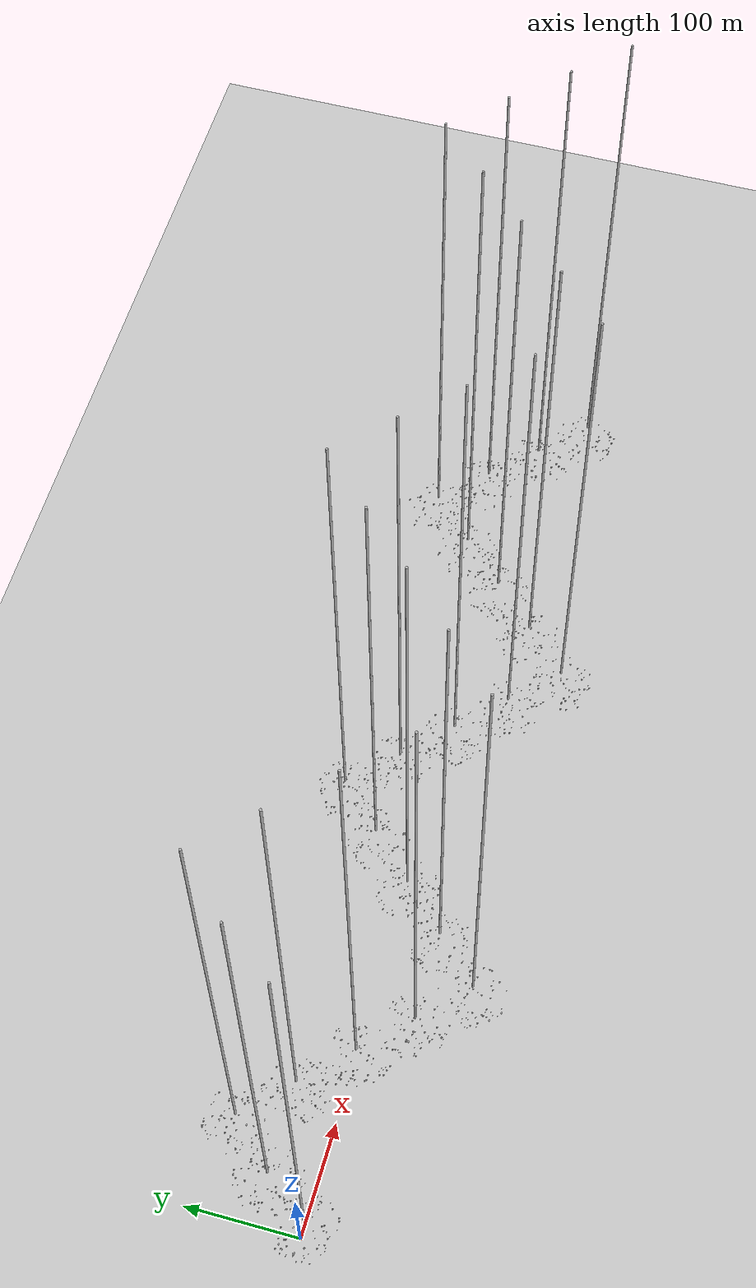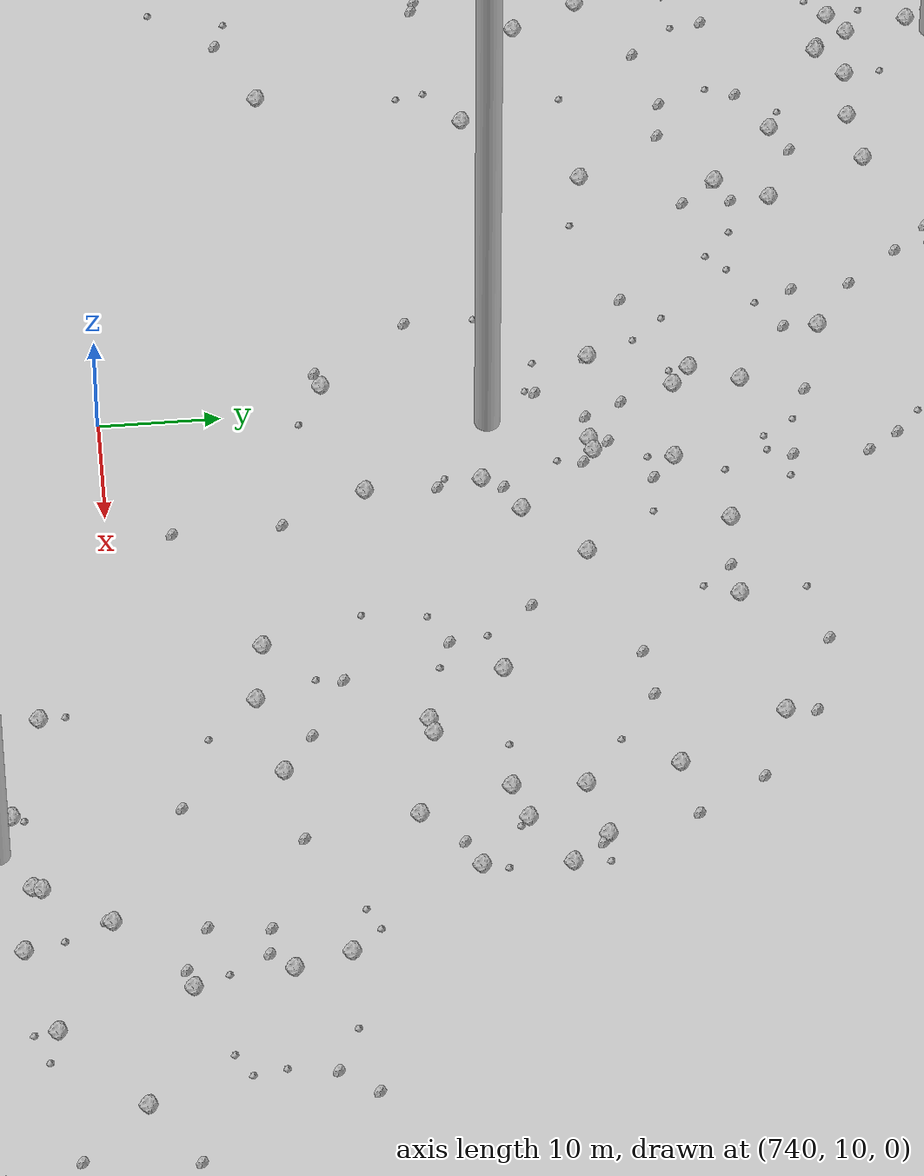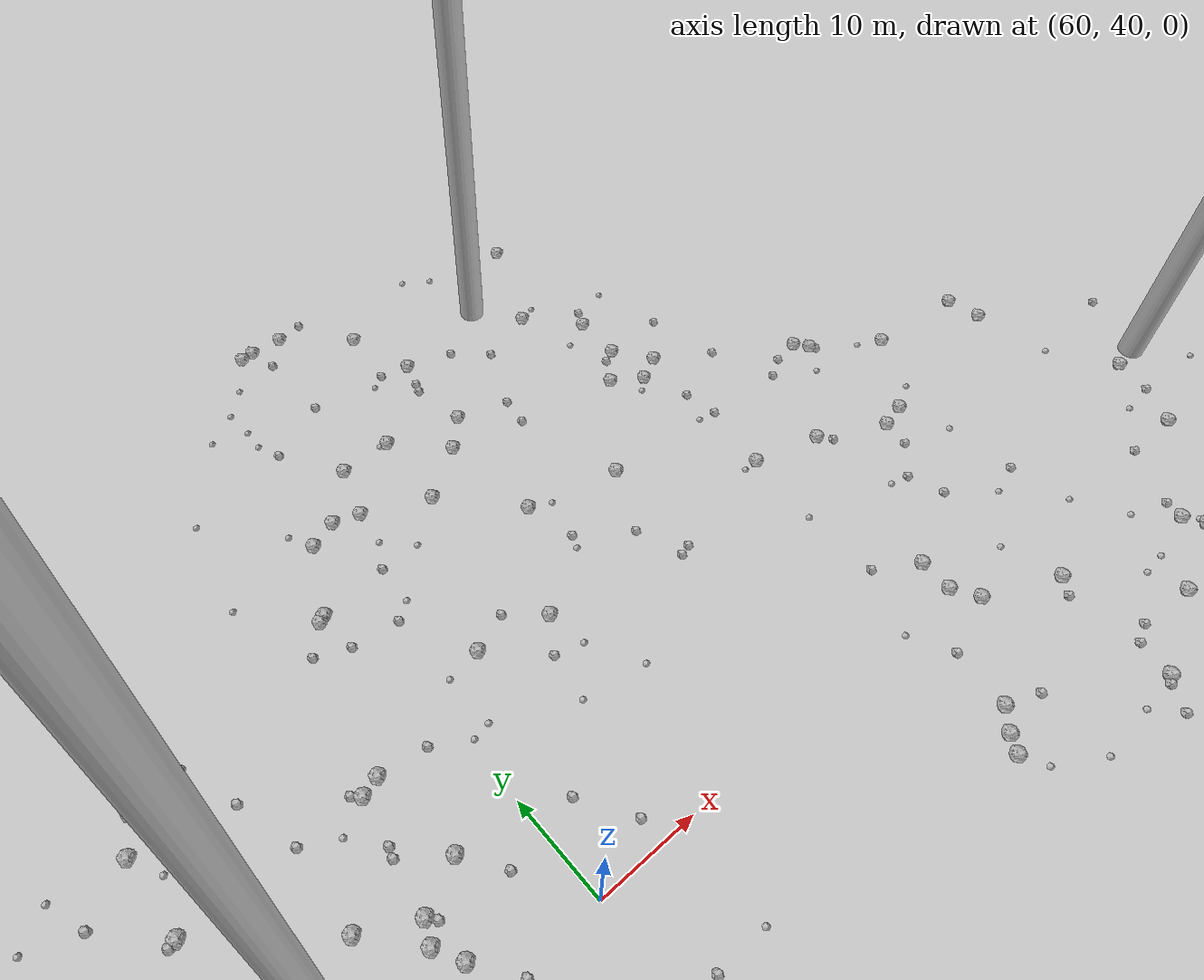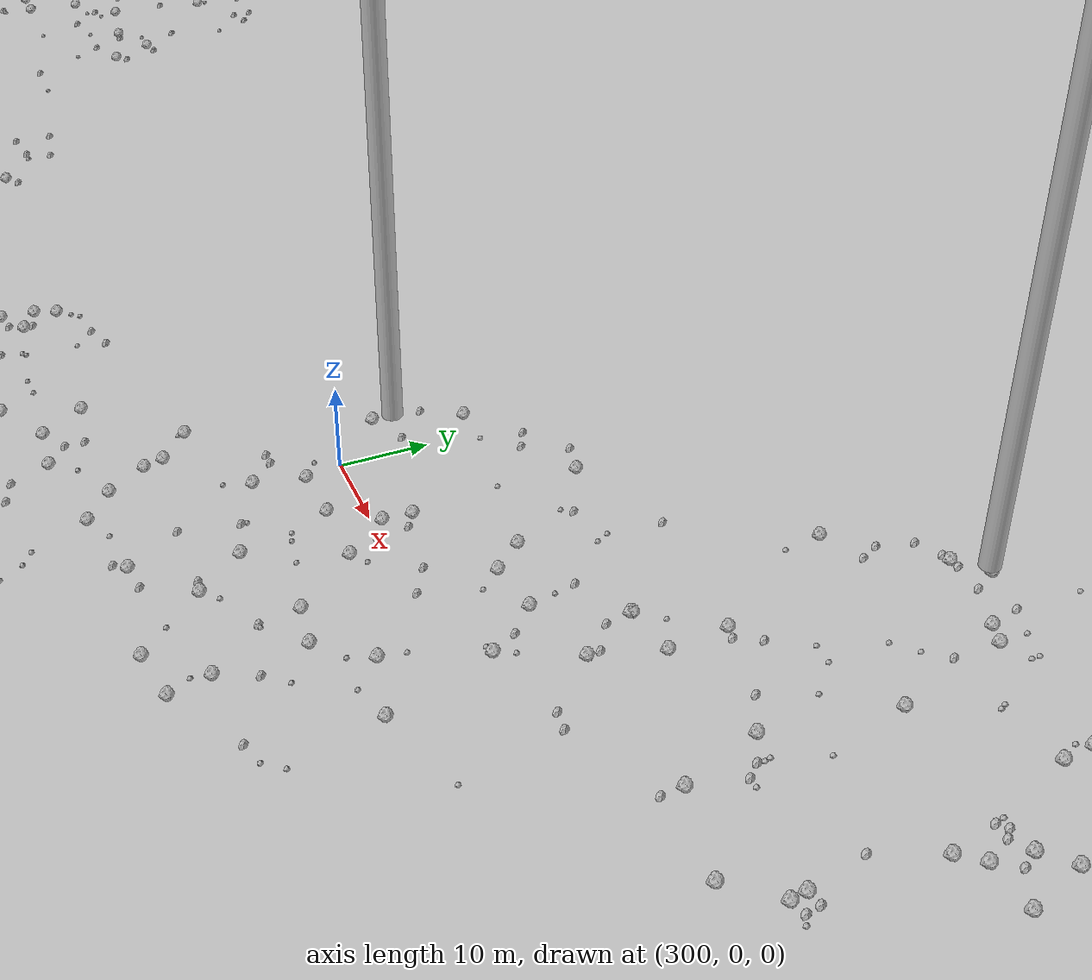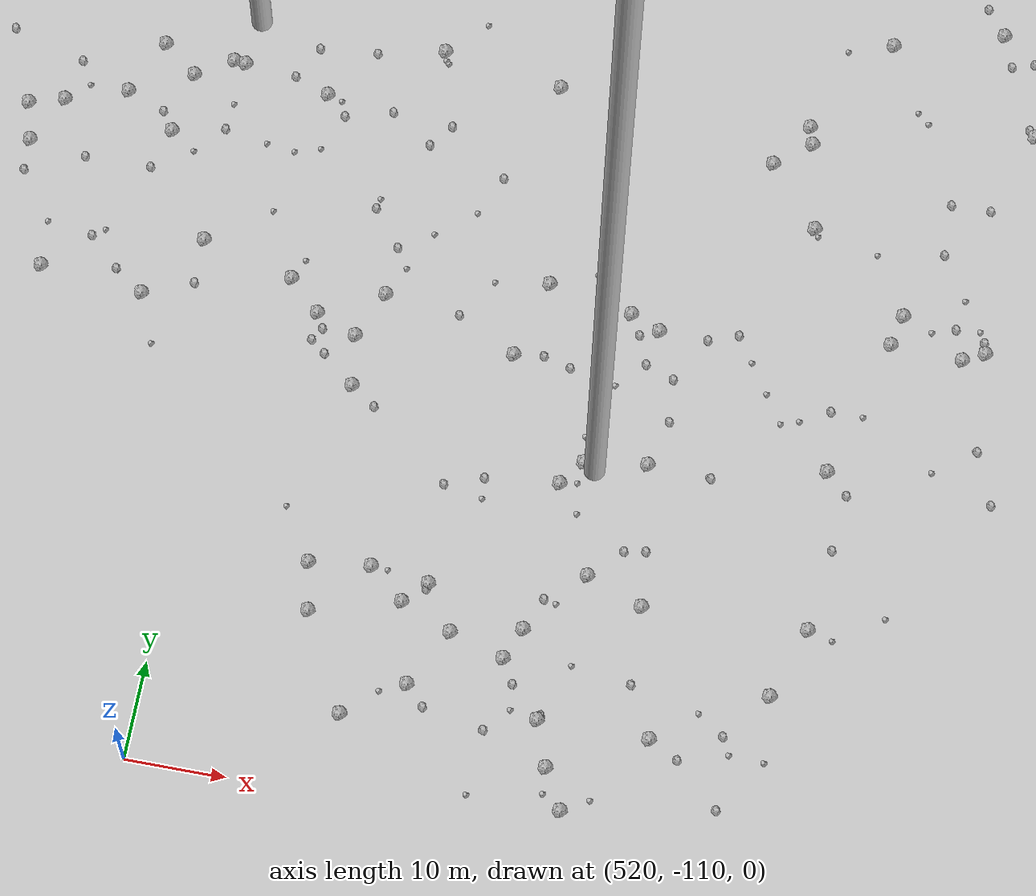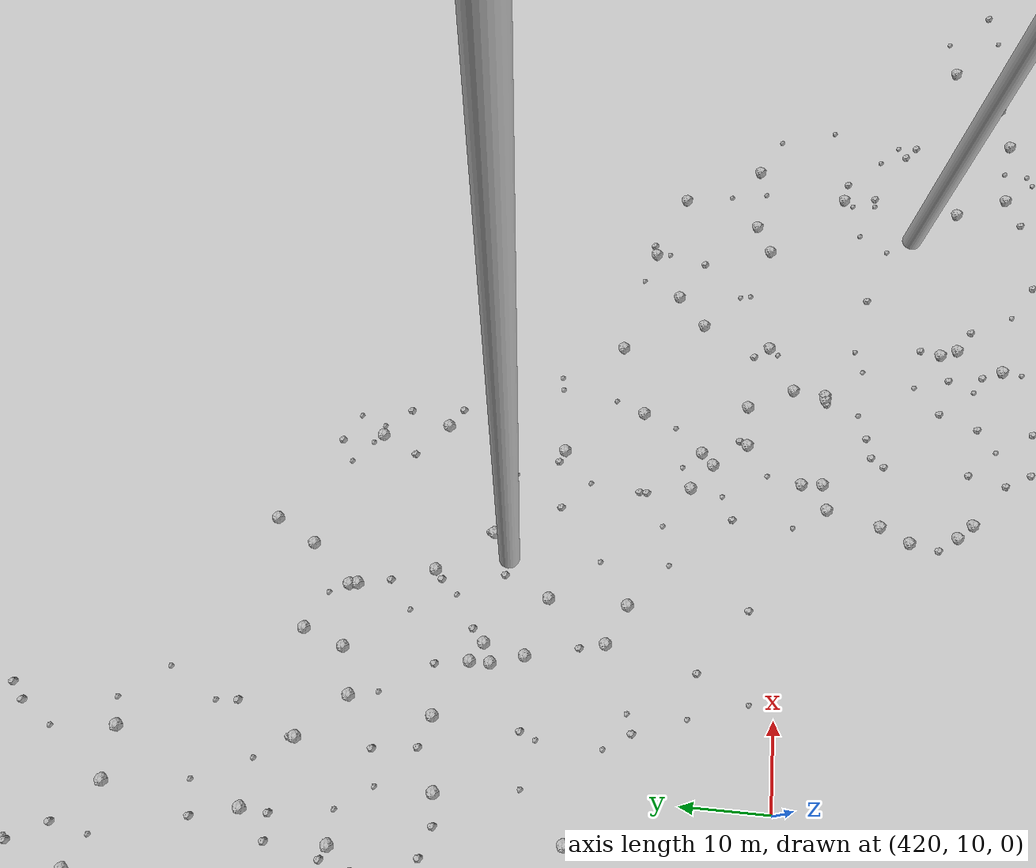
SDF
<sdf version="1.6">
 <world name="default">
  <include><uri>model://custom_ground</uri></include>
  <include><uri>model://sun</uri></include>
  <spherical_coordinates>
   <surface_model>EARTH_WGS84</surface_model>
   <latitude_deg>38.161479</latitude_deg>
   <longitude_deg>-122.454630</longitude_deg>
   <elevation>488.0</elevation>
   <heading_deg>90</heading_deg>
  </spherical_coordinates>
  <model name="rock1_0_0">
   <include><uri>model://rock1</uri><pose>0.5436891589005484 -19.710436343456372 0.5 0 0 0</pose></include>
  </model>
  <model name="rock1_0_1">
   <include><uri>model://rock1</uri><pose>5.9481144371615 -20.47905737511263 0.5 0 0 0</pose></include>
  </model>
  <model name="rock1_0_2">
   <include><uri>model://rock1</uri><pose>15.432644895932683 -14.83096497329507 0.5 0 0 0</pose></include>
  </model>
  <model name="rock1_0_3">
   <include><uri>model://rock1</uri><pose>-12.649335454473515 18.247128236137108 0.5 0 0 0</pose></include>
  </model>
  <model name="rock1_0_4">
   <include><uri>model://rock1</uri><pose>4.7766505931447405 18.629230287345763 0.5 0 0 0</pose></include>
  </model>
  <model name="rock1_0_5">
   <include><uri>model://rock1</uri><pose>-11.45997675912621 13.950966450524675 0.5 0 0 0</pose></include>
  </model>
  <model name="rock1_0_6">
   <include><uri>model://rock1</uri><pose>27.80985052088363 17.131061885188302 0.5 0 0 0</pose></include>
  </model>
  <model name="rock1_0_7">
   <include><uri>model://rock1</uri><pose>-8.62290181521637 16.32638972399357 0.5 0 0 0</pose></include>
  </model>
  <model name="rock1_0_8">
   <include><uri>model://rock1</uri><pose>-14.313720812322025 2.596264725335942 0.5 0 0 0</pose></include>
  </model>
  <model name="rock1_0_9">
   <include><uri>model://rock1</uri><pose>-6.22529883139606 -4.503889598051998 0.5 0 0 0</pose></include>
  </model>
  <model name="rock1_0_10">
   <include><uri>model://rock1</uri><pose>22.05983166761191 -25.614470193877658 0.5 0 0 0</pose></include>
  </model>
  <model name="rock1_0_11">
   <include><uri>model://rock1</uri><pose>14.446679946876571 -12.886116685419427 0.5 0 0 0</pose></include>
  </model>
  <model name="rock1_0_12">
   <include><uri>model://rock1</uri><pose>29.990400547254346 13.610071219841572 0.5 0 0 0</pose></include>
  </model>
  <model name="rock1_0_13">
   <include><uri>model://rock1</uri><pose>37.09907679336349 -2.4016692077286272 0.5 0 0 0</pose></include>
  </model>
  <model name="rock1_0_14">
   <include><uri>model://rock1</uri><pose>-0.4489782275225025 25.15402276094551 0.5 0 0 0</pose></include>
  </model>
  <model name="rock1_0_15">
   <include><uri>model://rock1</uri><pose>-3.976762199150375 -14.483736279361157 0.5 0 0 0</pose></include>
  </model>
  <model name="rock1_0_16">
   <include><uri>model://rock1</uri><pose>29.26333759204355 0.17785817182323171 0.5 0 0 0</pose></include>
  </model>
  <model name="rock1_0_17">
   <include><uri>model://rock1</uri><pose>24.996905013464477 21.760724918413857 0.5 0 0 0</pose></include>
  </model>
  <model name="rock1_0_18">
   <include><uri>model://rock1</uri><pose>30.197020932012435 -17.292593775076188 0.5 0 0 0</pose></include>
  </model>
  <model name="rock1_0_19">
   <include><uri>model://rock1</uri><pose>7.4349943004889205 8.923732833685428 0.5 0 0 0</pose></include>
  </model>
  <model name="rock1_0_20">
   <include><uri>model://rock1</uri><pose>24.76779827454395 -24.992839351688005 0.5 0 0 0</pose></include>
  </model>
  <model name="rock1_0_21">
   <include><uri>model://rock1</uri><pose>-4.015428753021155 13.08320571354001 0.5 0 0 0</pose></include>
  </model>
  <model name="rock1_0_22">
   <include><uri>model://rock1</uri><pose>-8.539670050877692 9.776573494086591 0.5 0 0 0</pose></include>
  </model>
  <model name="rock1_0_23">
   <include><uri>model://rock1</uri><pose>-12.292430489702568 2.216230114633106 0.5 0 0 0</pose></include>
  </model>
  <model name="rock1_0_24">
   <include><uri>model://rock1</uri><pose>13.441195437993976 26.213151501946278 0.5 0 0 0</pose></include>
  </model>
  <model name="rock1_0_25">
   <include><uri>model://rock1</uri><pose>9.178263115533632 6.953983589904851 0.5 0 0 0</pose></include>
  </model>
  <model name="rock1_0_26">
   <include><uri>model://rock1</uri><pose>-3.4977417187345026 12.22442860827595 0.5 0 0 0</pose></include>
  </model>
  <model name="rock2_0_0">
   <include><uri>model://rock2</uri><pose>-17.067872874895972 -12.093478937199453 0.3 0 0 0</pose></include>
  </model>
  <model name="rock2_0_1">
   <include><uri>model://rock2</uri><pose>-12.221839839201166 3.037260400345424 0.3 0 0 0</pose></include>
  </model>
  <model name="rock2_0_2">
   <include><uri>model://rock2</uri><pose>11.429680444975595 -15.36248811988543 0.3 0 0 0</pose></include>
  </model>
  <model name="rock2_0_3">
   <include><uri>model://rock2</uri><pose>29.587842951909963 4.9961832443208465 0.3 0 0 0</pose></include>
  </model>
  <model name="rock2_0_4">
   <include><uri>model://rock2</uri><pose>1.2283540100630965 16.530834887366495 0.3 0 0 0</pose></include>
  </model>
  <model name="rock2_0_5">
   <include><uri>model://rock2</uri><pose>11.201110361580021 -17.83792181532484 0.3 0 0 0</pose></include>
  </model>
  <model name="rock2_0_6">
   <include><uri>model://rock2</uri><pose>-18.350927363838302 -1.4310723819435403 0.3 0 0 0</pose></include>
  </model>
  <model name="rock2_0_7">
   <include><uri>model://rock2</uri><pose>-15.72434446690753 13.566229614591222 0.3 0 0 0</pose></include>
  </model>
  <model name="rock2_0_8">
   <include><uri>model://rock2</uri><pose>35.29225529605584 0.26603646452941376 0.3 0 0 0</pose></include>
  </model>
  <model name="rock2_0_9">
   <include><uri>model://rock2</uri><pose>19.949489925971143 -3.2325881748356053 0.3 0 0 0</pose></include>
  </model>
  <model name="rock2_0_10">
   <include><uri>model://rock2</uri><pose>20.443099651406186 18.312797939917388 0.3 0 0 0</pose></include>
  </model>
  <model name="rock2_0_11">
   <include><uri>model://rock2</uri><pose>22.727179587942523 0.71020809595651 0.3 0 0 0</pose></include>
  </model>
  <model name="rock2_0_12">
   <include><uri>model://rock2</uri><pose>34.148757270329455 -5.805367408889005 0.3 0 0 0</pose></include>
  </model>
  <model name="rock2_0_13">
   <include><uri>model://rock2</uri><pose>21.004424090755684 18.9019299895685 0.3 0 0 0</pose></include>
  </model>
  <model name="rock2_0_14">
   <include><uri>model://rock2</uri><pose>-9.753945009051282 -9.050095072073418 0.3 0 0 0</pose></include>
  </model>
  <model name="rock2_0_15">
   <include><uri>model://rock2</uri><pose>21.17870126048902 15.827224401449357 0.3 0 0 0</pose></include>
  </model>
  <model name="rock2_0_16">
   <include><uri>model://rock2</uri><pose>20.325881987126195 0.9892337154398732 0.3 0 0 0</pose></include>
  </model>
  <model name="rock2_0_17">
   <include><uri>model://rock2</uri><pose>-11.959821115137556 12.484914317507908 0.3 0 0 0</pose></include>
  </model>
  <model name="rock2_0_18">
   <include><uri>model://rock2</uri><pose>-15.335588733735243 8.058663935871081 0.3 0 0 0</pose></include>
  </model>
  <model name="rock2_0_19">
   <include><uri>model://rock2</uri><pose>23.816605624402293 -1.8312833187542097 0.3 0 0 0</pose></include>
  </model>
  <model name="rock2_0_20">
   <include><uri>model://rock2</uri><pose>26.977890824735923 19.980336879272564 0.3 0 0 0</pose></include>
  </model>
  <model name="rock2_0_21">
   <include><uri>model://rock2</uri><pose>-17.09273692142004 -5.897810283982661 0.3 0 0 0</pose></include>
  </model>
  <model name="rock2_0_22">
   <include><uri>model://rock2</uri><pose>30.95790330653054 -5.430497090081705 0.3 0 0 0</pose></include>
  </model>
  <model name="rock2_0_23">
   <include><uri>model://rock2</uri><pose>-16.53004821058895 8.437026331258771 0.3 0 0 0</pose></include>
  </model>
  <model name="rock2_0_24">
   <include><uri>model://rock2</uri><pose>33.187050619514906 -7.28292431695229 0.3 0 0 0</pose></include>
  </model>
  <model name="rock2_0_25">
   <include><uri>model://rock2</uri><pose>-4.350299544477661 17.924787294820966 0.3 0 0 0</pose></include>
  </model>
  <model name="rock2_0_26">
   <include><uri>model://rock2</uri><pose>10.630970598116104 -18.08390676121338 0.3 0 0 0</pose></include>
  </model>
  <model name="rock3_0_0">
   <include><uri>model://rock3</uri><pose>-1.81205648999374 -20.967254577260675 0.2 0 0 0</pose></include>
  </model>
  <model name="rock3_0_1">
   <include><uri>model://rock3</uri><pose>24.294358376243544 11.526904978821626 0.2 0 0 0</pose></include>
  </model>
  <model name="rock3_0_2">
   <include><uri>model://rock3</uri><pose>8.148145809220175 -21.52344293271583 0.2 0 0 0</pose></include>
  </model>
  <model name="rock3_0_3">
   <include><uri>model://rock3</uri><pose>38.15179034865989 -5.638713922640484 0.2 0 0 0</pose></include>
  </model>
  <model name="rock3_0_4">
   <include><uri>model://rock3</uri><pose>4.007075606035034 -10.532256558939292 0.2 0 0 0</pose></include>
  </model>
  <model name="rock3_0_5">
   <include><uri>model://rock3</uri><pose>14.198202405862126 25.419148451766908 0.2 0 0 0</pose></include>
  </model>
  <model name="rock3_0_6">
   <include><uri>model://rock3</uri><pose>34.97044580056028 -14.524111346203156 0.2 0 0 0</pose></include>
  </model>
  <model name="rock3_0_7">
   <include><uri>model://rock3</uri><pose>-4.11979583610556 -21.180463702387126 0.2 0 0 0</pose></include>
  </model>
  <model name="rock3_0_8">
   <include><uri>model://rock3</uri><pose>-5.316920276711594 3.5772868221576104 0.2 0 0 0</pose></include>
  </model>
  <model name="rock3_0_9">
   <include><uri>model://rock3</uri><pose>26.65830170070833 -6.153220534333165 0.2 0 0 0</pose></include>
  </model>
  <model name="rock3_0_10">
   <include><uri>model://rock3</uri><pose>30.61472194336374 -17.25229347238168 0.2 0 0 0</pose></include>
  </model>
  <model name="rock3_0_11">
   <include><uri>model://rock3</uri><pose>21.580546665722814 11.21737873855902 0.2 0 0 0</pose></include>
  </model>
  <model name="rock3_0_12">
   <include><uri>model://rock3</uri><pose>-7.822851166286968 -18.91984280660341 0.2 0 0 0</pose></include>
  </model>
  <model name="rock3_0_13">
   <include><uri>model://rock3</uri><pose>21.28248197260794 -24.702887649625772 0.2 0 0 0</pose></include>
  </model>
  <model name="rock3_0_14">
   <include><uri>model://rock3</uri><pose>-12.056861513498562 -5.745120843166205 0.2 0 0 0</pose></include>
  </model>
  <model name="rock3_0_15">
   <include><uri>model://rock3</uri><pose>1.9327197016192237 18.538872113810577 0.2 0 0 0</pose></include>
  </model>
  <model name="rock3_0_16">
   <include><uri>model://rock3</uri><pose>4.574657766552942 -27.344375731403844 0.2 0 0 0</pose></include>
  </model>
  <model name="rock3_0_17">
   <include><uri>model://rock3</uri><pose>-15.882748824973916 6.817106578195272 0.2 0 0 0</pose></include>
  </model>
  <model name="rock3_0_18">
   <include><uri>model://rock3</uri><pose>13.552580879661178 24.489599938564695 0.2 0 0 0</pose></include>
  </model>
  <model name="rock3_0_19">
   <include><uri>model://rock3</uri><pose>9.464367075092063 -7.4203386979854 0.2 0 0 0</pose></include>
  </model>
  <model name="rock3_0_20">
   <include><uri>model://rock3</uri><pose>14.477046278118394 5.627255053529986 0.2 0 0 0</pose></include>
  </model>
  <model name="rock3_0_21">
   <include><uri>model://rock3</uri><pose>16.648782193569033 6.659672984724018 0.2 0 0 0</pose></include>
  </model>
  <model name="rock3_0_22">
   <include><uri>model://rock3</uri><pose>-13.888223071268424 -6.5598093236294766 0.2 0 0 0</pose></include>
  </model>
  <model name="rock3_0_23">
   <include><uri>model://rock3</uri><pose>1.4175736310347453 6.015509907721764 0.2 0 0 0</pose></include>
  </model>
  <model name="rock3_0_24">
   <include><uri>model://rock3</uri><pose>15.00653718108699 -25.831771619110253 0.2 0 0 0</pose></include>
  </model>
  <model name="rock3_0_25">
   <include><uri>model://rock3</uri><pose>1.7507869226507111 -16.972719560095285 0.2 0 0 0</pose></include>
  </model>
  <model name="rock3_0_26">
   <include><uri>model://rock3</uri><pose>-0.5810729965312937 -15.018845623757828 0.2 0 0 0</pose></include>
  </model>
  <model name="rock1_1_0">
   <include><uri>model://rock1</uri><pose>35.663468055083555 32.640918392487755 0.5 0 0 0</pose></include>
  </model>
  <model name="rock1_1_1">
   <include><uri>model://rock1</uri><pose>17.047101697174018 29.870412738290003 0.5 0 0 0</pose></include>
  </model>
  <model name="rock1_1_2">
   <include><uri>model://rock1</uri><pose>36.60238505689297 14.847560513471588 0.5 0 0 0</pose></include>
  </model>
  <model name="rock1_1_3">
   <include><uri>model://rock1</uri><pose>28.755521340649103 27.04263338431591 0.5 0 0 0</pose></include>
  </model>
  <model name="rock1_1_4">
   <include><uri>model://rock1</uri><pose>50.84056092684039 24.477121421675278 0.5 0 0 0</pose></include>
  </model>
  <model name="rock1_1_5">
   <include><uri>model://rock1</uri><pose>19.678457383170045 42.354311908262794 0.5 0 0 0</pose></include>
  </model>
  <model name="rock1_1_6">
   <include><uri>model://rock1</uri><pose>49.509178249313074 43.2005348974448 0.5 0 0 0</pose></include>
  </model>
  <model name="rock1_1_7">
   <include><uri>model://rock1</uri><pose>34.04447596766532 58.485030262238055 0.5 0 0 0</pose></include>
  </model>
  <model name="rock1_1_8">
   <include><uri>model://rock1</uri><pose>49.032866310676596 47.65996477301706 0.5 0 0 0</pose></include>
  </model>
  <model name="rock1_1_9">
   <include><uri>model://rock1</uri><pose>35.693222869975386 69.3892604042315 0.5 0 0 0</pose></include>
  </model>
  <model name="rock1_1_10">
   <include><uri>model://rock1</uri><pose>17.008909745709808 44.941119843696185 0.5 0 0 0</pose></include>
  </model>
  <model name="rock1_1_11">
   <include><uri>model://rock1</uri><pose>31.47215285244812 30.927455304930657 0.5 0 0 0</pose></include>
  </model>
  <model name="rock1_1_12">
   <include><uri>model://rock1</uri><pose>27.418989657708863 47.69815003970842 0.5 0 0 0</pose></include>
  </model>
  <model name="rock1_1_13">
   <include><uri>model://rock1</uri><pose>48.84814038671507 21.61371732301067 0.5 0 0 0</pose></include>
  </model>
  <model name="rock1_1_14">
   <include><uri>model://rock1</uri><pose>40.14861499763535 69.84298991072941 0.5 0 0 0</pose></include>
  </model>
  <model name="rock1_1_15">
   <include><uri>model://rock1</uri><pose>20.86468379037783 57.505579184855584 0.5 0 0 0</pose></include>
  </model>
  <model name="rock1_1_16">
   <include><uri>model://rock1</uri><pose>53.583799989580996 49.8654577899057 0.5 0 0 0</pose></include>
  </model>
  <model name="rock1_1_17">
   <include><uri>model://rock1</uri><pose>27.601563775876976 22.839869549027092 0.5 0 0 0</pose></include>
  </model>
  <model name="rock1_1_18">
   <include><uri>model://rock1</uri><pose>58.915237411383075 24.286704427361954 0.5 0 0 0</pose></include>
  </model>
  <model name="rock1_1_19">
   <include><uri>model://rock1</uri><pose>12.093980743279925 40.77436948149971 0.5 0 0 0</pose></include>
  </model>
  <model name="rock1_1_20">
   <include><uri>model://rock1</uri><pose>20.195810597392786 39.72622201695046 0.5 0 0 0</pose></include>
  </model>
  <model name="rock1_1_21">
   <include><uri>model://rock1</uri><pose>33.94455974200255 66.28258576384795 0.5 0 0 0</pose></include>
  </model>
  <model name="rock1_1_22">
   <include><uri>model://rock1</uri><pose>48.1379945693072 45.682803357344625 0.5 0 0 0</pose></include>
  </model>
  <model name="rock1_1_23">
   <include><uri>model://rock1</uri><pose>17.381759890229493 48.373992539414054 0.5 0 0 0</pose></include>
  </model>
  <model name="rock1_1_24">
   <include><uri>model://rock1</uri><pose>50.67934650677888 58.36422446788012 0.5 0 0 0</pose></include>
  </model>
  <model name="rock1_1_25">
   <include><uri>model://rock1</uri><pose>52.54345993078916 58.97848529056101 0.5 0 0 0</pose></include>
  </model>
  <model name="rock1_1_26">
   <include><uri>model://rock1</uri><pose>44.15409780677631 50.21227277498687 0.5 0 0 0</pose></include>
  </model>
  <model name="rock2_1_0">
   <include><uri>model://rock2</uri><pose>44.40746168720538 58.474576021617516 0.3 0 0 0</pose></include>
  </model>
  <model name="rock2_1_1">
   <include><uri>model://rock2</uri><pose>23.925345879831447 45.354324498864194 0.3 0 0 0</pose></include>
  </model>
  <model name="rock2_1_2">
   <include><uri>model://rock2</uri><pose>29.033865980600837 63.48818506140026 0.3 0 0 0</pose></include>
  </model>
  <model name="rock2_1_3">
   <include><uri>model://rock2</uri><pose>49.69345396916179 46.895607384534365 0.3 0 0 0</pose></include>
  </model>
  <model name="rock2_1_4">
   <include><uri>model://rock2</uri><pose>40.368940454359276 15.391821340827896 0.3 0 0 0</pose></include>
  </model>
  <model name="rock2_1_5">
   <include><uri>model://rock2</uri><pose>32.32204115218447 38.4742333246987 0.3 0 0 0</pose></include>
  </model>
  <model name="rock2_1_6">
   <include><uri>model://rock2</uri><pose>41.65767228360706 12.203340886074399 0.3 0 0 0</pose></include>
  </model>
  <model name="rock2_1_7">
   <include><uri>model://rock2</uri><pose>54.536167687694935 35.189958320764035 0.3 0 0 0</pose></include>
  </model>
  <model name="rock2_1_8">
   <include><uri>model://rock2</uri><pose>57.12928278764083 58.417053949883076 0.3 0 0 0</pose></include>
  </model>
  <model name="rock2_1_9">
   <include><uri>model://rock2</uri><pose>50.36878487839329 20.677844974918976 0.3 0 0 0</pose></include>
  </model>
  <model name="rock2_1_10">
   <include><uri>model://rock2</uri><pose>31.27706346071188 34.778555370412704 0.3 0 0 0</pose></include>
  </model>
  <model name="rock2_1_11">
   <include><uri>model://rock2</uri><pose>49.89633098885455 59.109836529889115 0.3 0 0 0</pose></include>
  </model>
  <model name="rock2_1_12">
   <include><uri>model://rock2</uri><pose>29.539717669358186 23.617093055622334 0.3 0 0 0</pose></include>
  </model>
  <model name="rock2_1_13">
   <include><uri>model://rock2</uri><pose>54.984516131881854 14.182839072639648 0.3 0 0 0</pose></include>
  </model>
  <model name="rock2_1_14">
   <include><uri>model://rock2</uri><pose>49.98676962647884 53.8197158720443 0.3 0 0 0</pose></include>
  </model>
  <model name="rock2_1_15">
   <include><uri>model://rock2</uri><pose>42.566228111563234 64.52180564750729 0.3 0 0 0</pose></include>
  </model>
  <model name="rock2_1_16">
   <include><uri>model://rock2</uri><pose>66.60690298680805 42.510170589941175 0.3 0 0 0</pose></include>
  </model>
  <model name="rock2_1_17">
   <include><uri>model://rock2</uri><pose>56.12444373736584 46.153485651616364 0.3 0 0 0</pose></include>
  </model>
  <model name="rock2_1_18">
   <include><uri>model://rock2</uri><pose>37.22308514155998 69.6436638743196 0.3 0 0 0</pose></include>
  </model>
  <model name="rock2_1_19">
   <include><uri>model://rock2</uri><pose>49.680357574520464 52.84574657605128 0.3 0 0 0</pose></include>
  </model>
  <model name="rock2_1_20">
   <include><uri>model://rock2</uri><pose>19.471769152202896 59.150495166930696 0.3 0 0 0</pose></include>
  </model>
  <model name="rock2_1_21">
   <include><uri>model://rock2</uri><pose>63.029032880163115 30.590233862847466 0.3 0 0 0</pose></include>
  </model>
  <model name="rock2_1_22">
   <include><uri>model://rock2</uri><pose>29.5145042456122 27.77197321360983 0.3 0 0 0</pose></include>
  </model>
  <model name="rock2_1_23">
   <include><uri>model://rock2</uri><pose>63.56904054599607 47.382232875356735 0.3 0 0 0</pose></include>
  </model>
  <model name="rock2_1_24">
   <include><uri>model://rock2</uri><pose>33.213182838169516 58.347708104127925 0.3 0 0 0</pose></include>
  </model>
  <model name="rock2_1_25">
   <include><uri>model://rock2</uri><pose>53.52278394121292 25.389170156272836 0.3 0 0 0</pose></include>
  </model>
  <model name="rock2_1_26">
   <include><uri>model://rock2</uri><pose>52.23712817046862 39.449031842538616 0.3 0 0 0</pose></include>
  </model>
  <model name="rock3_1_0">
   <include><uri>model://rock3</uri><pose>35.42738904677622 63.37029750752649 0.2 0 0 0</pose></include>
  </model>
  <model name="rock3_1_1">
   <include><uri>model://rock3</uri><pose>26.053473024562436 32.03262439207085 0.2 0 0 0</pose></include>
  </model>
  <model name="rock3_1_2">
   <include><uri>model://rock3</uri><pose>13.855304612863062 54.108113020746146 0.2 0 0 0</pose></include>
  </model>
  <model name="rock3_1_3">
   <include><uri>model://rock3</uri><pose>15.473966928649832 40.482208363677906 0.2 0 0 0</pose></include>
  </model>
  <model name="rock3_1_4">
   <include><uri>model://rock3</uri><pose>36.159308905163385 17.750216661969272 0.2 0 0 0</pose></include>
  </model>
  <model name="rock3_1_5">
   <include><uri>model://rock3</uri><pose>19.540888980283256 19.40757801472258 0.2 0 0 0</pose></include>
  </model>
  <model name="rock3_1_6">
   <include><uri>model://rock3</uri><pose>27.573500644914407 67.26686801955228 0.2 0 0 0</pose></include>
  </model>
  <model name="rock3_1_7">
   <include><uri>model://rock3</uri><pose>26.992833304045647 47.450439583098515 0.2 0 0 0</pose></include>
  </model>
  <model name="rock3_1_8">
   <include><uri>model://rock3</uri><pose>52.120358148350064 35.294505308286276 0.2 0 0 0</pose></include>
  </model>
  <model name="rock3_1_9">
   <include><uri>model://rock3</uri><pose>17.508905582692336 44.811096474043055 0.2 0 0 0</pose></include>
  </model>
  <model name="rock3_1_10">
   <include><uri>model://rock3</uri><pose>24.41761448481301 65.12305001256625 0.2 0 0 0</pose></include>
  </model>
  <model name="rock3_1_11">
   <include><uri>model://rock3</uri><pose>47.61617318471914 14.552583298664254 0.2 0 0 0</pose></include>
  </model>
  <model name="rock3_1_12">
   <include><uri>model://rock3</uri><pose>19.529269053547686 45.471266980981035 0.2 0 0 0</pose></include>
  </model>
  <model name="rock3_1_13">
   <include><uri>model://rock3</uri><pose>37.566519732776584 63.44641102775573 0.2 0 0 0</pose></include>
  </model>
  <model name="rock3_1_14">
   <include><uri>model://rock3</uri><pose>44.77674097297674 10.393489225827306 0.2 0 0 0</pose></include>
  </model>
  <model name="rock3_1_15">
   <include><uri>model://rock3</uri><pose>30.75472811816981 24.6873443155656 0.2 0 0 0</pose></include>
  </model>
  <model name="rock3_1_16">
   <include><uri>model://rock3</uri><pose>25.183227381970426 26.41368758125269 0.2 0 0 0</pose></include>
  </model>
  <model name="rock3_1_17">
   <include><uri>model://rock3</uri><pose>47.59389979291314 56.69841201101397 0.2 0 0 0</pose></include>
  </model>
  <model name="rock3_1_18">
   <include><uri>model://rock3</uri><pose>32.94102087775724 48.63741070757922 0.2 0 0 0</pose></include>
  </model>
  <model name="rock3_1_19">
   <include><uri>model://rock3</uri><pose>62.30101582650904 56.70710714831881 0.2 0 0 0</pose></include>
  </model>
  <model name="rock3_1_20">
   <include><uri>model://rock3</uri><pose>32.54287010127429 46.3029724494192 0.2 0 0 0</pose></include>
  </model>
  <model name="rock3_1_21">
   <include><uri>model://rock3</uri><pose>60.51273247073374 56.383528139883026 0.2 0 0 0</pose></include>
  </model>
  <model name="rock3_1_22">
   <include><uri>model://rock3</uri><pose>23.09169726382662 50.32315476981192 0.2 0 0 0</pose></include>
  </model>
  <model name="rock3_1_23">
   <include><uri>model://rock3</uri><pose>48.591507773566 22.772661278388373 0.2 0 0 0</pose></include>
  </model>
  <model name="rock3_1_24">
   <include><uri>model://rock3</uri><pose>45.350599701972534 10.854499138888468 0.2 0 0 0</pose></include>
  </model>
  <model name="rock3_1_25">
   <include><uri>model://rock3</uri><pose>49.37599613086856 38.14188405564792 0.2 0 0 0</pose></include>
  </model>
  <model name="rock3_1_26">
   <include><uri>model://rock3</uri><pose>68.19041093315181 30.47257585017533 0.2 0 0 0</pose></include>
  </model>
  <model name="rock1_2_0">
   <include><uri>model://rock1</uri><pose>88.55083004626248 69.24300075353139 0.5 0 0 0</pose></include>
  </model>
  <model name="rock1_2_1">
   <include><uri>model://rock1</uri><pose>80.6993289308457 85.02971800637141 0.5 0 0 0</pose></include>
  </model>
  <model name="rock1_2_2">
   <include><uri>model://rock1</uri><pose>67.76652604650435 106.72733126922337 0.5 0 0 0</pose></include>
  </model>
  <model name="rock1_2_3">
   <include><uri>model://rock1</uri><pose>99.56929216982078 102.12924237968278 0.5 0 0 0</pose></include>
  </model>
  <model name="rock1_2_4">
   <include><uri>model://rock1</uri><pose>79.02321859718344 71.50290299018592 0.5 0 0 0</pose></include>
  </model>
  <model name="rock1_2_5">
   <include><uri>model://rock1</uri><pose>65.75268256021164 62.54708817494444 0.5 0 0 0</pose></include>
  </model>
  <model name="rock1_2_6">
   <include><uri>model://rock1</uri><pose>66.1188917661862 81.51886796463266 0.5 0 0 0</pose></include>
  </model>
  <model name="rock1_2_7">
   <include><uri>model://rock1</uri><pose>100.14873845884318 60.96472314792849 0.5 0 0 0</pose></include>
  </model>
  <model name="rock1_2_8">
   <include><uri>model://rock1</uri><pose>72.61216486963835 78.569232751325 0.5 0 0 0</pose></include>
  </model>
  <model name="rock1_2_9">
   <include><uri>model://rock1</uri><pose>99.23929640016604 81.54212177957336 0.5 0 0 0</pose></include>
  </model>
  <model name="rock1_2_10">
   <include><uri>model://rock1</uri><pose>72.44326872202336 106.72687729215433 0.5 0 0 0</pose></include>
  </model>
  <model name="rock1_2_11">
   <include><uri>model://rock1</uri><pose>60.645704757779725 81.30954870907163 0.5 0 0 0</pose></include>
  </model>
  <model name="rock1_2_12">
   <include><uri>model://rock1</uri><pose>72.98623718541054 61.19532888053919 0.5 0 0 0</pose></include>
  </model>
  <model name="rock1_2_13">
   <include><uri>model://rock1</uri><pose>96.22609456644508 78.47244429442921 0.5 0 0 0</pose></include>
  </model>
  <model name="rock1_2_14">
   <include><uri>model://rock1</uri><pose>56.703744612265886 74.0279989449387 0.5 0 0 0</pose></include>
  </model>
  <model name="rock1_2_15">
   <include><uri>model://rock1</uri><pose>78.687477372961 101.3634703072284 0.5 0 0 0</pose></include>
  </model>
  <model name="rock1_2_16">
   <include><uri>model://rock1</uri><pose>67.77251585179476 86.85426257568886 0.5 0 0 0</pose></include>
  </model>
  <model name="rock1_2_17">
   <include><uri>model://rock1</uri><pose>99.28958551067308 76.47433922745847 0.5 0 0 0</pose></include>
  </model>
  <model name="rock1_2_18">
   <include><uri>model://rock1</uri><pose>73.11568961755987 86.99921465271603 0.5 0 0 0</pose></include>
  </model>
  <model name="rock1_2_19">
   <include><uri>model://rock1</uri><pose>99.53582706189094 86.69014314822107 0.5 0 0 0</pose></include>
  </model>
  <model name="rock1_2_20">
   <include><uri>model://rock1</uri><pose>80.89373562509589 94.25531073113333 0.5 0 0 0</pose></include>
  </model>
  <model name="rock1_2_21">
   <include><uri>model://rock1</uri><pose>63.485409968495404 82.36966680763399 0.5 0 0 0</pose></include>
  </model>
  <model name="rock1_2_22">
   <include><uri>model://rock1</uri><pose>57.35791890277139 74.38187650623837 0.5 0 0 0</pose></include>
  </model>
  <model name="rock1_2_23">
   <include><uri>model://rock1</uri><pose>101.99653360952048 77.81464064044495 0.5 0 0 0</pose></include>
  </model>
  <model name="rock1_2_24">
   <include><uri>model://rock1</uri><pose>77.88227703810932 82.17338032606231 0.5 0 0 0</pose></include>
  </model>
  <model name="rock1_2_25">
   <include><uri>model://rock1</uri><pose>94.96580106936041 91.77708229066936 0.5 0 0 0</pose></include>
  </model>
  <model name="rock1_2_26">
   <include><uri>model://rock1</uri><pose>69.10886767295399 106.87544163017927 0.5 0 0 0</pose></include>
  </model>
  <model name="rock2_2_0">
   <include><uri>model://rock2</uri><pose>101.0453842499988 71.81701970021973 0.3 0 0 0</pose></include>
  </model>
  <model name="rock2_2_1">
   <include><uri>model://rock2</uri><pose>101.54560735798364 68.2182718139213 0.3 0 0 0</pose></include>
  </model>
  <model name="rock2_2_2">
   <include><uri>model://rock2</uri><pose>77.8979539770683 95.07261224183908 0.3 0 0 0</pose></include>
  </model>
  <model name="rock2_2_3">
   <include><uri>model://rock2</uri><pose>88.88924089230865 89.93455051025413 0.3 0 0 0</pose></include>
  </model>
  <model name="rock2_2_4">
   <include><uri>model://rock2</uri><pose>75.15160305587378 107.29209044586375 0.3 0 0 0</pose></include>
  </model>
  <model name="rock2_2_5">
   <include><uri>model://rock2</uri><pose>86.62335732284964 57.996411175246216 0.3 0 0 0</pose></include>
  </model>
  <model name="rock2_2_6">
   <include><uri>model://rock2</uri><pose>100.35133649212021 88.45385622818588 0.3 0 0 0</pose></include>
  </model>
  <model name="rock2_2_7">
   <include><uri>model://rock2</uri><pose>63.834592744855776 92.93174208150012 0.3 0 0 0</pose></include>
  </model>
  <model name="rock2_2_8">
   <include><uri>model://rock2</uri><pose>85.14773372456426 62.78056023574948 0.3 0 0 0</pose></include>
  </model>
  <model name="rock2_2_9">
   <include><uri>model://rock2</uri><pose>105.86344243045228 81.88389914518962 0.3 0 0 0</pose></include>
  </model>
  <model name="rock2_2_10">
   <include><uri>model://rock2</uri><pose>62.169741986133346 69.63198326204812 0.3 0 0 0</pose></include>
  </model>
  <model name="rock2_2_11">
   <include><uri>model://rock2</uri><pose>64.15598466905006 75.0932984503832 0.3 0 0 0</pose></include>
  </model>
  <model name="rock2_2_12">
   <include><uri>model://rock2</uri><pose>85.92966060732596 83.44403412535422 0.3 0 0 0</pose></include>
  </model>
  <model name="rock2_2_13">
   <include><uri>model://rock2</uri><pose>80.13263692751289 66.36581822157854 0.3 0 0 0</pose></include>
  </model>
  <model name="rock2_2_14">
   <include><uri>model://rock2</uri><pose>70.09020303906354 95.9031069628947 0.3 0 0 0</pose></include>
  </model>
  <model name="rock2_2_15">
   <include><uri>model://rock2</uri><pose>97.81523460589386 80.94824794680854 0.3 0 0 0</pose></include>
  </model>
  <model name="rock2_2_16">
   <include><uri>model://rock2</uri><pose>69.7788869420051 104.00629910923665 0.3 0 0 0</pose></include>
  </model>
  <model name="rock2_2_17">
   <include><uri>model://rock2</uri><pose>54.25213736994816 71.56611837359581 0.3 0 0 0</pose></include>
  </model>
  <model name="rock2_2_18">
   <include><uri>model://rock2</uri><pose>70.64370558375164 57.911911664900394 0.3 0 0 0</pose></include>
  </model>
  <model name="rock2_2_19">
   <include><uri>model://rock2</uri><pose>87.79987433800471 58.34189895370855 0.3 0 0 0</pose></include>
  </model>
  <model name="rock2_2_20">
   <include><uri>model://rock2</uri><pose>80.07068393079034 91.71170418967714 0.3 0 0 0</pose></include>
  </model>
  <model name="rock2_2_21">
   <include><uri>model://rock2</uri><pose>69.59502262067248 64.10113326378392 0.3 0 0 0</pose></include>
  </model>
  <model name="rock2_2_22">
   <include><uri>model://rock2</uri><pose>79.72297400259431 90.69225159868013 0.3 0 0 0</pose></include>
  </model>
  <model name="rock2_2_23">
   <include><uri>model://rock2</uri><pose>85.57434273874996 92.84645848822376 0.3 0 0 0</pose></include>
  </model>
  <model name="rock2_2_24">
   <include><uri>model://rock2</uri><pose>107.51680687083022 74.37489756884871 0.3 0 0 0</pose></include>
  </model>
  <model name="rock2_2_25">
   <include><uri>model://rock2</uri><pose>57.468465178540924 70.19377911809833 0.3 0 0 0</pose></include>
  </model>
  <model name="rock2_2_26">
   <include><uri>model://rock2</uri><pose>85.45657581666518 80.4225408233294 0.3 0 0 0</pose></include>
  </model>
  <model name="rock3_2_0">
   <include><uri>model://rock3</uri><pose>96.73649305035806 92.38903912215355 0.2 0 0 0</pose></include>
  </model>
  <model name="rock3_2_1">
   <include><uri>model://rock3</uri><pose>104.13012621279367 89.12771966769817 0.2 0 0 0</pose></include>
  </model>
  <model name="rock3_2_2">
   <include><uri>model://rock3</uri><pose>90.70608797657587 103.65429047754074 0.2 0 0 0</pose></include>
  </model>
  <model name="rock3_2_3">
   <include><uri>model://rock3</uri><pose>99.72227568334642 68.52814375227865 0.2 0 0 0</pose></include>
  </model>
  <model name="rock3_2_4">
   <include><uri>model://rock3</uri><pose>62.72222412761028 100.63810282685226 0.2 0 0 0</pose></include>
  </model>
  <model name="rock3_2_5">
   <include><uri>model://rock3</uri><pose>68.24650258194525 75.1188670796422 0.2 0 0 0</pose></include>
  </model>
  <model name="rock3_2_6">
   <include><uri>model://rock3</uri><pose>69.7967999623772 53.10839339849614 0.2 0 0 0</pose></include>
  </model>
  <model name="rock3_2_7">
   <include><uri>model://rock3</uri><pose>79.59821268945134 65.03178324756007 0.2 0 0 0</pose></include>
  </model>
  <model name="rock3_2_8">
   <include><uri>model://rock3</uri><pose>76.45565761797307 94.15092697256623 0.2 0 0 0</pose></include>
  </model>
  <model name="rock3_2_9">
   <include><uri>model://rock3</uri><pose>59.438258177244165 98.66214541904719 0.2 0 0 0</pose></include>
  </model>
  <model name="rock3_2_10">
   <include><uri>model://rock3</uri><pose>96.43019151191129 85.30038211790486 0.2 0 0 0</pose></include>
  </model>
  <model name="rock3_2_11">
   <include><uri>model://rock3</uri><pose>65.63327411151369 77.73718029637641 0.2 0 0 0</pose></include>
  </model>
  <model name="rock3_2_12">
   <include><uri>model://rock3</uri><pose>76.30130511958622 52.0360945188698 0.2 0 0 0</pose></include>
  </model>
  <model name="rock3_2_13">
   <include><uri>model://rock3</uri><pose>97.92127313708725 75.37059421868868 0.2 0 0 0</pose></include>
  </model>
  <model name="rock3_2_14">
   <include><uri>model://rock3</uri><pose>62.21476285275804 62.04462402196534 0.2 0 0 0</pose></include>
  </model>
  <model name="rock3_2_15">
   <include><uri>model://rock3</uri><pose>63.93758630793447 70.87666065834196 0.2 0 0 0</pose></include>
  </model>
  <model name="rock3_2_16">
   <include><uri>model://rock3</uri><pose>81.1992526006448 70.54082128952746 0.2 0 0 0</pose></include>
  </model>
  <model name="rock3_2_17">
   <include><uri>model://rock3</uri><pose>62.831767797363554 95.25033117953011 0.2 0 0 0</pose></include>
  </model>
  <model name="rock3_2_18">
   <include><uri>model://rock3</uri><pose>72.34674628140354 87.25764189063091 0.2 0 0 0</pose></include>
  </model>
  <model name="rock3_2_19">
   <include><uri>model://rock3</uri><pose>97.36830270299849 104.4303139073738 0.2 0 0 0</pose></include>
  </model>
  <model name="rock3_2_20">
   <include><uri>model://rock3</uri><pose>88.03967573940366 105.40097088874694 0.2 0 0 0</pose></include>
  </model>
  <model name="rock3_2_21">
   <include><uri>model://rock3</uri><pose>51.214771614367194 80.20628001112769 0.2 0 0 0</pose></include>
  </model>
  <model name="rock3_2_22">
   <include><uri>model://rock3</uri><pose>59.327899935284805 83.80310285980113 0.2 0 0 0</pose></include>
  </model>
  <model name="rock3_2_23">
   <include><uri>model://rock3</uri><pose>53.17754783426787 90.54214376163526 0.2 0 0 0</pose></include>
  </model>
  <model name="rock3_2_24">
   <include><uri>model://rock3</uri><pose>62.93713510442663 97.54553253338756 0.2 0 0 0</pose></include>
  </model>
  <model name="rock3_2_25">
   <include><uri>model://rock3</uri><pose>73.48318035011145 57.11524949206841 0.2 0 0 0</pose></include>
  </model>
  <model name="rock3_2_26">
   <include><uri>model://rock3</uri><pose>65.18060028776168 103.07227866331422 0.2 0 0 0</pose></include>
  </model>
  <model name="rock1_3_0">
   <include><uri>model://rock1</uri><pose>95.07358079297599 27.481622426321046 0.5 0 0 0</pose></include>
  </model>
  <model name="rock1_3_1">
   <include><uri>model://rock1</uri><pose>102.77034743187792 39.33892325023132 0.5 0 0 0</pose></include>
  </model>
  <model name="rock1_3_2">
   <include><uri>model://rock1</uri><pose>123.08455052770569 63.38757674802754 0.5 0 0 0</pose></include>
  </model>
  <model name="rock1_3_3">
   <include><uri>model://rock1</uri><pose>116.83453921074276 56.05196043947143 0.5 0 0 0</pose></include>
  </model>
  <model name="rock1_3_4">
   <include><uri>model://rock1</uri><pose>115.31793005842582 14.078445461014933 0.5 0 0 0</pose></include>
  </model>
  <model name="rock1_3_5">
   <include><uri>model://rock1</uri><pose>134.4229439329883 58.73967363816076 0.5 0 0 0</pose></include>
  </model>
  <model name="rock1_3_6">
   <include><uri>model://rock1</uri><pose>136.6626249248462 36.76875829027313 0.5 0 0 0</pose></include>
  </model>
  <model name="rock1_3_7">
   <include><uri>model://rock1</uri><pose>104.27385854555851 36.84161464239645 0.5 0 0 0</pose></include>
  </model>
  <model name="rock1_3_8">
   <include><uri>model://rock1</uri><pose>114.00079767888589 55.461987482204904 0.5 0 0 0</pose></include>
  </model>
  <model name="rock1_3_9">
   <include><uri>model://rock1</uri><pose>133.03201498765304 21.7205887781781 0.5 0 0 0</pose></include>
  </model>
  <model name="rock1_3_10">
   <include><uri>model://rock1</uri><pose>133.79258778779445 62.3120077357701 0.5 0 0 0</pose></include>
  </model>
  <model name="rock1_3_11">
   <include><uri>model://rock1</uri><pose>103.09215200848763 42.63467967813607 0.5 0 0 0</pose></include>
  </model>
  <model name="rock1_3_12">
   <include><uri>model://rock1</uri><pose>147.2988343847328 28.01775238383758 0.5 0 0 0</pose></include>
  </model>
  <model name="rock1_3_13">
   <include><uri>model://rock1</uri><pose>94.01423399866911 25.996414646992324 0.5 0 0 0</pose></include>
  </model>
  <model name="rock1_3_14">
   <include><uri>model://rock1</uri><pose>115.19452337973064 69.30404094573626 0.5 0 0 0</pose></include>
  </model>
  <model name="rock1_3_15">
   <include><uri>model://rock1</uri><pose>110.32393259972727 21.495258242865646 0.5 0 0 0</pose></include>
  </model>
  <model name="rock1_3_16">
   <include><uri>model://rock1</uri><pose>111.85809230094549 33.30609995075655 0.5 0 0 0</pose></include>
  </model>
  <model name="rock1_3_17">
   <include><uri>model://rock1</uri><pose>96.92112960871766 29.233855976275294 0.5 0 0 0</pose></include>
  </model>
  <model name="rock1_3_18">
   <include><uri>model://rock1</uri><pose>107.15634078879887 59.03950984218078 0.5 0 0 0</pose></include>
  </model>
  <model name="rock1_3_19">
   <include><uri>model://rock1</uri><pose>119.40409100405131 24.937472922626927 0.5 0 0 0</pose></include>
  </model>
  <model name="rock1_3_20">
   <include><uri>model://rock1</uri><pose>126.48875657034907 29.55441236258701 0.5 0 0 0</pose></include>
  </model>
  <model name="rock1_3_21">
   <include><uri>model://rock1</uri><pose>142.43797474283326 29.46343179675608 0.5 0 0 0</pose></include>
  </model>
  <model name="rock1_3_22">
   <include><uri>model://rock1</uri><pose>116.27305652327357 67.98462701144027 0.5 0 0 0</pose></include>
  </model>
  <model name="rock1_3_23">
   <include><uri>model://rock1</uri><pose>144.94710412701335 35.840331991400284 0.5 0 0 0</pose></include>
  </model>
  <model name="rock1_3_24">
   <include><uri>model://rock1</uri><pose>139.90900285975044 44.333298223073385 0.5 0 0 0</pose></include>
  </model>
  <model name="rock1_3_25">
   <include><uri>model://rock1</uri><pose>127.62964463287274 27.529779554521717 0.5 0 0 0</pose></include>
  </model>
  <model name="rock1_3_26">
   <include><uri>model://rock1</uri><pose>130.41887879428705 17.997790435339546 0.5 0 0 0</pose></include>
  </model>
  <model name="rock2_3_0">
   <include><uri>model://rock2</uri><pose>111.39847125502268 46.291673164990065 0.3 0 0 0</pose></include>
  </model>
  <model name="rock2_3_1">
   <include><uri>model://rock2</uri><pose>109.5621332602671 21.005571450198772 0.3 0 0 0</pose></include>
  </model>
  <model name="rock2_3_2">
   <include><uri>model://rock2</uri><pose>126.9164996911309 31.341145770027865 0.3 0 0 0</pose></include>
  </model>
  <model name="rock2_3_3">
   <include><uri>model://rock2</uri><pose>113.39442446486396 52.6656717121015 0.3 0 0 0</pose></include>
  </model>
  <model name="rock2_3_4">
   <include><uri>model://rock2</uri><pose>108.2068351226496 15.844332987240403 0.3 0 0 0</pose></include>
  </model>
  <model name="rock2_3_5">
   <include><uri>model://rock2</uri><pose>118.95787728160772 19.591421796009783 0.3 0 0 0</pose></include>
  </model>
  <model name="rock2_3_6">
   <include><uri>model://rock2</uri><pose>138.90389811480134 40.53888666102257 0.3 0 0 0</pose></include>
  </model>
  <model name="rock2_3_7">
   <include><uri>model://rock2</uri><pose>118.98801099011266 43.786203949313 0.3 0 0 0</pose></include>
  </model>
  <model name="rock2_3_8">
   <include><uri>model://rock2</uri><pose>100.27227119087289 27.850372997716093 0.3 0 0 0</pose></include>
  </model>
  <model name="rock2_3_9">
   <include><uri>model://rock2</uri><pose>130.41579806240438 36.850091093434536 0.3 0 0 0</pose></include>
  </model>
  <model name="rock2_3_10">
   <include><uri>model://rock2</uri><pose>146.2793714128698 51.54152442080089 0.3 0 0 0</pose></include>
  </model>
  <model name="rock2_3_11">
   <include><uri>model://rock2</uri><pose>110.51517607311875 31.706331311071146 0.3 0 0 0</pose></include>
  </model>
  <model name="rock2_3_12">
   <include><uri>model://rock2</uri><pose>143.78140414429913 33.02058927040949 0.3 0 0 0</pose></include>
  </model>
  <model name="rock2_3_13">
   <include><uri>model://rock2</uri><pose>111.17183897825596 24.87113035093514 0.3 0 0 0</pose></include>
  </model>
  <model name="rock2_3_14">
   <include><uri>model://rock2</uri><pose>132.53929224348747 17.34803642712905 0.3 0 0 0</pose></include>
  </model>
  <model name="rock2_3_15">
   <include><uri>model://rock2</uri><pose>98.88395043456532 45.280783824491344 0.3 0 0 0</pose></include>
  </model>
  <model name="rock2_3_16">
   <include><uri>model://rock2</uri><pose>110.25182611854204 49.832497772852086 0.3 0 0 0</pose></include>
  </model>
  <model name="rock2_3_17">
   <include><uri>model://rock2</uri><pose>97.89702734403545 34.87115053577013 0.3 0 0 0</pose></include>
  </model>
  <model name="rock2_3_18">
   <include><uri>model://rock2</uri><pose>123.18360019014689 20.841420821344716 0.3 0 0 0</pose></include>
  </model>
  <model name="rock2_3_19">
   <include><uri>model://rock2</uri><pose>108.24315169490549 57.76305490421509 0.3 0 0 0</pose></include>
  </model>
  <model name="rock2_3_20">
   <include><uri>model://rock2</uri><pose>113.18571669257676 25.618147000539444 0.3 0 0 0</pose></include>
  </model>
  <model name="rock2_3_21">
   <include><uri>model://rock2</uri><pose>116.65273682978348 67.41692190209332 0.3 0 0 0</pose></include>
  </model>
  <model name="rock2_3_22">
   <include><uri>model://rock2</uri><pose>142.14453031532463 33.90981037776963 0.3 0 0 0</pose></include>
  </model>
  <model name="rock2_3_23">
   <include><uri>model://rock2</uri><pose>112.23357563539038 68.9496702070769 0.3 0 0 0</pose></include>
  </model>
  <model name="rock2_3_24">
   <include><uri>model://rock2</uri><pose>108.10724358515947 18.731950533205975 0.3 0 0 0</pose></include>
  </model>
  <model name="rock2_3_25">
   <include><uri>model://rock2</uri><pose>138.6885845072211 24.626374016558678 0.3 0 0 0</pose></include>
  </model>
  <model name="rock2_3_26">
   <include><uri>model://rock2</uri><pose>110.07213633813575 67.7317004539013 0.3 0 0 0</pose></include>
  </model>
  <model name="rock3_3_0">
   <include><uri>model://rock3</uri><pose>118.44535130363855 20.077175115193835 0.2 0 0 0</pose></include>
  </model>
  <model name="rock3_3_1">
   <include><uri>model://rock3</uri><pose>135.20106508468967 40.2100692361239 0.2 0 0 0</pose></include>
  </model>
  <model name="rock3_3_2">
   <include><uri>model://rock3</uri><pose>106.13300421396083 13.623840042695212 0.2 0 0 0</pose></include>
  </model>
  <model name="rock3_3_3">
   <include><uri>model://rock3</uri><pose>99.7873277795174 20.840395632443602 0.2 0 0 0</pose></include>
  </model>
  <model name="rock3_3_4">
   <include><uri>model://rock3</uri><pose>110.30499979163312 38.91620340358936 0.2 0 0 0</pose></include>
  </model>
  <model name="rock3_3_5">
   <include><uri>model://rock3</uri><pose>117.23734265766242 10.63566317225223 0.2 0 0 0</pose></include>
  </model>
  <model name="rock3_3_6">
   <include><uri>model://rock3</uri><pose>120.99523295715542 28.44195652534028 0.2 0 0 0</pose></include>
  </model>
  <model name="rock3_3_7">
   <include><uri>model://rock3</uri><pose>95.25842423955582 23.593608973483846 0.2 0 0 0</pose></include>
  </model>
  <model name="rock3_3_8">
   <include><uri>model://rock3</uri><pose>123.07263950762042 32.84012363504179 0.2 0 0 0</pose></include>
  </model>
  <model name="rock3_3_9">
   <include><uri>model://rock3</uri><pose>127.69218992303905 28.22491070140036 0.2 0 0 0</pose></include>
  </model>
  <model name="rock3_3_10">
   <include><uri>model://rock3</uri><pose>98.56196860030403 60.956341427579765 0.2 0 0 0</pose></include>
  </model>
  <model name="rock3_3_11">
   <include><uri>model://rock3</uri><pose>114.25486731194047 65.1325715420806 0.2 0 0 0</pose></include>
  </model>
  <model name="rock3_3_12">
   <include><uri>model://rock3</uri><pose>120.12448905913072 37.74221932885379 0.2 0 0 0</pose></include>
  </model>
  <model name="rock3_3_13">
   <include><uri>model://rock3</uri><pose>99.02803686474748 52.95644845114373 0.2 0 0 0</pose></include>
  </model>
  <model name="rock3_3_14">
   <include><uri>model://rock3</uri><pose>147.09295806068326 39.96252674293903 0.2 0 0 0</pose></include>
  </model>
  <model name="rock3_3_15">
   <include><uri>model://rock3</uri><pose>124.02512595210715 17.789207038822582 0.2 0 0 0</pose></include>
  </model>
  <model name="rock3_3_16">
   <include><uri>model://rock3</uri><pose>126.445582321973 16.965690952110325 0.2 0 0 0</pose></include>
  </model>
  <model name="rock3_3_17">
   <include><uri>model://rock3</uri><pose>139.67748963842192 21.44992513579173 0.2 0 0 0</pose></include>
  </model>
  <model name="rock3_3_18">
   <include><uri>model://rock3</uri><pose>118.5690215197755 50.87487196375689 0.2 0 0 0</pose></include>
  </model>
  <model name="rock3_3_19">
   <include><uri>model://rock3</uri><pose>118.37680790438687 28.31302503909187 0.2 0 0 0</pose></include>
  </model>
  <model name="rock3_3_20">
   <include><uri>model://rock3</uri><pose>105.89429576171618 21.090658041869027 0.2 0 0 0</pose></include>
  </model>
  <model name="rock3_3_21">
   <include><uri>model://rock3</uri><pose>95.84554982009513 38.903134190168274 0.2 0 0 0</pose></include>
  </model>
  <model name="rock3_3_22">
   <include><uri>model://rock3</uri><pose>135.64176988362405 50.683973782865195 0.2 0 0 0</pose></include>
  </model>
  <model name="rock3_3_23">
   <include><uri>model://rock3</uri><pose>115.64167990891421 42.82977596584483 0.2 0 0 0</pose></include>
  </model>
  <model name="rock3_3_24">
   <include><uri>model://rock3</uri><pose>120.58651895033472 64.72228412050889 0.2 0 0 0</pose></include>
  </model>
  <model name="rock3_3_25">
   <include><uri>model://rock3</uri><pose>119.81772346473912 57.42037328545504 0.2 0 0 0</pose></include>
  </model>
  <model name="rock3_3_26">
   <include><uri>model://rock3</uri><pose>108.32977555417986 50.318318988357355 0.2 0 0 0</pose></include>
  </model>
  <model name="rock1_4_0">
   <include><uri>model://rock1</uri><pose>137.63354542118873 7.25056372760605 0.5 0 0 0</pose></include>
  </model>
  <model name="rock1_4_1">
   <include><uri>model://rock1</uri><pose>132.7160565171227 10.24851856443506 0.5 0 0 0</pose></include>
  </model>
  <model name="rock1_4_2">
   <include><uri>model://rock1</uri><pose>141.6884352393357 -12.316665746808678 0.5 0 0 0</pose></include>
  </model>
  <model name="rock1_4_3">
   <include><uri>model://rock1</uri><pose>163.96669199784412 -9.549510103429025 0.5 0 0 0</pose></include>
  </model>
  <model name="rock1_4_4">
   <include><uri>model://rock1</uri><pose>155.52839741140292 -27.497558579371905 0.5 0 0 0</pose></include>
  </model>
  <model name="rock1_4_5">
   <include><uri>model://rock1</uri><pose>141.12309208836757 8.215310336721188 0.5 0 0 0</pose></include>
  </model>
  <model name="rock1_4_6">
   <include><uri>model://rock1</uri><pose>140.45091128585094 -3.9173879927265887 0.5 0 0 0</pose></include>
  </model>
  <model name="rock1_4_7">
   <include><uri>model://rock1</uri><pose>138.9113978675609 9.263663821420238 0.5 0 0 0</pose></include>
  </model>
  <model name="rock1_4_8">
   <include><uri>model://rock1</uri><pose>142.84324961073804 -13.65477711166755 0.5 0 0 0</pose></include>
  </model>
  <model name="rock1_4_9">
   <include><uri>model://rock1</uri><pose>147.56050437733558 -0.42639592966723683 0.5 0 0 0</pose></include>
  </model>
  <model name="rock1_4_10">
   <include><uri>model://rock1</uri><pose>171.48316312460318 16.25479227936961 0.5 0 0 0</pose></include>
  </model>
  <model name="rock1_4_11">
   <include><uri>model://rock1</uri><pose>144.13738582119854 -1.6510724136067552 0.5 0 0 0</pose></include>
  </model>
  <model name="rock1_4_12">
   <include><uri>model://rock1</uri><pose>160.17010249914415 -29.46047096999139 0.5 0 0 0</pose></include>
  </model>
  <model name="rock1_4_13">
   <include><uri>model://rock1</uri><pose>150.85851923834446 -26.452305971327824 0.5 0 0 0</pose></include>
  </model>
  <model name="rock1_4_14">
   <include><uri>model://rock1</uri><pose>184.60933088951273 4.875867200040652 0.5 0 0 0</pose></include>
  </model>
  <model name="rock1_4_15">
   <include><uri>model://rock1</uri><pose>134.6554108945713 1.0001647007741035 0.5 0 0 0</pose></include>
  </model>
  <model name="rock1_4_16">
   <include><uri>model://rock1</uri><pose>178.64705204315123 1.685647623704245 0.5 0 0 0</pose></include>
  </model>
  <model name="rock1_4_17">
   <include><uri>model://rock1</uri><pose>187.33644490814686 -0.5223558797079306 0.5 0 0 0</pose></include>
  </model>
  <model name="rock1_4_18">
   <include><uri>model://rock1</uri><pose>140.9440825151574 -0.6870912561283724 0.5 0 0 0</pose></include>
  </model>
  <model name="rock1_4_19">
   <include><uri>model://rock1</uri><pose>143.11690027690005 8.429394281241073 0.5 0 0 0</pose></include>
  </model>
  <model name="rock1_4_20">
   <include><uri>model://rock1</uri><pose>149.9517198852362 -23.012661565951717 0.5 0 0 0</pose></include>
  </model>
  <model name="rock1_4_21">
   <include><uri>model://rock1</uri><pose>174.85617580797455 -22.50829629895938 0.5 0 0 0</pose></include>
  </model>
  <model name="rock1_4_22">
   <include><uri>model://rock1</uri><pose>171.59767822317906 22.78854643688016 0.5 0 0 0</pose></include>
  </model>
  <model name="rock1_4_23">
   <include><uri>model://rock1</uri><pose>170.1224864222306 3.0002772280030214 0.5 0 0 0</pose></include>
  </model>
  <model name="rock1_4_24">
   <include><uri>model://rock1</uri><pose>147.49291930608877 -13.423799006848117 0.5 0 0 0</pose></include>
  </model>
  <model name="rock1_4_25">
   <include><uri>model://rock1</uri><pose>164.7210791468287 -2.4409353261733493 0.5 0 0 0</pose></include>
  </model>
  <model name="rock1_4_26">
   <include><uri>model://rock1</uri><pose>159.61163451305904 -9.596635047413145 0.5 0 0 0</pose></include>
  </model>
  <model name="rock2_4_0">
   <include><uri>model://rock2</uri><pose>145.83530906224507 5.370610893428456 0.3 0 0 0</pose></include>
  </model>
  <model name="rock2_4_1">
   <include><uri>model://rock2</uri><pose>142.9020065599086 -19.791512308909795 0.3 0 0 0</pose></include>
  </model>
  <model name="rock2_4_2">
   <include><uri>model://rock2</uri><pose>162.43289576878095 -13.737498858424097 0.3 0 0 0</pose></include>
  </model>
  <model name="rock2_4_3">
   <include><uri>model://rock2</uri><pose>153.16549198376245 -21.69253926407267 0.3 0 0 0</pose></include>
  </model>
  <model name="rock2_4_4">
   <include><uri>model://rock2</uri><pose>154.74594930981303 3.6243509999695576 0.3 0 0 0</pose></include>
  </model>
  <model name="rock2_4_5">
   <include><uri>model://rock2</uri><pose>157.54561145980708 -13.84073965398149 0.3 0 0 0</pose></include>
  </model>
  <model name="rock2_4_6">
   <include><uri>model://rock2</uri><pose>172.22247745647707 -3.6272305013855792 0.3 0 0 0</pose></include>
  </model>
  <model name="rock2_4_7">
   <include><uri>model://rock2</uri><pose>178.83892743225468 -19.70026439678511 0.3 0 0 0</pose></include>
  </model>
  <model name="rock2_4_8">
   <include><uri>model://rock2</uri><pose>158.4149470476582 8.921625390613002 0.3 0 0 0</pose></include>
  </model>
  <model name="rock2_4_9">
   <include><uri>model://rock2</uri><pose>169.79208224103746 10.371960404124536 0.3 0 0 0</pose></include>
  </model>
  <model name="rock2_4_10">
   <include><uri>model://rock2</uri><pose>178.16713173950234 20.57081503131309 0.3 0 0 0</pose></include>
  </model>
  <model name="rock2_4_11">
   <include><uri>model://rock2</uri><pose>181.30200601855555 9.576250759008161 0.3 0 0 0</pose></include>
  </model>
  <model name="rock2_4_12">
   <include><uri>model://rock2</uri><pose>178.0446282711447 23.1175599988495 0.3 0 0 0</pose></include>
  </model>
  <model name="rock2_4_13">
   <include><uri>model://rock2</uri><pose>144.37791659038976 21.742687564865314 0.3 0 0 0</pose></include>
  </model>
  <model name="rock2_4_14">
   <include><uri>model://rock2</uri><pose>155.24940387398016 -24.90402876865283 0.3 0 0 0</pose></include>
  </model>
  <model name="rock2_4_15">
   <include><uri>model://rock2</uri><pose>179.81410308043047 -20.54070150002856 0.3 0 0 0</pose></include>
  </model>
  <model name="rock2_4_16">
   <include><uri>model://rock2</uri><pose>186.63063017176393 5.460034132707506 0.3 0 0 0</pose></include>
  </model>
  <model name="rock2_4_17">
   <include><uri>model://rock2</uri><pose>149.4929126923135 -3.63611879941244 0.3 0 0 0</pose></include>
  </model>
  <model name="rock2_4_18">
   <include><uri>model://rock2</uri><pose>140.78938812747748 12.504425608263517 0.3 0 0 0</pose></include>
  </model>
  <model name="rock2_4_19">
   <include><uri>model://rock2</uri><pose>180.13872813053024 1.5517162737304027 0.3 0 0 0</pose></include>
  </model>
  <model name="rock2_4_20">
   <include><uri>model://rock2</uri><pose>180.72231451006192 21.575752740347404 0.3 0 0 0</pose></include>
  </model>
  <model name="rock2_4_21">
   <include><uri>model://rock2</uri><pose>168.6841742187116 -0.06333809887089359 0.3 0 0 0</pose></include>
  </model>
  <model name="rock2_4_22">
   <include><uri>model://rock2</uri><pose>182.3693166258467 -2.576202131836286 0.3 0 0 0</pose></include>
  </model>
  <model name="rock2_4_23">
   <include><uri>model://rock2</uri><pose>138.04863982847394 0.5121816636304359 0.3 0 0 0</pose></include>
  </model>
  <model name="rock2_4_24">
   <include><uri>model://rock2</uri><pose>188.32924847840437 0.9026691604215742 0.3 0 0 0</pose></include>
  </model>
  <model name="rock2_4_25">
   <include><uri>model://rock2</uri><pose>164.44137576188845 4.647258729493927 0.3 0 0 0</pose></include>
  </model>
  <model name="rock2_4_26">
   <include><uri>model://rock2</uri><pose>135.754920017044 -7.1922275904126565 0.3 0 0 0</pose></include>
  </model>
  <model name="rock3_4_0">
   <include><uri>model://rock3</uri><pose>171.08741493738694 17.522867536032564 0.2 0 0 0</pose></include>
  </model>
  <model name="rock3_4_1">
   <include><uri>model://rock3</uri><pose>168.2486063885749 -1.2933560160708346 0.2 0 0 0</pose></include>
  </model>
  <model name="rock3_4_2">
   <include><uri>model://rock3</uri><pose>137.64631471408805 9.525632131976963 0.2 0 0 0</pose></include>
  </model>
  <model name="rock3_4_3">
   <include><uri>model://rock3</uri><pose>156.80309523303458 17.438990002535327 0.2 0 0 0</pose></include>
  </model>
  <model name="rock3_4_4">
   <include><uri>model://rock3</uri><pose>164.39547580631847 15.699070443134758 0.2 0 0 0</pose></include>
  </model>
  <model name="rock3_4_5">
   <include><uri>model://rock3</uri><pose>158.07457153675182 -26.04767671761405 0.2 0 0 0</pose></include>
  </model>
  <model name="rock3_4_6">
   <include><uri>model://rock3</uri><pose>136.0536613103683 13.816645798902272 0.2 0 0 0</pose></include>
  </model>
  <model name="rock3_4_7">
   <include><uri>model://rock3</uri><pose>139.3428398578978 7.384110436790877 0.2 0 0 0</pose></include>
  </model>
  <model name="rock3_4_8">
   <include><uri>model://rock3</uri><pose>170.2350920590004 0.5986207682753033 0.2 0 0 0</pose></include>
  </model>
  <model name="rock3_4_9">
   <include><uri>model://rock3</uri><pose>136.21471029427255 -13.385218749142972 0.2 0 0 0</pose></include>
  </model>
  <model name="rock3_4_10">
   <include><uri>model://rock3</uri><pose>157.01137483732558 22.24343962606138 0.2 0 0 0</pose></include>
  </model>
  <model name="rock3_4_11">
   <include><uri>model://rock3</uri><pose>174.41873709606082 -9.489628777614488 0.2 0 0 0</pose></include>
  </model>
  <model name="rock3_4_12">
   <include><uri>model://rock3</uri><pose>163.01152887197208 -13.48111946970706 0.2 0 0 0</pose></include>
  </model>
  <model name="rock3_4_13">
   <include><uri>model://rock3</uri><pose>176.80427809911757 -2.479791501214436 0.2 0 0 0</pose></include>
  </model>
  <model name="rock3_4_14">
   <include><uri>model://rock3</uri><pose>156.32639032897038 -22.92068828684672 0.2 0 0 0</pose></include>
  </model>
  <model name="rock3_4_15">
   <include><uri>model://rock3</uri><pose>131.71491325597856 5.613004696383072 0.2 0 0 0</pose></include>
  </model>
  <model name="rock3_4_16">
   <include><uri>model://rock3</uri><pose>158.97962149690898 13.059446676375927 0.2 0 0 0</pose></include>
  </model>
  <model name="rock3_4_17">
   <include><uri>model://rock3</uri><pose>154.84107760783064 22.311037046760468 0.2 0 0 0</pose></include>
  </model>
  <model name="rock3_4_18">
   <include><uri>model://rock3</uri><pose>184.29342135698397 -5.903818764166083 0.2 0 0 0</pose></include>
  </model>
  <model name="rock3_4_19">
   <include><uri>model://rock3</uri><pose>162.64981982440605 -8.88957452348556 0.2 0 0 0</pose></include>
  </model>
  <model name="rock3_4_20">
   <include><uri>model://rock3</uri><pose>148.22738213049337 11.295779651145232 0.2 0 0 0</pose></include>
  </model>
  <model name="rock3_4_21">
   <include><uri>model://rock3</uri><pose>182.8965283276862 16.88953402730226 0.2 0 0 0</pose></include>
  </model>
  <model name="rock3_4_22">
   <include><uri>model://rock3</uri><pose>157.41989151216603 12.451317635866353 0.2 0 0 0</pose></include>
  </model>
  <model name="rock3_4_23">
   <include><uri>model://rock3</uri><pose>147.25177704138346 17.152085357400615 0.2 0 0 0</pose></include>
  </model>
  <model name="rock3_4_24">
   <include><uri>model://rock3</uri><pose>180.91898243151425 4.842694386163487 0.2 0 0 0</pose></include>
  </model>
  <model name="rock3_4_25">
   <include><uri>model://rock3</uri><pose>140.99494771260316 -2.129262229890287 0.2 0 0 0</pose></include>
  </model>
  <model name="rock3_4_26">
   <include><uri>model://rock3</uri><pose>172.87115480633872 -18.082011527776594 0.2 0 0 0</pose></include>
  </model>
  <model name="rock1_5_0">
   <include><uri>model://rock1</uri><pose>185.8568498426397 -36.38047209507379 0.5 0 0 0</pose></include>
  </model>
  <model name="rock1_5_1">
   <include><uri>model://rock1</uri><pose>201.78423481779964 -45.636020578551694 0.5 0 0 0</pose></include>
  </model>
  <model name="rock1_5_2">
   <include><uri>model://rock1</uri><pose>174.54783573395562 -27.239400758173637 0.5 0 0 0</pose></include>
  </model>
  <model name="rock1_5_3">
   <include><uri>model://rock1</uri><pose>195.88655270569336 -64.5529877284578 0.5 0 0 0</pose></include>
  </model>
  <model name="rock1_5_4">
   <include><uri>model://rock1</uri><pose>192.30071460910239 -57.1520346256813 0.5 0 0 0</pose></include>
  </model>
  <model name="rock1_5_5">
   <include><uri>model://rock1</uri><pose>182.2304187186056 -50.167193390284794 0.5 0 0 0</pose></include>
  </model>
  <model name="rock1_5_6">
   <include><uri>model://rock1</uri><pose>208.0092494092415 -68.4723254435508 0.5 0 0 0</pose></include>
  </model>
  <model name="rock1_5_7">
   <include><uri>model://rock1</uri><pose>175.43880503692017 -29.56327700834344 0.5 0 0 0</pose></include>
  </model>
  <model name="rock1_5_8">
   <include><uri>model://rock1</uri><pose>203.84015166846655 -58.49298982266328 0.5 0 0 0</pose></include>
  </model>
  <model name="rock1_5_9">
   <include><uri>model://rock1</uri><pose>203.6815196590855 -36.68910173346301 0.5 0 0 0</pose></include>
  </model>
  <model name="rock1_5_10">
   <include><uri>model://rock1</uri><pose>184.9496424697751 -37.11138983975628 0.5 0 0 0</pose></include>
  </model>
  <model name="rock1_5_11">
   <include><uri>model://rock1</uri><pose>217.71450341708857 -34.618461765967034 0.5 0 0 0</pose></include>
  </model>
  <model name="rock1_5_12">
   <include><uri>model://rock1</uri><pose>170.43153146172094 -36.10324129430012 0.5 0 0 0</pose></include>
  </model>
  <model name="rock1_5_13">
   <include><uri>model://rock1</uri><pose>198.2444118672767 -62.382273271214025 0.5 0 0 0</pose></include>
  </model>
  <model name="rock1_5_14">
   <include><uri>model://rock1</uri><pose>194.927965099635 -39.80694755637582 0.5 0 0 0</pose></include>
  </model>
  <model name="rock1_5_15">
   <include><uri>model://rock1</uri><pose>184.80730387948336 -38.50718155386855 0.5 0 0 0</pose></include>
  </model>
  <model name="rock1_5_16">
   <include><uri>model://rock1</uri><pose>196.75961323180212 -49.42004377778849 0.5 0 0 0</pose></include>
  </model>
  <model name="rock1_5_17">
   <include><uri>model://rock1</uri><pose>184.33716136637835 -36.05885402931173 0.5 0 0 0</pose></include>
  </model>
  <model name="rock1_5_18">
   <include><uri>model://rock1</uri><pose>194.07575334126892 -32.28065609131297 0.5 0 0 0</pose></include>
  </model>
  <model name="rock1_5_19">
   <include><uri>model://rock1</uri><pose>190.0471687767559 -55.35581970902454 0.5 0 0 0</pose></include>
  </model>
  <model name="rock1_5_20">
   <include><uri>model://rock1</uri><pose>220.70666590300456 -22.93938286789563 0.5 0 0 0</pose></include>
  </model>
  <model name="rock1_5_21">
   <include><uri>model://rock1</uri><pose>223.8615855589186 -41.83637754153665 0.5 0 0 0</pose></include>
  </model>
  <model name="rock1_5_22">
   <include><uri>model://rock1</uri><pose>218.39593560671497 -36.305250736536166 0.5 0 0 0</pose></include>
  </model>
  <model name="rock1_5_23">
   <include><uri>model://rock1</uri><pose>191.98076756210696 -39.774533944586445 0.5 0 0 0</pose></include>
  </model>
  <model name="rock1_5_24">
   <include><uri>model://rock1</uri><pose>174.36529818048345 -48.029988424175215 0.5 0 0 0</pose></include>
  </model>
  <model name="rock1_5_25">
   <include><uri>model://rock1</uri><pose>218.8061416254464 -52.35313021976483 0.5 0 0 0</pose></include>
  </model>
  <model name="rock1_5_26">
   <include><uri>model://rock1</uri><pose>184.3094061943549 -26.183664638229935 0.5 0 0 0</pose></include>
  </model>
  <model name="rock2_5_0">
   <include><uri>model://rock2</uri><pose>218.7157761821349 -25.475762763496277 0.3 0 0 0</pose></include>
  </model>
  <model name="rock2_5_1">
   <include><uri>model://rock2</uri><pose>218.63505483567616 -39.42664470391935 0.3 0 0 0</pose></include>
  </model>
  <model name="rock2_5_2">
   <include><uri>model://rock2</uri><pose>222.2486263930787 -21.57310455515902 0.3 0 0 0</pose></include>
  </model>
  <model name="rock2_5_3">
   <include><uri>model://rock2</uri><pose>198.25191965997385 -28.28241169131813 0.3 0 0 0</pose></include>
  </model>
  <model name="rock2_5_4">
   <include><uri>model://rock2</uri><pose>227.2661828724249 -40.316006796043894 0.3 0 0 0</pose></include>
  </model>
  <model name="rock2_5_5">
   <include><uri>model://rock2</uri><pose>176.0969692367275 -46.22239996684812 0.3 0 0 0</pose></include>
  </model>
  <model name="rock2_5_6">
   <include><uri>model://rock2</uri><pose>200.2969436694111 -66.2991535628591 0.3 0 0 0</pose></include>
  </model>
  <model name="rock2_5_7">
   <include><uri>model://rock2</uri><pose>188.40664085858907 -12.473866645755322 0.3 0 0 0</pose></include>
  </model>
  <model name="rock2_5_8">
   <include><uri>model://rock2</uri><pose>208.08545556408671 -26.646549538910783 0.3 0 0 0</pose></include>
  </model>
  <model name="rock2_5_9">
   <include><uri>model://rock2</uri><pose>222.44107134662985 -54.029141506008706 0.3 0 0 0</pose></include>
  </model>
  <model name="rock2_5_10">
   <include><uri>model://rock2</uri><pose>209.8022101782965 -19.73408045769657 0.3 0 0 0</pose></include>
  </model>
  <model name="rock2_5_11">
   <include><uri>model://rock2</uri><pose>189.4416227912355 -43.81681307629885 0.3 0 0 0</pose></include>
  </model>
  <model name="rock2_5_12">
   <include><uri>model://rock2</uri><pose>207.5560450378443 -22.773359367910636 0.3 0 0 0</pose></include>
  </model>
  <model name="rock2_5_13">
   <include><uri>model://rock2</uri><pose>173.42657099938464 -33.40491671413527 0.3 0 0 0</pose></include>
  </model>
  <model name="rock2_5_14">
   <include><uri>model://rock2</uri><pose>207.01454213117123 -25.934697728591978 0.3 0 0 0</pose></include>
  </model>
  <model name="rock2_5_15">
   <include><uri>model://rock2</uri><pose>181.059225895334 -44.891842900749104 0.3 0 0 0</pose></include>
  </model>
  <model name="rock2_5_16">
   <include><uri>model://rock2</uri><pose>216.58332979254087 -41.03757760750287 0.3 0 0 0</pose></include>
  </model>
  <model name="rock2_5_17">
   <include><uri>model://rock2</uri><pose>209.93270379861747 -15.011270937817862 0.3 0 0 0</pose></include>
  </model>
  <model name="rock2_5_18">
   <include><uri>model://rock2</uri><pose>197.7159666473001 -57.99196856409759 0.3 0 0 0</pose></include>
  </model>
  <model name="rock2_5_19">
   <include><uri>model://rock2</uri><pose>211.45197048711657 -52.83317248693085 0.3 0 0 0</pose></include>
  </model>
  <model name="rock2_5_20">
   <include><uri>model://rock2</uri><pose>214.2687272516403 -19.049848844567194 0.3 0 0 0</pose></include>
  </model>
  <model name="rock2_5_21">
   <include><uri>model://rock2</uri><pose>192.49688415623862 -53.19697251256973 0.3 0 0 0</pose></include>
  </model>
  <model name="rock2_5_22">
   <include><uri>model://rock2</uri><pose>173.8374117387894 -45.97579105653923 0.3 0 0 0</pose></include>
  </model>
  <model name="rock2_5_23">
   <include><uri>model://rock2</uri><pose>215.83842543087172 -16.002356813506147 0.3 0 0 0</pose></include>
  </model>
  <model name="rock2_5_24">
   <include><uri>model://rock2</uri><pose>194.7101859696282 -53.64954552341598 0.3 0 0 0</pose></include>
  </model>
  <model name="rock2_5_25">
   <include><uri>model://rock2</uri><pose>207.14881474303039 -42.5934241671074 0.3 0 0 0</pose></include>
  </model>
  <model name="rock2_5_26">
   <include><uri>model://rock2</uri><pose>213.41724870595306 -29.739806179378057 0.3 0 0 0</pose></include>
  </model>
  <model name="rock3_5_0">
   <include><uri>model://rock3</uri><pose>186.89862036836047 -65.49253628126509 0.2 0 0 0</pose></include>
  </model>
  <model name="rock3_5_1">
   <include><uri>model://rock3</uri><pose>206.35180098344773 -32.67233834682756 0.2 0 0 0</pose></include>
  </model>
  <model name="rock3_5_2">
   <include><uri>model://rock3</uri><pose>189.80438075307637 -66.47969613350284 0.2 0 0 0</pose></include>
  </model>
  <model name="rock3_5_3">
   <include><uri>model://rock3</uri><pose>215.54428350726437 -19.104466308500058 0.2 0 0 0</pose></include>
  </model>
  <model name="rock3_5_4">
   <include><uri>model://rock3</uri><pose>187.1944337792269 -49.383742557041 0.2 0 0 0</pose></include>
  </model>
  <model name="rock3_5_5">
   <include><uri>model://rock3</uri><pose>186.01516403244318 -47.875310855730696 0.2 0 0 0</pose></include>
  </model>
  <model name="rock3_5_6">
   <include><uri>model://rock3</uri><pose>210.5673633555765 -60.40841306153557 0.2 0 0 0</pose></include>
  </model>
  <model name="rock3_5_7">
   <include><uri>model://rock3</uri><pose>193.80968668480887 -28.781408140466482 0.2 0 0 0</pose></include>
  </model>
  <model name="rock3_5_8">
   <include><uri>model://rock3</uri><pose>215.3908240739977 -18.947185656725395 0.2 0 0 0</pose></include>
  </model>
  <model name="rock3_5_9">
   <include><uri>model://rock3</uri><pose>175.36001874371883 -31.662171332960995 0.2 0 0 0</pose></include>
  </model>
  <model name="rock3_5_10">
   <include><uri>model://rock3</uri><pose>200.11821406385286 -67.80955242738418 0.2 0 0 0</pose></include>
  </model>
  <model name="rock3_5_11">
   <include><uri>model://rock3</uri><pose>205.35114048625044 -50.90685938212411 0.2 0 0 0</pose></include>
  </model>
  <model name="rock3_5_12">
   <include><uri>model://rock3</uri><pose>195.16766228772786 -41.62688508150113 0.2 0 0 0</pose></include>
  </model>
  <model name="rock3_5_13">
   <include><uri>model://rock3</uri><pose>188.81625244454 -55.39575656590725 0.2 0 0 0</pose></include>
  </model>
  <model name="rock3_5_14">
   <include><uri>model://rock3</uri><pose>191.73540402549642 -31.57466100024081 0.2 0 0 0</pose></include>
  </model>
  <model name="rock3_5_15">
   <include><uri>model://rock3</uri><pose>206.26176870061713 -38.37533817863471 0.2 0 0 0</pose></include>
  </model>
  <model name="rock3_5_16">
   <include><uri>model://rock3</uri><pose>193.5866258877086 -40.495344426707916 0.2 0 0 0</pose></include>
  </model>
  <model name="rock3_5_17">
   <include><uri>model://rock3</uri><pose>175.6666236197796 -28.965838510600427 0.2 0 0 0</pose></include>
  </model>
  <model name="rock3_5_18">
   <include><uri>model://rock3</uri><pose>194.55745861093965 -12.430333176913727 0.2 0 0 0</pose></include>
  </model>
  <model name="rock3_5_19">
   <include><uri>model://rock3</uri><pose>174.30238572690507 -51.23886723528395 0.2 0 0 0</pose></include>
  </model>
  <model name="rock3_5_20">
   <include><uri>model://rock3</uri><pose>211.97783939172803 -31.524418538372082 0.2 0 0 0</pose></include>
  </model>
  <model name="rock3_5_21">
   <include><uri>model://rock3</uri><pose>226.7350093232342 -26.70182193595336 0.2 0 0 0</pose></include>
  </model>
  <model name="rock3_5_22">
   <include><uri>model://rock3</uri><pose>206.44853519350602 -36.88650704990955 0.2 0 0 0</pose></include>
  </model>
  <model name="rock3_5_23">
   <include><uri>model://rock3</uri><pose>174.13317354337653 -34.667413811929464 0.2 0 0 0</pose></include>
  </model>
  <model name="rock3_5_24">
   <include><uri>model://rock3</uri><pose>196.3876652179081 -23.229067654351297 0.2 0 0 0</pose></include>
  </model>
  <model name="rock3_5_25">
   <include><uri>model://rock3</uri><pose>193.34800567598174 -51.16208006690861 0.2 0 0 0</pose></include>
  </model>
  <model name="rock3_5_26">
   <include><uri>model://rock3</uri><pose>194.61710266624505 -66.25526996579414 0.2 0 0 0</pose></include>
  </model>
  <model name="rock1_6_0">
   <include><uri>model://rock1</uri><pose>252.730570255895 -63.95225449390904 0.5 0 0 0</pose></include>
  </model>
  <model name="rock1_6_1">
   <include><uri>model://rock1</uri><pose>266.693399282504 -88.65420769949316 0.5 0 0 0</pose></include>
  </model>
  <model name="rock1_6_2">
   <include><uri>model://rock1</uri><pose>265.94012479650496 -90.51198245289436 0.5 0 0 0</pose></include>
  </model>
  <model name="rock1_6_3">
   <include><uri>model://rock1</uri><pose>248.9838121878214 -71.80055959626091 0.5 0 0 0</pose></include>
  </model>
  <model name="rock1_6_4">
   <include><uri>model://rock1</uri><pose>239.72241807781018 -75.4480136486452 0.5 0 0 0</pose></include>
  </model>
  <model name="rock1_6_5">
   <include><uri>model://rock1</uri><pose>242.13577566405186 -87.57835984218453 0.5 0 0 0</pose></include>
  </model>
  <model name="rock1_6_6">
   <include><uri>model://rock1</uri><pose>257.2318227007893 -80.15255474926468 0.5 0 0 0</pose></include>
  </model>
  <model name="rock1_6_7">
   <include><uri>model://rock1</uri><pose>224.46186643952083 -83.90748073531952 0.5 0 0 0</pose></include>
  </model>
  <model name="rock1_6_8">
   <include><uri>model://rock1</uri><pose>230.9646490601398 -108.01327716241757 0.5 0 0 0</pose></include>
  </model>
  <model name="rock1_6_9">
   <include><uri>model://rock1</uri><pose>212.94182012682074 -85.16219890950589 0.5 0 0 0</pose></include>
  </model>
  <model name="rock1_6_10">
   <include><uri>model://rock1</uri><pose>251.56856885115695 -62.305365300074286 0.5 0 0 0</pose></include>
  </model>
  <model name="rock1_6_11">
   <include><uri>model://rock1</uri><pose>256.46255616567413 -73.37341907885612 0.5 0 0 0</pose></include>
  </model>
  <model name="rock1_6_12">
   <include><uri>model://rock1</uri><pose>260.48979867154804 -72.73295656641355 0.5 0 0 0</pose></include>
  </model>
  <model name="rock1_6_13">
   <include><uri>model://rock1</uri><pose>216.25955476171436 -90.54979573838558 0.5 0 0 0</pose></include>
  </model>
  <model name="rock1_6_14">
   <include><uri>model://rock1</uri><pose>248.44343303542914 -78.28993434440162 0.5 0 0 0</pose></include>
  </model>
  <model name="rock1_6_15">
   <include><uri>model://rock1</uri><pose>236.12239982709326 -74.121846713816 0.5 0 0 0</pose></include>
  </model>
  <model name="rock1_6_16">
   <include><uri>model://rock1</uri><pose>222.74462927555072 -72.15952310994324 0.5 0 0 0</pose></include>
  </model>
  <model name="rock1_6_17">
   <include><uri>model://rock1</uri><pose>240.41976857742134 -67.75178224779324 0.5 0 0 0</pose></include>
  </model>
  <model name="rock1_6_18">
   <include><uri>model://rock1</uri><pose>249.04475313545706 -95.5293017415596 0.5 0 0 0</pose></include>
  </model>
  <model name="rock1_6_19">
   <include><uri>model://rock1</uri><pose>221.6771523041392 -99.51979591602252 0.5 0 0 0</pose></include>
  </model>
  <model name="rock1_6_20">
   <include><uri>model://rock1</uri><pose>268.42786709812003 -71.93948687892964 0.5 0 0 0</pose></include>
  </model>
  <model name="rock1_6_21">
   <include><uri>model://rock1</uri><pose>257.73308295059525 -99.37430566288836 0.5 0 0 0</pose></include>
  </model>
  <model name="rock1_6_22">
   <include><uri>model://rock1</uri><pose>224.41444367021165 -92.69275293821025 0.5 0 0 0</pose></include>
  </model>
  <model name="rock1_6_23">
   <include><uri>model://rock1</uri><pose>230.59905251365282 -95.08594045064223 0.5 0 0 0</pose></include>
  </model>
  <model name="rock1_6_24">
   <include><uri>model://rock1</uri><pose>224.32027176220583 -93.57711697777891 0.5 0 0 0</pose></include>
  </model>
  <model name="rock1_6_25">
   <include><uri>model://rock1</uri><pose>228.71497015744254 -64.7922453907324 0.5 0 0 0</pose></include>
  </model>
  <model name="rock1_6_26">
   <include><uri>model://rock1</uri><pose>261.7378819910856 -73.13897501760852 0.5 0 0 0</pose></include>
  </model>
  <model name="rock2_6_0">
   <include><uri>model://rock2</uri><pose>245.34723706752294 -75.8730926440472 0.3 0 0 0</pose></include>
  </model>
  <model name="rock2_6_1">
   <include><uri>model://rock2</uri><pose>228.04776452259773 -94.38713369314338 0.3 0 0 0</pose></include>
  </model>
  <model name="rock2_6_2">
   <include><uri>model://rock2</uri><pose>252.50396427061096 -93.38370617984333 0.3 0 0 0</pose></include>
  </model>
  <model name="rock2_6_3">
   <include><uri>model://rock2</uri><pose>223.8736535563829 -96.68456239143926 0.3 0 0 0</pose></include>
  </model>
  <model name="rock2_6_4">
   <include><uri>model://rock2</uri><pose>245.42785517739946 -79.43898036881149 0.3 0 0 0</pose></include>
  </model>
  <model name="rock2_6_5">
   <include><uri>model://rock2</uri><pose>224.25335346630007 -80.30897938865063 0.3 0 0 0</pose></include>
  </model>
  <model name="rock2_6_6">
   <include><uri>model://rock2</uri><pose>213.38505842986098 -77.15009389413792 0.3 0 0 0</pose></include>
  </model>
  <model name="rock2_6_7">
   <include><uri>model://rock2</uri><pose>257.1826310018399 -77.12978301902422 0.3 0 0 0</pose></include>
  </model>
  <model name="rock2_6_8">
   <include><uri>model://rock2</uri><pose>227.3793202300091 -105.43112505638629 0.3 0 0 0</pose></include>
  </model>
  <model name="rock2_6_9">
   <include><uri>model://rock2</uri><pose>221.53754165138264 -88.04418994594229 0.3 0 0 0</pose></include>
  </model>
  <model name="rock2_6_10">
   <include><uri>model://rock2</uri><pose>226.63539125636842 -101.20700812692733 0.3 0 0 0</pose></include>
  </model>
  <model name="rock2_6_11">
   <include><uri>model://rock2</uri><pose>236.90769141221176 -74.41539049939573 0.3 0 0 0</pose></include>
  </model>
  <model name="rock2_6_12">
   <include><uri>model://rock2</uri><pose>257.3954441674928 -93.93460073161359 0.3 0 0 0</pose></include>
  </model>
  <model name="rock2_6_13">
   <include><uri>model://rock2</uri><pose>231.72651434878895 -62.7039939075277 0.3 0 0 0</pose></include>
  </model>
  <model name="rock2_6_14">
   <include><uri>model://rock2</uri><pose>241.60171140985528 -95.50155368380497 0.3 0 0 0</pose></include>
  </model>
  <model name="rock2_6_15">
   <include><uri>model://rock2</uri><pose>224.93907278920514 -91.91745637247173 0.3 0 0 0</pose></include>
  </model>
  <model name="rock2_6_16">
   <include><uri>model://rock2</uri><pose>266.5314760940603 -82.92047297240484 0.3 0 0 0</pose></include>
  </model>
  <model name="rock2_6_17">
   <include><uri>model://rock2</uri><pose>218.6388580597095 -79.94647350573689 0.3 0 0 0</pose></include>
  </model>
  <model name="rock2_6_18">
   <include><uri>model://rock2</uri><pose>218.34796633496822 -60.6127733378885 0.3 0 0 0</pose></include>
  </model>
  <model name="rock2_6_19">
   <include><uri>model://rock2</uri><pose>212.9088373621938 -90.3466547474639 0.3 0 0 0</pose></include>
  </model>
  <model name="rock2_6_20">
   <include><uri>model://rock2</uri><pose>220.80482073451452 -87.4765845103377 0.3 0 0 0</pose></include>
  </model>
  <model name="rock2_6_21">
   <include><uri>model://rock2</uri><pose>251.488096655815 -107.40648535016582 0.3 0 0 0</pose></include>
  </model>
  <model name="rock2_6_22">
   <include><uri>model://rock2</uri><pose>238.31420468918515 -50.38140857679209 0.3 0 0 0</pose></include>
  </model>
  <model name="rock2_6_23">
   <include><uri>model://rock2</uri><pose>217.87160656684912 -81.84833183164369 0.3 0 0 0</pose></include>
  </model>
  <model name="rock2_6_24">
   <include><uri>model://rock2</uri><pose>220.16108154571157 -70.92657081722865 0.3 0 0 0</pose></include>
  </model>
  <model name="rock2_6_25">
   <include><uri>model://rock2</uri><pose>246.95410875343498 -66.40353619078034 0.3 0 0 0</pose></include>
  </model>
  <model name="rock2_6_26">
   <include><uri>model://rock2</uri><pose>243.56238286713256 -83.70609457855247 0.3 0 0 0</pose></include>
  </model>
  <model name="rock3_6_0">
   <include><uri>model://rock3</uri><pose>210.38135561780103 -80.98740951294278 0.2 0 0 0</pose></include>
  </model>
  <model name="rock3_6_1">
   <include><uri>model://rock3</uri><pose>245.13417845550543 -86.00208857884115 0.2 0 0 0</pose></include>
  </model>
  <model name="rock3_6_2">
   <include><uri>model://rock3</uri><pose>228.906575522935 -73.59932857356706 0.2 0 0 0</pose></include>
  </model>
  <model name="rock3_6_3">
   <include><uri>model://rock3</uri><pose>264.00518960637453 -86.89942967892448 0.2 0 0 0</pose></include>
  </model>
  <model name="rock3_6_4">
   <include><uri>model://rock3</uri><pose>229.53157528268068 -75.85224942122021 0.2 0 0 0</pose></include>
  </model>
  <model name="rock3_6_5">
   <include><uri>model://rock3</uri><pose>248.31118793243277 -98.84969675229283 0.2 0 0 0</pose></include>
  </model>
  <model name="rock3_6_6">
   <include><uri>model://rock3</uri><pose>227.10465191646173 -70.76135799827959 0.2 0 0 0</pose></include>
  </model>
  <model name="rock3_6_7">
   <include><uri>model://rock3</uri><pose>257.8582028366517 -62.303521565691256 0.2 0 0 0</pose></include>
  </model>
  <model name="rock3_6_8">
   <include><uri>model://rock3</uri><pose>242.4557206672853 -100.23252207806576 0.2 0 0 0</pose></include>
  </model>
  <model name="rock3_6_9">
   <include><uri>model://rock3</uri><pose>264.12195860370645 -70.13988618707134 0.2 0 0 0</pose></include>
  </model>
  <model name="rock3_6_10">
   <include><uri>model://rock3</uri><pose>210.43578449310647 -83.35419676313873 0.2 0 0 0</pose></include>
  </model>
  <model name="rock3_6_11">
   <include><uri>model://rock3</uri><pose>235.00538891367603 -99.50676464191673 0.2 0 0 0</pose></include>
  </model>
  <model name="rock3_6_12">
   <include><uri>model://rock3</uri><pose>230.52356107971386 -72.90299278812456 0.2 0 0 0</pose></include>
  </model>
  <model name="rock3_6_13">
   <include><uri>model://rock3</uri><pose>258.7429325741249 -85.37362165101715 0.2 0 0 0</pose></include>
  </model>
  <model name="rock3_6_14">
   <include><uri>model://rock3</uri><pose>239.27319474639825 -108.53007674084286 0.2 0 0 0</pose></include>
  </model>
  <model name="rock3_6_15">
   <include><uri>model://rock3</uri><pose>266.94452380050745 -83.36592503448432 0.2 0 0 0</pose></include>
  </model>
  <model name="rock3_6_16">
   <include><uri>model://rock3</uri><pose>266.69956597923994 -93.53389102455691 0.2 0 0 0</pose></include>
  </model>
  <model name="rock3_6_17">
   <include><uri>model://rock3</uri><pose>250.6689411236265 -105.15155939409458 0.2 0 0 0</pose></include>
  </model>
  <model name="rock3_6_18">
   <include><uri>model://rock3</uri><pose>234.647166623619 -107.00556969729777 0.2 0 0 0</pose></include>
  </model>
  <model name="rock3_6_19">
   <include><uri>model://rock3</uri><pose>216.68628058264756 -76.98562957347362 0.2 0 0 0</pose></include>
  </model>
  <model name="rock3_6_20">
   <include><uri>model://rock3</uri><pose>250.02590740694404 -58.430659117515525 0.2 0 0 0</pose></include>
  </model>
  <model name="rock3_6_21">
   <include><uri>model://rock3</uri><pose>234.3648252976664 -61.15100833678387 0.2 0 0 0</pose></include>
  </model>
  <model name="rock3_6_22">
   <include><uri>model://rock3</uri><pose>249.9595654971692 -70.88740067416765 0.2 0 0 0</pose></include>
  </model>
  <model name="rock3_6_23">
   <include><uri>model://rock3</uri><pose>229.2154626654595 -99.40407965475735 0.2 0 0 0</pose></include>
  </model>
  <model name="rock3_6_24">
   <include><uri>model://rock3</uri><pose>222.0891191908715 -70.82680236248954 0.2 0 0 0</pose></include>
  </model>
  <model name="rock3_6_25">
   <include><uri>model://rock3</uri><pose>220.96865558095553 -58.96416635691829 0.2 0 0 0</pose></include>
  </model>
  <model name="rock3_6_26">
   <include><uri>model://rock3</uri><pose>256.3143139207575 -77.10066116972267 0.2 0 0 0</pose></include>
  </model>
  <model name="rock1_7_0">
   <include><uri>model://rock1</uri><pose>292.1292587895964 -17.811996008556825 0.5 0 0 0</pose></include>
  </model>
  <model name="rock1_7_1">
   <include><uri>model://rock1</uri><pose>279.32231302842666 -24.218586217072257 0.5 0 0 0</pose></include>
  </model>
  <model name="rock1_7_2">
   <include><uri>model://rock1</uri><pose>266.44403012138423 -63.790670840153595 0.5 0 0 0</pose></include>
  </model>
  <model name="rock1_7_3">
   <include><uri>model://rock1</uri><pose>288.44407422784377 -29.59561289251836 0.5 0 0 0</pose></include>
  </model>
  <model name="rock1_7_4">
   <include><uri>model://rock1</uri><pose>296.98856544279397 -56.02394066885729 0.5 0 0 0</pose></include>
  </model>
  <model name="rock1_7_5">
   <include><uri>model://rock1</uri><pose>288.54751207169124 -59.96351623934197 0.5 0 0 0</pose></include>
  </model>
  <model name="rock1_7_6">
   <include><uri>model://rock1</uri><pose>288.2659528704884 -14.480033892939637 0.5 0 0 0</pose></include>
  </model>
  <model name="rock1_7_7">
   <include><uri>model://rock1</uri><pose>278.12667039011137 -53.59689326175577 0.5 0 0 0</pose></include>
  </model>
  <model name="rock1_7_8">
   <include><uri>model://rock1</uri><pose>274.67956000284994 -61.713940303762044 0.5 0 0 0</pose></include>
  </model>
  <model name="rock1_7_9">
   <include><uri>model://rock1</uri><pose>250.2799366863266 -36.526037366929906 0.5 0 0 0</pose></include>
  </model>
  <model name="rock1_7_10">
   <include><uri>model://rock1</uri><pose>257.3022005289193 -30.972746599129735 0.5 0 0 0</pose></include>
  </model>
  <model name="rock1_7_11">
   <include><uri>model://rock1</uri><pose>292.83287070361473 -20.070115656691762 0.5 0 0 0</pose></include>
  </model>
  <model name="rock1_7_12">
   <include><uri>model://rock1</uri><pose>259.73801175020395 -27.287896422987643 0.5 0 0 0</pose></include>
  </model>
  <model name="rock1_7_13">
   <include><uri>model://rock1</uri><pose>295.7647247769159 -24.509972356904726 0.5 0 0 0</pose></include>
  </model>
  <model name="rock1_7_14">
   <include><uri>model://rock1</uri><pose>268.99693018564466 -51.907056964304495 0.5 0 0 0</pose></include>
  </model>
  <model name="rock1_7_15">
   <include><uri>model://rock1</uri><pose>299.7204375931062 -27.628948113946272 0.5 0 0 0</pose></include>
  </model>
  <model name="rock1_7_16">
   <include><uri>model://rock1</uri><pose>258.97247611780534 -51.95875186575957 0.5 0 0 0</pose></include>
  </model>
  <model name="rock1_7_17">
   <include><uri>model://rock1</uri><pose>261.9409773076264 -44.09498842465917 0.5 0 0 0</pose></include>
  </model>
  <model name="rock1_7_18">
   <include><uri>model://rock1</uri><pose>282.8254201974356 -38.41795976170356 0.5 0 0 0</pose></include>
  </model>
  <model name="rock1_7_19">
   <include><uri>model://rock1</uri><pose>270.2210309515195 -52.505379384758015 0.5 0 0 0</pose></include>
  </model>
  <model name="rock1_7_20">
   <include><uri>model://rock1</uri><pose>256.68360431231577 -25.501516258416814 0.5 0 0 0</pose></include>
  </model>
  <model name="rock1_7_21">
   <include><uri>model://rock1</uri><pose>276.40349096847945 -32.79759724856036 0.5 0 0 0</pose></include>
  </model>
  <model name="rock1_7_22">
   <include><uri>model://rock1</uri><pose>256.4037899373457 -29.470041280649674 0.5 0 0 0</pose></include>
  </model>
  <model name="rock1_7_23">
   <include><uri>model://rock1</uri><pose>282.5900452587703 -29.166982606208357 0.5 0 0 0</pose></include>
  </model>
  <model name="rock1_7_24">
   <include><uri>model://rock1</uri><pose>299.57975683324497 -59.987073736275896 0.5 0 0 0</pose></include>
  </model>
  <model name="rock1_7_25">
   <include><uri>model://rock1</uri><pose>257.65568453821936 -22.931889878323652 0.5 0 0 0</pose></include>
  </model>
  <model name="rock1_7_26">
   <include><uri>model://rock1</uri><pose>294.18502356311706 -37.62370405303206 0.5 0 0 0</pose></include>
  </model>
  <model name="rock2_7_0">
   <include><uri>model://rock2</uri><pose>290.32999691248364 -33.97703513358165 0.3 0 0 0</pose></include>
  </model>
  <model name="rock2_7_1">
   <include><uri>model://rock2</uri><pose>258.768406356549 -28.906815347836172 0.3 0 0 0</pose></include>
  </model>
  <model name="rock2_7_2">
   <include><uri>model://rock2</uri><pose>266.6654603669776 -18.79301305606357 0.3 0 0 0</pose></include>
  </model>
  <model name="rock2_7_3">
   <include><uri>model://rock2</uri><pose>264.65715406289064 -30.838808737262596 0.3 0 0 0</pose></include>
  </model>
  <model name="rock2_7_4">
   <include><uri>model://rock2</uri><pose>300.67669230590207 -51.25773920594737 0.3 0 0 0</pose></include>
  </model>
  <model name="rock2_7_5">
   <include><uri>model://rock2</uri><pose>276.5341097711727 -39.78652273512306 0.3 0 0 0</pose></include>
  </model>
  <model name="rock2_7_6">
   <include><uri>model://rock2</uri><pose>282.0456353686704 -60.96589240021355 0.3 0 0 0</pose></include>
  </model>
  <model name="rock2_7_7">
   <include><uri>model://rock2</uri><pose>285.6529001226377 -27.32991359871464 0.3 0 0 0</pose></include>
  </model>
  <model name="rock2_7_8">
   <include><uri>model://rock2</uri><pose>295.79032018317895 -45.15106102626365 0.3 0 0 0</pose></include>
  </model>
  <model name="rock2_7_9">
   <include><uri>model://rock2</uri><pose>277.60263103776987 -35.70386225555995 0.3 0 0 0</pose></include>
  </model>
  <model name="rock2_7_10">
   <include><uri>model://rock2</uri><pose>272.87385608757876 -38.78414789986986 0.3 0 0 0</pose></include>
  </model>
  <model name="rock2_7_11">
   <include><uri>model://rock2</uri><pose>254.48682964506418 -52.98117746338184 0.3 0 0 0</pose></include>
  </model>
  <model name="rock2_7_12">
   <include><uri>model://rock2</uri><pose>292.13229671722144 -66.37208894612382 0.3 0 0 0</pose></include>
  </model>
  <model name="rock2_7_13">
   <include><uri>model://rock2</uri><pose>300.7290524896569 -45.61004411646951 0.3 0 0 0</pose></include>
  </model>
  <model name="rock2_7_14">
   <include><uri>model://rock2</uri><pose>263.4612021031239 -19.8805839446242 0.3 0 0 0</pose></include>
  </model>
  <model name="rock2_7_15">
   <include><uri>model://rock2</uri><pose>299.20235622192905 -42.36827900345682 0.3 0 0 0</pose></include>
  </model>
  <model name="rock2_7_16">
   <include><uri>model://rock2</uri><pose>293.933745459208 -55.78423623606203 0.3 0 0 0</pose></include>
  </model>
  <model name="rock2_7_17">
   <include><uri>model://rock2</uri><pose>287.58537842432446 -62.572202534768905 0.3 0 0 0</pose></include>
  </model>
  <model name="rock2_7_18">
   <include><uri>model://rock2</uri><pose>290.22371016510067 -50.23947546124258 0.3 0 0 0</pose></include>
  </model>
  <model name="rock2_7_19">
   <include><uri>model://rock2</uri><pose>293.2737035966527 -35.026234186698545 0.3 0 0 0</pose></include>
  </model>
  <model name="rock2_7_20">
   <include><uri>model://rock2</uri><pose>259.5583395581891 -26.21878983019068 0.3 0 0 0</pose></include>
  </model>
  <model name="rock2_7_21">
   <include><uri>model://rock2</uri><pose>285.63502462166707 -25.096497409327007 0.3 0 0 0</pose></include>
  </model>
  <model name="rock2_7_22">
   <include><uri>model://rock2</uri><pose>267.99550973295715 -64.26224199265648 0.3 0 0 0</pose></include>
  </model>
  <model name="rock2_7_23">
   <include><uri>model://rock2</uri><pose>268.69903804080445 -33.33286342076602 0.3 0 0 0</pose></include>
  </model>
  <model name="rock2_7_24">
   <include><uri>model://rock2</uri><pose>296.94273495287973 -51.82655782135844 0.3 0 0 0</pose></include>
  </model>
  <model name="rock2_7_25">
   <include><uri>model://rock2</uri><pose>254.22113109964772 -46.38657728954419 0.3 0 0 0</pose></include>
  </model>
  <model name="rock2_7_26">
   <include><uri>model://rock2</uri><pose>252.686568075554 -32.17187534540207 0.3 0 0 0</pose></include>
  </model>
  <model name="rock3_7_0">
   <include><uri>model://rock3</uri><pose>280.22806942017934 -49.51400477028982 0.2 0 0 0</pose></include>
  </model>
  <model name="rock3_7_1">
   <include><uri>model://rock3</uri><pose>264.99151553303307 -28.41625202333565 0.2 0 0 0</pose></include>
  </model>
  <model name="rock3_7_2">
   <include><uri>model://rock3</uri><pose>265.73393376588353 -22.04606125559056 0.2 0 0 0</pose></include>
  </model>
  <model name="rock3_7_3">
   <include><uri>model://rock3</uri><pose>265.45174910082886 -28.034804292081304 0.2 0 0 0</pose></include>
  </model>
  <model name="rock3_7_4">
   <include><uri>model://rock3</uri><pose>273.6720032353942 -28.65190004582928 0.2 0 0 0</pose></include>
  </model>
  <model name="rock3_7_5">
   <include><uri>model://rock3</uri><pose>297.9719565370515 -62.61538079233692 0.2 0 0 0</pose></include>
  </model>
  <model name="rock3_7_6">
   <include><uri>model://rock3</uri><pose>253.95208907525262 -50.87605408066757 0.2 0 0 0</pose></include>
  </model>
  <model name="rock3_7_7">
   <include><uri>model://rock3</uri><pose>263.10115989127803 -31.242182947662236 0.2 0 0 0</pose></include>
  </model>
  <model name="rock3_7_8">
   <include><uri>model://rock3</uri><pose>264.7895051435892 -52.47366409292755 0.2 0 0 0</pose></include>
  </model>
  <model name="rock3_7_9">
   <include><uri>model://rock3</uri><pose>269.67806931277005 -45.80658132318865 0.2 0 0 0</pose></include>
  </model>
  <model name="rock3_7_10">
   <include><uri>model://rock3</uri><pose>302.51189499752354 -33.98043463105702 0.2 0 0 0</pose></include>
  </model>
  <model name="rock3_7_11">
   <include><uri>model://rock3</uri><pose>281.72104122613894 -64.13774668193015 0.2 0 0 0</pose></include>
  </model>
  <model name="rock3_7_12">
   <include><uri>model://rock3</uri><pose>304.2376243703608 -35.1894090289868 0.2 0 0 0</pose></include>
  </model>
  <model name="rock3_7_13">
   <include><uri>model://rock3</uri><pose>290.38022830381686 -26.831794298882805 0.2 0 0 0</pose></include>
  </model>
  <model name="rock3_7_14">
   <include><uri>model://rock3</uri><pose>304.67319765940823 -48.68264358893464 0.2 0 0 0</pose></include>
  </model>
  <model name="rock3_7_15">
   <include><uri>model://rock3</uri><pose>253.84707111582216 -44.47141101528105 0.2 0 0 0</pose></include>
  </model>
  <model name="rock3_7_16">
   <include><uri>model://rock3</uri><pose>272.0831606211137 -42.94757837147176 0.2 0 0 0</pose></include>
  </model>
  <model name="rock3_7_17">
   <include><uri>model://rock3</uri><pose>300.872689044625 -40.54216605718713 0.2 0 0 0</pose></include>
  </model>
  <model name="rock3_7_18">
   <include><uri>model://rock3</uri><pose>266.4586407113741 -59.7954883255297 0.2 0 0 0</pose></include>
  </model>
  <model name="rock3_7_19">
   <include><uri>model://rock3</uri><pose>305.7638290425533 -37.740357598493134 0.2 0 0 0</pose></include>
  </model>
  <model name="rock3_7_20">
   <include><uri>model://rock3</uri><pose>302.9132878132628 -25.986837354815968 0.2 0 0 0</pose></include>
  </model>
  <model name="rock3_7_21">
   <include><uri>model://rock3</uri><pose>259.2864782899135 -20.446349271998557 0.2 0 0 0</pose></include>
  </model>
  <model name="rock3_7_22">
   <include><uri>model://rock3</uri><pose>291.09181223745253 -58.907505895232845 0.2 0 0 0</pose></include>
  </model>
  <model name="rock3_7_23">
   <include><uri>model://rock3</uri><pose>271.05214020726976 -28.889158142615862 0.2 0 0 0</pose></include>
  </model>
  <model name="rock3_7_24">
   <include><uri>model://rock3</uri><pose>289.69716300434555 -48.962227885768414 0.2 0 0 0</pose></include>
  </model>
  <model name="rock3_7_25">
   <include><uri>model://rock3</uri><pose>258.45708590700997 -21.37411538206804 0.2 0 0 0</pose></include>
  </model>
  <model name="rock3_7_26">
   <include><uri>model://rock3</uri><pose>288.1623933788519 -15.183167819176752 0.2 0 0 0</pose></include>
  </model>
  <model name="rock1_8_0">
   <include><uri>model://rock1</uri><pose>340.38422367839723 20.188372479314936 0.5 0 0 0</pose></include>
  </model>
  <model name="rock1_8_1">
   <include><uri>model://rock1</uri><pose>307.62591398509255 -3.9192083894187775 0.5 0 0 0</pose></include>
  </model>
  <model name="rock1_8_2">
   <include><uri>model://rock1</uri><pose>328.51618648408555 -25.970927691619874 0.5 0 0 0</pose></include>
  </model>
  <model name="rock1_8_3">
   <include><uri>model://rock1</uri><pose>334.41847393713056 4.417903542972795 0.5 0 0 0</pose></include>
  </model>
  <model name="rock1_8_4">
   <include><uri>model://rock1</uri><pose>310.6133602177924 23.447122445056657 0.5 0 0 0</pose></include>
  </model>
  <model name="rock1_8_5">
   <include><uri>model://rock1</uri><pose>310.94142961168774 -14.201039869109708 0.5 0 0 0</pose></include>
  </model>
  <model name="rock1_8_6">
   <include><uri>model://rock1</uri><pose>293.6696732880304 5.780895595834089 0.5 0 0 0</pose></include>
  </model>
  <model name="rock1_8_7">
   <include><uri>model://rock1</uri><pose>296.54789699511355 15.652091393448977 0.5 0 0 0</pose></include>
  </model>
  <model name="rock1_8_8">
   <include><uri>model://rock1</uri><pose>334.2635452697752 19.221865052421883 0.5 0 0 0</pose></include>
  </model>
  <model name="rock1_8_9">
   <include><uri>model://rock1</uri><pose>338.2486399856694 12.595237467749882 0.5 0 0 0</pose></include>
  </model>
  <model name="rock1_8_10">
   <include><uri>model://rock1</uri><pose>301.19602813219956 -4.2140732709697275 0.5 0 0 0</pose></include>
  </model>
  <model name="rock1_8_11">
   <include><uri>model://rock1</uri><pose>308.9103868494463 -25.385160037683494 0.5 0 0 0</pose></include>
  </model>
  <model name="rock1_8_12">
   <include><uri>model://rock1</uri><pose>315.28663894348483 -3.8219065045233904 0.5 0 0 0</pose></include>
  </model>
  <model name="rock1_8_13">
   <include><uri>model://rock1</uri><pose>323.1750154644141 9.353361579458962 0.5 0 0 0</pose></include>
  </model>
  <model name="rock1_8_14">
   <include><uri>model://rock1</uri><pose>327.37547232864557 -21.374941494117746 0.5 0 0 0</pose></include>
  </model>
  <model name="rock1_8_15">
   <include><uri>model://rock1</uri><pose>326.5899530967654 -11.55689346154929 0.5 0 0 0</pose></include>
  </model>
  <model name="rock1_8_16">
   <include><uri>model://rock1</uri><pose>338.7858434627393 -7.908764099880223 0.5 0 0 0</pose></include>
  </model>
  <model name="rock1_8_17">
   <include><uri>model://rock1</uri><pose>300.0389602483641 -9.875071409662596 0.5 0 0 0</pose></include>
  </model>
  <model name="rock1_8_18">
   <include><uri>model://rock1</uri><pose>315.2731858245744 -19.541143819708573 0.5 0 0 0</pose></include>
  </model>
  <model name="rock1_8_19">
   <include><uri>model://rock1</uri><pose>311.174384982313 1.0461215797357966 0.5 0 0 0</pose></include>
  </model>
  <model name="rock1_8_20">
   <include><uri>model://rock1</uri><pose>321.40564859444737 -10.849888659417005 0.5 0 0 0</pose></include>
  </model>
  <model name="rock1_8_21">
   <include><uri>model://rock1</uri><pose>334.18765171165813 19.06635728253157 0.5 0 0 0</pose></include>
  </model>
  <model name="rock1_8_22">
   <include><uri>model://rock1</uri><pose>322.3108158784147 -27.015328561681137 0.5 0 0 0</pose></include>
  </model>
  <model name="rock1_8_23">
   <include><uri>model://rock1</uri><pose>329.5202782404354 10.214927433353466 0.5 0 0 0</pose></include>
  </model>
  <model name="rock1_8_24">
   <include><uri>model://rock1</uri><pose>320.0528941321985 12.76934401627559 0.5 0 0 0</pose></include>
  </model>
  <model name="rock1_8_25">
   <include><uri>model://rock1</uri><pose>330.92453750284864 -6.105536855231652 0.5 0 0 0</pose></include>
  </model>
  <model name="rock1_8_26">
   <include><uri>model://rock1</uri><pose>311.31789787933616 4.3536063132034855 0.5 0 0 0</pose></include>
  </model>
  <model name="rock2_8_0">
   <include><uri>model://rock2</uri><pose>334.7347514430512 16.208349691215595 0.3 0 0 0</pose></include>
  </model>
  <model name="rock2_8_1">
   <include><uri>model://rock2</uri><pose>323.5173482840092 0.5324586046428408 0.3 0 0 0</pose></include>
  </model>
  <model name="rock2_8_2">
   <include><uri>model://rock2</uri><pose>313.7455676747094 -0.30539723918994355 0.3 0 0 0</pose></include>
  </model>
  <model name="rock2_8_3">
   <include><uri>model://rock2</uri><pose>312.28810343253684 -24.93057872374693 0.3 0 0 0</pose></include>
  </model>
  <model name="rock2_8_4">
   <include><uri>model://rock2</uri><pose>338.0471574988151 14.110385557980848 0.3 0 0 0</pose></include>
  </model>
  <model name="rock2_8_5">
   <include><uri>model://rock2</uri><pose>297.13777339261446 -7.107430614632381 0.3 0 0 0</pose></include>
  </model>
  <model name="rock2_8_6">
   <include><uri>model://rock2</uri><pose>305.0033118915431 -19.321912267047114 0.3 0 0 0</pose></include>
  </model>
  <model name="rock2_8_7">
   <include><uri>model://rock2</uri><pose>317.3165266631838 20.274086317047377 0.3 0 0 0</pose></include>
  </model>
  <model name="rock2_8_8">
   <include><uri>model://rock2</uri><pose>304.53779805110884 19.479131818756137 0.3 0 0 0</pose></include>
  </model>
  <model name="rock2_8_9">
   <include><uri>model://rock2</uri><pose>294.01682534126724 11.347275026689424 0.3 0 0 0</pose></include>
  </model>
  <model name="rock2_8_10">
   <include><uri>model://rock2</uri><pose>344.1202701998248 7.021015318960565 0.3 0 0 0</pose></include>
  </model>
  <model name="rock2_8_11">
   <include><uri>model://rock2</uri><pose>307.90300800468026 -26.70013121493629 0.3 0 0 0</pose></include>
  </model>
  <model name="rock2_8_12">
   <include><uri>model://rock2</uri><pose>295.5619966656835 -7.149833560840637 0.3 0 0 0</pose></include>
  </model>
  <model name="rock2_8_13">
   <include><uri>model://rock2</uri><pose>306.8963038726873 24.3106856813992 0.3 0 0 0</pose></include>
  </model>
  <model name="rock2_8_14">
   <include><uri>model://rock2</uri><pose>298.00202915829016 7.785500990885531 0.3 0 0 0</pose></include>
  </model>
  <model name="rock2_8_15">
   <include><uri>model://rock2</uri><pose>337.31105524055334 -21.006234738904368 0.3 0 0 0</pose></include>
  </model>
  <model name="rock2_8_16">
   <include><uri>model://rock2</uri><pose>313.19846252575655 3.2791373367222505 0.3 0 0 0</pose></include>
  </model>
  <model name="rock2_8_17">
   <include><uri>model://rock2</uri><pose>322.4809730371484 28.161102697984802 0.3 0 0 0</pose></include>
  </model>
  <model name="rock2_8_18">
   <include><uri>model://rock2</uri><pose>313.57698677539554 -19.284786929150968 0.3 0 0 0</pose></include>
  </model>
  <model name="rock2_8_19">
   <include><uri>model://rock2</uri><pose>322.0579659421997 -15.355478391509275 0.3 0 0 0</pose></include>
  </model>
  <model name="rock2_8_20">
   <include><uri>model://rock2</uri><pose>329.17144180976914 -17.095714291512166 0.3 0 0 0</pose></include>
  </model>
  <model name="rock2_8_21">
   <include><uri>model://rock2</uri><pose>332.69398571654375 7.407833864788763 0.3 0 0 0</pose></include>
  </model>
  <model name="rock2_8_22">
   <include><uri>model://rock2</uri><pose>328.07556807840825 15.754974792913401 0.3 0 0 0</pose></include>
  </model>
  <model name="rock2_8_23">
   <include><uri>model://rock2</uri><pose>346.4552749232047 6.742481436108598 0.3 0 0 0</pose></include>
  </model>
  <model name="rock2_8_24">
   <include><uri>model://rock2</uri><pose>320.0414488986222 2.4616858992070547 0.3 0 0 0</pose></include>
  </model>
  <model name="rock2_8_25">
   <include><uri>model://rock2</uri><pose>306.24540466047114 -12.853911468244185 0.3 0 0 0</pose></include>
  </model>
  <model name="rock2_8_26">
   <include><uri>model://rock2</uri><pose>302.18338789011784 20.6077546144993 0.3 0 0 0</pose></include>
  </model>
  <model name="rock3_8_0">
   <include><uri>model://rock3</uri><pose>329.70148199769193 -8.818494791124788 0.2 0 0 0</pose></include>
  </model>
  <model name="rock3_8_1">
   <include><uri>model://rock3</uri><pose>316.76152756658837 -17.857114356045937 0.2 0 0 0</pose></include>
  </model>
  <model name="rock3_8_2">
   <include><uri>model://rock3</uri><pose>328.5295420042388 13.362635456648391 0.2 0 0 0</pose></include>
  </model>
  <model name="rock3_8_3">
   <include><uri>model://rock3</uri><pose>301.1995284680245 15.896375018357745 0.2 0 0 0</pose></include>
  </model>
  <model name="rock3_8_4">
   <include><uri>model://rock3</uri><pose>298.69172573242975 -2.5795166848931075 0.2 0 0 0</pose></include>
  </model>
  <model name="rock3_8_5">
   <include><uri>model://rock3</uri><pose>310.0910234055956 14.462466560192652 0.2 0 0 0</pose></include>
  </model>
  <model name="rock3_8_6">
   <include><uri>model://rock3</uri><pose>316.88954242081013 -2.448880811632222 0.2 0 0 0</pose></include>
  </model>
  <model name="rock3_8_7">
   <include><uri>model://rock3</uri><pose>331.1231692703997 -3.1476556489688434 0.2 0 0 0</pose></include>
  </model>
  <model name="rock3_8_8">
   <include><uri>model://rock3</uri><pose>325.27515171149855 6.936891948799165 0.2 0 0 0</pose></include>
  </model>
  <model name="rock3_8_9">
   <include><uri>model://rock3</uri><pose>316.3637654986653 19.173178878417836 0.2 0 0 0</pose></include>
  </model>
  <model name="rock3_8_10">
   <include><uri>model://rock3</uri><pose>314.28436611128484 -9.238419415806714 0.2 0 0 0</pose></include>
  </model>
  <model name="rock3_8_11">
   <include><uri>model://rock3</uri><pose>333.228275370947 4.174950463153223 0.2 0 0 0</pose></include>
  </model>
  <model name="rock3_8_12">
   <include><uri>model://rock3</uri><pose>326.8490733700339 -23.382108650775365 0.2 0 0 0</pose></include>
  </model>
  <model name="rock3_8_13">
   <include><uri>model://rock3</uri><pose>309.4948878630766 -8.321735782024078 0.2 0 0 0</pose></include>
  </model>
  <model name="rock3_8_14">
   <include><uri>model://rock3</uri><pose>298.8360603953458 -12.867035142680269 0.2 0 0 0</pose></include>
  </model>
  <model name="rock3_8_15">
   <include><uri>model://rock3</uri><pose>306.09807482174597 -12.180050560431724 0.2 0 0 0</pose></include>
  </model>
  <model name="rock3_8_16">
   <include><uri>model://rock3</uri><pose>310.75953116510385 -8.667220014205434 0.2 0 0 0</pose></include>
  </model>
  <model name="rock3_8_17">
   <include><uri>model://rock3</uri><pose>321.851793093949 22.086573917291467 0.2 0 0 0</pose></include>
  </model>
  <model name="rock3_8_18">
   <include><uri>model://rock3</uri><pose>349.03732529518976 -4.641712817656629 0.2 0 0 0</pose></include>
  </model>
  <model name="rock3_8_19">
   <include><uri>model://rock3</uri><pose>331.02246123778554 -14.650715289875155 0.2 0 0 0</pose></include>
  </model>
  <model name="rock3_8_20">
   <include><uri>model://rock3</uri><pose>318.9891153994288 -23.821909373645294 0.2 0 0 0</pose></include>
  </model>
  <model name="rock3_8_21">
   <include><uri>model://rock3</uri><pose>335.1509608037658 6.5704209835082565 0.2 0 0 0</pose></include>
  </model>
  <model name="rock3_8_22">
   <include><uri>model://rock3</uri><pose>334.2769926140824 -9.162504779925982 0.2 0 0 0</pose></include>
  </model>
  <model name="rock3_8_23">
   <include><uri>model://rock3</uri><pose>341.5091200862684 -18.17995271752539 0.2 0 0 0</pose></include>
  </model>
  <model name="rock3_8_24">
   <include><uri>model://rock3</uri><pose>322.3867573276267 -15.285925611564418 0.2 0 0 0</pose></include>
  </model>
  <model name="rock3_8_25">
   <include><uri>model://rock3</uri><pose>339.9462206207353 -20.185073070582913 0.2 0 0 0</pose></include>
  </model>
  <model name="rock3_8_26">
   <include><uri>model://rock3</uri><pose>322.63813209590484 20.664807172194095 0.2 0 0 0</pose></include>
  </model>
  <model name="rock1_9_0">
   <include><uri>model://rock1</uri><pose>354.35479299815955 69.37235202711796 0.5 0 0 0</pose></include>
  </model>
  <model name="rock1_9_1">
   <include><uri>model://rock1</uri><pose>387.2573530787362 38.41851341940061 0.5 0 0 0</pose></include>
  </model>
  <model name="rock1_9_2">
   <include><uri>model://rock1</uri><pose>380.0521715503789 34.377334766699256 0.5 0 0 0</pose></include>
  </model>
  <model name="rock1_9_3">
   <include><uri>model://rock1</uri><pose>356.94298888485434 13.827438538483598 0.5 0 0 0</pose></include>
  </model>
  <model name="rock1_9_4">
   <include><uri>model://rock1</uri><pose>339.11593037316396 52.63544606972401 0.5 0 0 0</pose></include>
  </model>
  <model name="rock1_9_5">
   <include><uri>model://rock1</uri><pose>339.6881841391876 26.97990988591917 0.5 0 0 0</pose></include>
  </model>
  <model name="rock1_9_6">
   <include><uri>model://rock1</uri><pose>374.3958026041663 33.88453614501449 0.5 0 0 0</pose></include>
  </model>
  <model name="rock1_9_7">
   <include><uri>model://rock1</uri><pose>353.49090883104185 22.81964798830252 0.5 0 0 0</pose></include>
  </model>
  <model name="rock1_9_8">
   <include><uri>model://rock1</uri><pose>366.7762932052833 46.820002171573115 0.5 0 0 0</pose></include>
  </model>
  <model name="rock1_9_9">
   <include><uri>model://rock1</uri><pose>371.3630949314083 18.07348384297279 0.5 0 0 0</pose></include>
  </model>
  <model name="rock1_9_10">
   <include><uri>model://rock1</uri><pose>330.58903119936014 42.282852481602504 0.5 0 0 0</pose></include>
  </model>
  <model name="rock1_9_11">
   <include><uri>model://rock1</uri><pose>342.25553303366326 55.58833173898734 0.5 0 0 0</pose></include>
  </model>
  <model name="rock1_9_12">
   <include><uri>model://rock1</uri><pose>372.4839001182938 31.468116674353904 0.5 0 0 0</pose></include>
  </model>
  <model name="rock1_9_13">
   <include><uri>model://rock1</uri><pose>380.2717439567774 51.57867711258284 0.5 0 0 0</pose></include>
  </model>
  <model name="rock1_9_14">
   <include><uri>model://rock1</uri><pose>366.291491197529 50.37511091276805 0.5 0 0 0</pose></include>
  </model>
  <model name="rock1_9_15">
   <include><uri>model://rock1</uri><pose>351.4846895491114 50.30980103348358 0.5 0 0 0</pose></include>
  </model>
  <model name="rock1_9_16">
   <include><uri>model://rock1</uri><pose>380.4724623595911 59.273497274649586 0.5 0 0 0</pose></include>
  </model>
  <model name="rock1_9_17">
   <include><uri>model://rock1</uri><pose>366.50749475805753 57.528803737992135 0.5 0 0 0</pose></include>
  </model>
  <model name="rock1_9_18">
   <include><uri>model://rock1</uri><pose>374.8217613515067 38.1375478770824 0.5 0 0 0</pose></include>
  </model>
  <model name="rock1_9_19">
   <include><uri>model://rock1</uri><pose>349.06256936892544 51.07770785868956 0.5 0 0 0</pose></include>
  </model>
  <model name="rock1_9_20">
   <include><uri>model://rock1</uri><pose>367.57368749487415 11.418665438795536 0.5 0 0 0</pose></include>
  </model>
  <model name="rock1_9_21">
   <include><uri>model://rock1</uri><pose>355.5752467386793 37.184978643353176 0.5 0 0 0</pose></include>
  </model>
  <model name="rock1_9_22">
   <include><uri>model://rock1</uri><pose>379.1751022669401 48.283805104262086 0.5 0 0 0</pose></include>
  </model>
  <model name="rock1_9_23">
   <include><uri>model://rock1</uri><pose>369.21094428512913 56.35360899356532 0.5 0 0 0</pose></include>
  </model>
  <model name="rock1_9_24">
   <include><uri>model://rock1</uri><pose>388.75672052472146 46.701646331555146 0.5 0 0 0</pose></include>
  </model>
  <model name="rock1_9_25">
   <include><uri>model://rock1</uri><pose>377.6017344229399 40.861612259706604 0.5 0 0 0</pose></include>
  </model>
  <model name="rock1_9_26">
   <include><uri>model://rock1</uri><pose>371.7025509014769 16.2797579814352 0.5 0 0 0</pose></include>
  </model>
  <model name="rock2_9_0">
   <include><uri>model://rock2</uri><pose>380.20927364738606 61.348768213701725 0.3 0 0 0</pose></include>
  </model>
  <model name="rock2_9_1">
   <include><uri>model://rock2</uri><pose>358.1642840069597 19.68170674632158 0.3 0 0 0</pose></include>
  </model>
  <model name="rock2_9_2">
   <include><uri>model://rock2</uri><pose>370.2502030333608 50.81497530057633 0.3 0 0 0</pose></include>
  </model>
  <model name="rock2_9_3">
   <include><uri>model://rock2</uri><pose>343.9247511149996 52.88893556725754 0.3 0 0 0</pose></include>
  </model>
  <model name="rock2_9_4">
   <include><uri>model://rock2</uri><pose>351.65251727030324 45.08403446972456 0.3 0 0 0</pose></include>
  </model>
  <model name="rock2_9_5">
   <include><uri>model://rock2</uri><pose>357.12595738512556 11.355130818701141 0.3 0 0 0</pose></include>
  </model>
  <model name="rock2_9_6">
   <include><uri>model://rock2</uri><pose>373.35206190901005 16.85401141212037 0.3 0 0 0</pose></include>
  </model>
  <model name="rock2_9_7">
   <include><uri>model://rock2</uri><pose>335.4161340737072 44.708688742266794 0.3 0 0 0</pose></include>
  </model>
  <model name="rock2_9_8">
   <include><uri>model://rock2</uri><pose>389.497419218279 43.76600414220115 0.3 0 0 0</pose></include>
  </model>
  <model name="rock2_9_9">
   <include><uri>model://rock2</uri><pose>338.0368367738456 52.42735710554061 0.3 0 0 0</pose></include>
  </model>
  <model name="rock2_9_10">
   <include><uri>model://rock2</uri><pose>347.9298431696367 54.70215869654643 0.3 0 0 0</pose></include>
  </model>
  <model name="rock2_9_11">
   <include><uri>model://rock2</uri><pose>378.7126351820846 47.3728904167871 0.3 0 0 0</pose></include>
  </model>
  <model name="rock2_9_12">
   <include><uri>model://rock2</uri><pose>364.78949345818063 61.06065624901353 0.3 0 0 0</pose></include>
  </model>
  <model name="rock2_9_13">
   <include><uri>model://rock2</uri><pose>381.34677916058473 50.14320670186027 0.3 0 0 0</pose></include>
  </model>
  <model name="rock2_9_14">
   <include><uri>model://rock2</uri><pose>348.9627179990769 25.120766532948522 0.3 0 0 0</pose></include>
  </model>
  <model name="rock2_9_15">
   <include><uri>model://rock2</uri><pose>356.72356224542546 21.141229672434342 0.3 0 0 0</pose></include>
  </model>
  <model name="rock2_9_16">
   <include><uri>model://rock2</uri><pose>335.2826585018276 50.86038939870328 0.3 0 0 0</pose></include>
  </model>
  <model name="rock2_9_17">
   <include><uri>model://rock2</uri><pose>341.20264677804016 26.71552580867112 0.3 0 0 0</pose></include>
  </model>
  <model name="rock2_9_18">
   <include><uri>model://rock2</uri><pose>375.96234114036025 36.43209185896138 0.3 0 0 0</pose></include>
  </model>
  <model name="rock2_9_19">
   <include><uri>model://rock2</uri><pose>370.8452589800892 36.885236340106886 0.3 0 0 0</pose></include>
  </model>
  <model name="rock2_9_20">
   <include><uri>model://rock2</uri><pose>340.22226792274296 52.91858073482475 0.3 0 0 0</pose></include>
  </model>
  <model name="rock2_9_21">
   <include><uri>model://rock2</uri><pose>369.61036312426364 24.767482562265126 0.3 0 0 0</pose></include>
  </model>
  <model name="rock2_9_22">
   <include><uri>model://rock2</uri><pose>371.76218364766515 37.71815320536118 0.3 0 0 0</pose></include>
  </model>
  <model name="rock2_9_23">
   <include><uri>model://rock2</uri><pose>372.7055516284174 36.90367588203247 0.3 0 0 0</pose></include>
  </model>
  <model name="rock2_9_24">
   <include><uri>model://rock2</uri><pose>334.27703199208315 46.81096471503687 0.3 0 0 0</pose></include>
  </model>
  <model name="rock2_9_25">
   <include><uri>model://rock2</uri><pose>372.9778522626988 18.44960849477357 0.3 0 0 0</pose></include>
  </model>
  <model name="rock2_9_26">
   <include><uri>model://rock2</uri><pose>342.6330183328864 29.41741023973365 0.3 0 0 0</pose></include>
  </model>
  <model name="rock3_9_0">
   <include><uri>model://rock3</uri><pose>365.3689352166566 49.08156520646136 0.2 0 0 0</pose></include>
  </model>
  <model name="rock3_9_1">
   <include><uri>model://rock3</uri><pose>356.49148251808276 22.590919950740933 0.2 0 0 0</pose></include>
  </model>
  <model name="rock3_9_2">
   <include><uri>model://rock3</uri><pose>349.5434491609229 42.678269266862564 0.2 0 0 0</pose></include>
  </model>
  <model name="rock3_9_3">
   <include><uri>model://rock3</uri><pose>347.8847205372463 62.22041595218923 0.2 0 0 0</pose></include>
  </model>
  <model name="rock3_9_4">
   <include><uri>model://rock3</uri><pose>350.96179661006676 30.706731179323484 0.2 0 0 0</pose></include>
  </model>
  <model name="rock3_9_5">
   <include><uri>model://rock3</uri><pose>356.67334439976287 21.944764296660786 0.2 0 0 0</pose></include>
  </model>
  <model name="rock3_9_6">
   <include><uri>model://rock3</uri><pose>371.5403052586581 51.41099009263411 0.2 0 0 0</pose></include>
  </model>
  <model name="rock3_9_7">
   <include><uri>model://rock3</uri><pose>374.2862634944085 16.332040334685647 0.2 0 0 0</pose></include>
  </model>
  <model name="rock3_9_8">
   <include><uri>model://rock3</uri><pose>359.2006023732526 19.751149236397385 0.2 0 0 0</pose></include>
  </model>
  <model name="rock3_9_9">
   <include><uri>model://rock3</uri><pose>372.3832861630367 61.28612768643114 0.2 0 0 0</pose></include>
  </model>
  <model name="rock3_9_10">
   <include><uri>model://rock3</uri><pose>331.15211969534437 38.00633397788545 0.2 0 0 0</pose></include>
  </model>
  <model name="rock3_9_11">
   <include><uri>model://rock3</uri><pose>353.4497609137026 63.49745886902963 0.2 0 0 0</pose></include>
  </model>
  <model name="rock3_9_12">
   <include><uri>model://rock3</uri><pose>358.63697656091205 46.0674654750224 0.2 0 0 0</pose></include>
  </model>
  <model name="rock3_9_13">
   <include><uri>model://rock3</uri><pose>389.45835589571396 36.60152837680155 0.2 0 0 0</pose></include>
  </model>
  <model name="rock3_9_14">
   <include><uri>model://rock3</uri><pose>351.4067895230394 50.51833127401265 0.2 0 0 0</pose></include>
  </model>
  <model name="rock3_9_15">
   <include><uri>model://rock3</uri><pose>354.35939856997845 52.00562278303433 0.2 0 0 0</pose></include>
  </model>
  <model name="rock3_9_16">
   <include><uri>model://rock3</uri><pose>354.3423881123614 52.9181281158307 0.2 0 0 0</pose></include>
  </model>
  <model name="rock3_9_17">
   <include><uri>model://rock3</uri><pose>345.0298519365276 33.78726007527864 0.2 0 0 0</pose></include>
  </model>
  <model name="rock3_9_18">
   <include><uri>model://rock3</uri><pose>347.50092004821335 33.72560784575821 0.2 0 0 0</pose></include>
  </model>
  <model name="rock3_9_19">
   <include><uri>model://rock3</uri><pose>336.1119948984961 22.06885714401792 0.2 0 0 0</pose></include>
  </model>
  <model name="rock3_9_20">
   <include><uri>model://rock3</uri><pose>351.16323485610945 53.6835160044084 0.2 0 0 0</pose></include>
  </model>
  <model name="rock3_9_21">
   <include><uri>model://rock3</uri><pose>358.3535323079158 27.971315189664466 0.2 0 0 0</pose></include>
  </model>
  <model name="rock3_9_22">
   <include><uri>model://rock3</uri><pose>370.3965852921778 37.99001688272582 0.2 0 0 0</pose></include>
  </model>
  <model name="rock3_9_23">
   <include><uri>model://rock3</uri><pose>359.00310657438 45.42100079042845 0.2 0 0 0</pose></include>
  </model>
  <model name="rock3_9_24">
   <include><uri>model://rock3</uri><pose>370.07465347430536 56.135265537049854 0.2 0 0 0</pose></include>
  </model>
  <model name="rock3_9_25">
   <include><uri>model://rock3</uri><pose>347.2972523344508 40.48680039110306 0.2 0 0 0</pose></include>
  </model>
  <model name="rock3_9_26">
   <include><uri>model://rock3</uri><pose>357.62230147187324 68.42236390234301 0.2 0 0 0</pose></include>
  </model>
  <model name="rock1_10_0">
   <include><uri>model://rock1</uri><pose>375.618830536775 70.77134606830438 0.5 0 0 0</pose></include>
  </model>
  <model name="rock1_10_1">
   <include><uri>model://rock1</uri><pose>380.51054910536675 87.67802080863588 0.5 0 0 0</pose></include>
  </model>
  <model name="rock1_10_2">
   <include><uri>model://rock1</uri><pose>404.4504784226831 105.06775355320767 0.5 0 0 0</pose></include>
  </model>
  <model name="rock1_10_3">
   <include><uri>model://rock1</uri><pose>381.0858064845171 85.11009248504473 0.5 0 0 0</pose></include>
  </model>
  <model name="rock1_10_4">
   <include><uri>model://rock1</uri><pose>405.14870292294165 92.56561636608825 0.5 0 0 0</pose></include>
  </model>
  <model name="rock1_10_5">
   <include><uri>model://rock1</uri><pose>404.7486831416938 54.966844917815514 0.5 0 0 0</pose></include>
  </model>
  <model name="rock1_10_6">
   <include><uri>model://rock1</uri><pose>383.71327447100333 93.86823849846773 0.5 0 0 0</pose></include>
  </model>
  <model name="rock1_10_7">
   <include><uri>model://rock1</uri><pose>389.451524004971 75.15884530251299 0.5 0 0 0</pose></include>
  </model>
  <model name="rock1_10_8">
   <include><uri>model://rock1</uri><pose>393.5348773502733 101.5985995966349 0.5 0 0 0</pose></include>
  </model>
  <model name="rock1_10_9">
   <include><uri>model://rock1</uri><pose>412.51357699159075 56.74027711278107 0.5 0 0 0</pose></include>
  </model>
  <model name="rock1_10_10">
   <include><uri>model://rock1</uri><pose>389.1055972785831 68.25734991989899 0.5 0 0 0</pose></include>
  </model>
  <model name="rock1_10_11">
   <include><uri>model://rock1</uri><pose>396.6580400454571 82.66616278834093 0.5 0 0 0</pose></include>
  </model>
  <model name="rock1_10_12">
   <include><uri>model://rock1</uri><pose>390.7970522910221 66.27971407287006 0.5 0 0 0</pose></include>
  </model>
  <model name="rock1_10_13">
   <include><uri>model://rock1</uri><pose>416.7014303722841 81.98544077365537 0.5 0 0 0</pose></include>
  </model>
  <model name="rock1_10_14">
   <include><uri>model://rock1</uri><pose>403.4588914540144 82.6218982929736 0.5 0 0 0</pose></include>
  </model>
  <model name="rock1_10_15">
   <include><uri>model://rock1</uri><pose>404.2164508762851 78.31648596752109 0.5 0 0 0</pose></include>
  </model>
  <model name="rock1_10_16">
   <include><uri>model://rock1</uri><pose>374.2284548716506 86.57433799874228 0.5 0 0 0</pose></include>
  </model>
  <model name="rock1_10_17">
   <include><uri>model://rock1</uri><pose>422.52231935757277 81.74450855276255 0.5 0 0 0</pose></include>
  </model>
  <model name="rock1_10_18">
   <include><uri>model://rock1</uri><pose>398.1613291779964 63.863131654206974 0.5 0 0 0</pose></include>
  </model>
  <model name="rock1_10_19">
   <include><uri>model://rock1</uri><pose>415.3602700452708 66.66467426551334 0.5 0 0 0</pose></include>
  </model>
  <model name="rock1_10_20">
   <include><uri>model://rock1</uri><pose>422.06080514550234 98.26699027227426 0.5 0 0 0</pose></include>
  </model>
  <model name="rock1_10_21">
   <include><uri>model://rock1</uri><pose>378.693956066472 59.499069536575156 0.5 0 0 0</pose></include>
  </model>
  <model name="rock1_10_22">
   <include><uri>model://rock1</uri><pose>407.46138262972244 83.96828440273507 0.5 0 0 0</pose></include>
  </model>
  <model name="rock1_10_23">
   <include><uri>model://rock1</uri><pose>405.66312623647616 93.10321144257018 0.5 0 0 0</pose></include>
  </model>
  <model name="rock1_10_24">
   <include><uri>model://rock1</uri><pose>402.399575982052 70.34272129450855 0.5 0 0 0</pose></include>
  </model>
  <model name="rock1_10_25">
   <include><uri>model://rock1</uri><pose>412.28793137928426 99.56165631423518 0.5 0 0 0</pose></include>
  </model>
  <model name="rock1_10_26">
   <include><uri>model://rock1</uri><pose>396.2896597695401 98.66430606692677 0.5 0 0 0</pose></include>
  </model>
  <model name="rock2_10_0">
   <include><uri>model://rock2</uri><pose>404.44554421311324 74.86943042766498 0.3 0 0 0</pose></include>
  </model>
  <model name="rock2_10_1">
   <include><uri>model://rock2</uri><pose>410.9930509733259 57.42193349342214 0.3 0 0 0</pose></include>
  </model>
  <model name="rock2_10_2">
   <include><uri>model://rock2</uri><pose>399.9738174605104 69.99578803516886 0.3 0 0 0</pose></include>
  </model>
  <model name="rock2_10_3">
   <include><uri>model://rock2</uri><pose>377.1176438883037 70.34860751781635 0.3 0 0 0</pose></include>
  </model>
  <model name="rock2_10_4">
   <include><uri>model://rock2</uri><pose>411.94605281863176 86.56174708502371 0.3 0 0 0</pose></include>
  </model>
  <model name="rock2_10_5">
   <include><uri>model://rock2</uri><pose>413.97192833547194 71.94053931007909 0.3 0 0 0</pose></include>
  </model>
  <model name="rock2_10_6">
   <include><uri>model://rock2</uri><pose>379.15580376152445 92.16754363954198 0.3 0 0 0</pose></include>
  </model>
  <model name="rock2_10_7">
   <include><uri>model://rock2</uri><pose>391.07920579132303 99.24197188466812 0.3 0 0 0</pose></include>
  </model>
  <model name="rock2_10_8">
   <include><uri>model://rock2</uri><pose>426.49443951839885 69.07347850285672 0.3 0 0 0</pose></include>
  </model>
  <model name="rock2_10_9">
   <include><uri>model://rock2</uri><pose>379.6435208515966 59.069875017629734 0.3 0 0 0</pose></include>
  </model>
  <model name="rock2_10_10">
   <include><uri>model://rock2</uri><pose>398.69164717238095 87.33966559924977 0.3 0 0 0</pose></include>
  </model>
  <model name="rock2_10_11">
   <include><uri>model://rock2</uri><pose>410.85898088782307 101.90841526286219 0.3 0 0 0</pose></include>
  </model>
  <model name="rock2_10_12">
   <include><uri>model://rock2</uri><pose>376.52608117501467 82.77931203650289 0.3 0 0 0</pose></include>
  </model>
  <model name="rock2_10_13">
   <include><uri>model://rock2</uri><pose>400.4305921852523 90.19330651467536 0.3 0 0 0</pose></include>
  </model>
  <model name="rock2_10_14">
   <include><uri>model://rock2</uri><pose>426.038726396502 94.38477797586131 0.3 0 0 0</pose></include>
  </model>
  <model name="rock2_10_15">
   <include><uri>model://rock2</uri><pose>392.4750646348929 56.89501966402153 0.3 0 0 0</pose></include>
  </model>
  <model name="rock2_10_16">
   <include><uri>model://rock2</uri><pose>409.66452487963096 90.74115357649836 0.3 0 0 0</pose></include>
  </model>
  <model name="rock2_10_17">
   <include><uri>model://rock2</uri><pose>415.07863289897756 63.58925276298307 0.3 0 0 0</pose></include>
  </model>
  <model name="rock2_10_18">
   <include><uri>model://rock2</uri><pose>423.14951330746794 62.733332218298585 0.3 0 0 0</pose></include>
  </model>
  <model name="rock2_10_19">
   <include><uri>model://rock2</uri><pose>387.3567903541829 66.44295225321952 0.3 0 0 0</pose></include>
  </model>
  <model name="rock2_10_20">
   <include><uri>model://rock2</uri><pose>386.6906999296624 54.879451090521854 0.3 0 0 0</pose></include>
  </model>
  <model name="rock2_10_21">
   <include><uri>model://rock2</uri><pose>396.05682100671334 102.10440601183863 0.3 0 0 0</pose></include>
  </model>
  <model name="rock2_10_22">
   <include><uri>model://rock2</uri><pose>386.7451217242179 61.32181752926605 0.3 0 0 0</pose></include>
  </model>
  <model name="rock2_10_23">
   <include><uri>model://rock2</uri><pose>424.1938104611807 92.8645801446184 0.3 0 0 0</pose></include>
  </model>
  <model name="rock2_10_24">
   <include><uri>model://rock2</uri><pose>401.89594263847533 102.98179017191183 0.3 0 0 0</pose></include>
  </model>
  <model name="rock2_10_25">
   <include><uri>model://rock2</uri><pose>381.04230728785024 78.49227727247506 0.3 0 0 0</pose></include>
  </model>
  <model name="rock2_10_26">
   <include><uri>model://rock2</uri><pose>412.2091186300435 63.53980099769231 0.3 0 0 0</pose></include>
  </model>
  <model name="rock3_10_0">
   <include><uri>model://rock3</uri><pose>402.52655275485375 70.62576886009145 0.2 0 0 0</pose></include>
  </model>
  <model name="rock3_10_1">
   <include><uri>model://rock3</uri><pose>403.1420767339733 72.38074064085612 0.2 0 0 0</pose></include>
  </model>
  <model name="rock3_10_2">
   <include><uri>model://rock3</uri><pose>425.5241726534945 82.38294482477313 0.2 0 0 0</pose></include>
  </model>
  <model name="rock3_10_3">
   <include><uri>model://rock3</uri><pose>412.0587682441138 56.64371178895127 0.2 0 0 0</pose></include>
  </model>
  <model name="rock3_10_4">
   <include><uri>model://rock3</uri><pose>406.6199936021965 69.45171324088784 0.2 0 0 0</pose></include>
  </model>
  <model name="rock3_10_5">
   <include><uri>model://rock3</uri><pose>404.2634267647369 108.55711511090482 0.2 0 0 0</pose></include>
  </model>
  <model name="rock3_10_6">
   <include><uri>model://rock3</uri><pose>410.2617785330246 54.01850611313643 0.2 0 0 0</pose></include>
  </model>
  <model name="rock3_10_7">
   <include><uri>model://rock3</uri><pose>390.3858444084324 81.5769640022681 0.2 0 0 0</pose></include>
  </model>
  <model name="rock3_10_8">
   <include><uri>model://rock3</uri><pose>391.75770331915646 60.4136638113454 0.2 0 0 0</pose></include>
  </model>
  <model name="rock3_10_9">
   <include><uri>model://rock3</uri><pose>390.993206271428 100.51699225377209 0.2 0 0 0</pose></include>
  </model>
  <model name="rock3_10_10">
   <include><uri>model://rock3</uri><pose>390.43831310334474 52.32804758039527 0.2 0 0 0</pose></include>
  </model>
  <model name="rock3_10_11">
   <include><uri>model://rock3</uri><pose>395.82067721730766 62.277079912358964 0.2 0 0 0</pose></include>
  </model>
  <model name="rock3_10_12">
   <include><uri>model://rock3</uri><pose>420.5290955771352 66.22076430580793 0.2 0 0 0</pose></include>
  </model>
  <model name="rock3_10_13">
   <include><uri>model://rock3</uri><pose>429.4447386953608 77.24250968574884 0.2 0 0 0</pose></include>
  </model>
  <model name="rock3_10_14">
   <include><uri>model://rock3</uri><pose>410.09769489231354 91.09631399881732 0.2 0 0 0</pose></include>
  </model>
  <model name="rock3_10_15">
   <include><uri>model://rock3</uri><pose>372.173856450277 88.65201714420263 0.2 0 0 0</pose></include>
  </model>
  <model name="rock3_10_16">
   <include><uri>model://rock3</uri><pose>426.270303035817 71.50057249910101 0.2 0 0 0</pose></include>
  </model>
  <model name="rock3_10_17">
   <include><uri>model://rock3</uri><pose>412.0527997316998 103.1136676612517 0.2 0 0 0</pose></include>
  </model>
  <model name="rock3_10_18">
   <include><uri>model://rock3</uri><pose>394.33191043790106 93.21875517037735 0.2 0 0 0</pose></include>
  </model>
  <model name="rock3_10_19">
   <include><uri>model://rock3</uri><pose>421.77171543902364 89.09922092268366 0.2 0 0 0</pose></include>
  </model>
  <model name="rock3_10_20">
   <include><uri>model://rock3</uri><pose>372.45187109959943 73.02338782486862 0.2 0 0 0</pose></include>
  </model>
  <model name="rock3_10_21">
   <include><uri>model://rock3</uri><pose>399.04393277199745 101.17042563638586 0.2 0 0 0</pose></include>
  </model>
  <model name="rock3_10_22">
   <include><uri>model://rock3</uri><pose>390.214678222041 74.85047340262429 0.2 0 0 0</pose></include>
  </model>
  <model name="rock3_10_23">
   <include><uri>model://rock3</uri><pose>417.69353157732104 72.55435660487318 0.2 0 0 0</pose></include>
  </model>
  <model name="rock3_10_24">
   <include><uri>model://rock3</uri><pose>407.00720236825185 61.42439082885147 0.2 0 0 0</pose></include>
  </model>
  <model name="rock3_10_25">
   <include><uri>model://rock3</uri><pose>411.0636080124911 82.18416877685179 0.2 0 0 0</pose></include>
  </model>
  <model name="rock3_10_26">
   <include><uri>model://rock3</uri><pose>395.4825113291263 50.98509493529483 0.2 0 0 0</pose></include>
  </model>
  <model name="rock1_11_0">
   <include><uri>model://rock1</uri><pose>428.24249689155704 56.96989372158163 0.5 0 0 0</pose></include>
  </model>
  <model name="rock1_11_1">
   <include><uri>model://rock1</uri><pose>433.2908814744846 41.76314434197843 0.5 0 0 0</pose></include>
  </model>
  <model name="rock1_11_2">
   <include><uri>model://rock1</uri><pose>445.16808081236996 63.647733950892736 0.5 0 0 0</pose></include>
  </model>
  <model name="rock1_11_3">
   <include><uri>model://rock1</uri><pose>460.8864205458135 19.138583242409617 0.5 0 0 0</pose></include>
  </model>
  <model name="rock1_11_4">
   <include><uri>model://rock1</uri><pose>459.5675531281989 35.522001825049806 0.5 0 0 0</pose></include>
  </model>
  <model name="rock1_11_5">
   <include><uri>model://rock1</uri><pose>465.3864055045333 26.329167152315062 0.5 0 0 0</pose></include>
  </model>
  <model name="rock1_11_6">
   <include><uri>model://rock1</uri><pose>433.53838855976255 58.42288922067318 0.5 0 0 0</pose></include>
  </model>
  <model name="rock1_11_7">
   <include><uri>model://rock1</uri><pose>459.46003789500514 17.7474297740777 0.5 0 0 0</pose></include>
  </model>
  <model name="rock1_11_8">
   <include><uri>model://rock1</uri><pose>433.2674596931582 44.0598110393318 0.5 0 0 0</pose></include>
  </model>
  <model name="rock1_11_9">
   <include><uri>model://rock1</uri><pose>435.47138224720607 42.70025733200155 0.5 0 0 0</pose></include>
  </model>
  <model name="rock1_11_10">
   <include><uri>model://rock1</uri><pose>440.7410092013884 58.85078669988005 0.5 0 0 0</pose></include>
  </model>
  <model name="rock1_11_11">
   <include><uri>model://rock1</uri><pose>448.46218924886864 42.87068926015893 0.5 0 0 0</pose></include>
  </model>
  <model name="rock1_11_12">
   <include><uri>model://rock1</uri><pose>418.8574132318252 46.317147090006415 0.5 0 0 0</pose></include>
  </model>
  <model name="rock1_11_13">
   <include><uri>model://rock1</uri><pose>414.9134791727874 31.959697772272527 0.5 0 0 0</pose></include>
  </model>
  <model name="rock1_11_14">
   <include><uri>model://rock1</uri><pose>435.212998639607 63.153645407849496 0.5 0 0 0</pose></include>
  </model>
  <model name="rock1_11_15">
   <include><uri>model://rock1</uri><pose>423.2092664426537 62.10610859190162 0.5 0 0 0</pose></include>
  </model>
  <model name="rock1_11_16">
   <include><uri>model://rock1</uri><pose>459.47105933934455 57.58355622070741 0.5 0 0 0</pose></include>
  </model>
  <model name="rock1_11_17">
   <include><uri>model://rock1</uri><pose>441.3294956910159 26.870521429017025 0.5 0 0 0</pose></include>
  </model>
  <model name="rock1_11_18">
   <include><uri>model://rock1</uri><pose>436.6491083226381 29.049849002699723 0.5 0 0 0</pose></include>
  </model>
  <model name="rock1_11_19">
   <include><uri>model://rock1</uri><pose>426.9134585377247 47.44524686600878 0.5 0 0 0</pose></include>
  </model>
  <model name="rock1_11_20">
   <include><uri>model://rock1</uri><pose>456.22920223010294 20.288603594273823 0.5 0 0 0</pose></include>
  </model>
  <model name="rock1_11_21">
   <include><uri>model://rock1</uri><pose>434.46972584033153 37.994971814274066 0.5 0 0 0</pose></include>
  </model>
  <model name="rock1_11_22">
   <include><uri>model://rock1</uri><pose>461.42113548379456 49.82974402531063 0.5 0 0 0</pose></include>
  </model>
  <model name="rock1_11_23">
   <include><uri>model://rock1</uri><pose>441.2709952174598 35.87996957629336 0.5 0 0 0</pose></include>
  </model>
  <model name="rock1_11_24">
   <include><uri>model://rock1</uri><pose>447.7920443695551 68.39146268331697 0.5 0 0 0</pose></include>
  </model>
  <model name="rock1_11_25">
   <include><uri>model://rock1</uri><pose>440.93130685959767 57.91595327727037 0.5 0 0 0</pose></include>
  </model>
  <model name="rock1_11_26">
   <include><uri>model://rock1</uri><pose>443.40645797036717 49.188167712702324 0.5 0 0 0</pose></include>
  </model>
  <model name="rock2_11_0">
   <include><uri>model://rock2</uri><pose>464.52738982988126 43.026528025199504 0.3 0 0 0</pose></include>
  </model>
  <model name="rock2_11_1">
   <include><uri>model://rock2</uri><pose>455.1744778589444 25.420258002456933 0.3 0 0 0</pose></include>
  </model>
  <model name="rock2_11_2">
   <include><uri>model://rock2</uri><pose>442.05058339275297 13.029556929578995 0.3 0 0 0</pose></include>
  </model>
  <model name="rock2_11_3">
   <include><uri>model://rock2</uri><pose>415.44047984310197 45.97177714246067 0.3 0 0 0</pose></include>
  </model>
  <model name="rock2_11_4">
   <include><uri>model://rock2</uri><pose>441.6865583964761 54.15331277439979 0.3 0 0 0</pose></include>
  </model>
  <model name="rock2_11_5">
   <include><uri>model://rock2</uri><pose>457.37717814421046 53.4375293376685 0.3 0 0 0</pose></include>
  </model>
  <model name="rock2_11_6">
   <include><uri>model://rock2</uri><pose>434.3429753974251 18.655359573656895 0.3 0 0 0</pose></include>
  </model>
  <model name="rock2_11_7">
   <include><uri>model://rock2</uri><pose>463.00366895758657 54.62555665748497 0.3 0 0 0</pose></include>
  </model>
  <model name="rock2_11_8">
   <include><uri>model://rock2</uri><pose>426.15528493784154 37.70638853317154 0.3 0 0 0</pose></include>
  </model>
  <model name="rock2_11_9">
   <include><uri>model://rock2</uri><pose>412.14971652907604 47.0330742368696 0.3 0 0 0</pose></include>
  </model>
  <model name="rock2_11_10">
   <include><uri>model://rock2</uri><pose>423.37780137095353 48.58861288027226 0.3 0 0 0</pose></include>
  </model>
  <model name="rock2_11_11">
   <include><uri>model://rock2</uri><pose>455.18625048971063 26.269672340332168 0.3 0 0 0</pose></include>
  </model>
  <model name="rock2_11_12">
   <include><uri>model://rock2</uri><pose>455.90843801387194 41.16323169489907 0.3 0 0 0</pose></include>
  </model>
  <model name="rock2_11_13">
   <include><uri>model://rock2</uri><pose>458.10820065497745 36.088238410538125 0.3 0 0 0</pose></include>
  </model>
  <model name="rock2_11_14">
   <include><uri>model://rock2</uri><pose>458.37756743126147 62.43366946920824 0.3 0 0 0</pose></include>
  </model>
  <model name="rock2_11_15">
   <include><uri>model://rock2</uri><pose>452.36010549987355 35.35875870677802 0.3 0 0 0</pose></include>
  </model>
  <model name="rock2_11_16">
   <include><uri>model://rock2</uri><pose>463.6892203402723 48.31726309770231 0.3 0 0 0</pose></include>
  </model>
  <model name="rock2_11_17">
   <include><uri>model://rock2</uri><pose>448.51460487516545 43.36490994241837 0.3 0 0 0</pose></include>
  </model>
  <model name="rock2_11_18">
   <include><uri>model://rock2</uri><pose>432.60807441625917 47.949520590895595 0.3 0 0 0</pose></include>
  </model>
  <model name="rock2_11_19">
   <include><uri>model://rock2</uri><pose>442.3388891450288 48.32886085002178 0.3 0 0 0</pose></include>
  </model>
  <model name="rock2_11_20">
   <include><uri>model://rock2</uri><pose>452.77054933210115 15.2239588196187 0.3 0 0 0</pose></include>
  </model>
  <model name="rock2_11_21">
   <include><uri>model://rock2</uri><pose>435.9068706202066 31.942070544095934 0.3 0 0 0</pose></include>
  </model>
  <model name="rock2_11_22">
   <include><uri>model://rock2</uri><pose>436.9691170058801 44.11385261214061 0.3 0 0 0</pose></include>
  </model>
  <model name="rock2_11_23">
   <include><uri>model://rock2</uri><pose>443.5243385263127 41.09139219835953 0.3 0 0 0</pose></include>
  </model>
  <model name="rock2_11_24">
   <include><uri>model://rock2</uri><pose>422.78902472475096 53.57793898211413 0.3 0 0 0</pose></include>
  </model>
  <model name="rock2_11_25">
   <include><uri>model://rock2</uri><pose>427.06722262134105 25.49306430082097 0.3 0 0 0</pose></include>
  </model>
  <model name="rock2_11_26">
   <include><uri>model://rock2</uri><pose>463.14821729928985 42.327021497058375 0.3 0 0 0</pose></include>
  </model>
  <model name="rock3_11_0">
   <include><uri>model://rock3</uri><pose>446.4874427516987 22.30725091086329 0.2 0 0 0</pose></include>
  </model>
  <model name="rock3_11_1">
   <include><uri>model://rock3</uri><pose>440.6853199368012 46.39291376410225 0.2 0 0 0</pose></include>
  </model>
  <model name="rock3_11_2">
   <include><uri>model://rock3</uri><pose>425.37561506406394 35.88657154246099 0.2 0 0 0</pose></include>
  </model>
  <model name="rock3_11_3">
   <include><uri>model://rock3</uri><pose>428.89447252252677 53.71014239655645 0.2 0 0 0</pose></include>
  </model>
  <model name="rock3_11_4">
   <include><uri>model://rock3</uri><pose>429.1844695497477 19.445746321043824 0.2 0 0 0</pose></include>
  </model>
  <model name="rock3_11_5">
   <include><uri>model://rock3</uri><pose>439.5434017160798 61.02417939498782 0.2 0 0 0</pose></include>
  </model>
  <model name="rock3_11_6">
   <include><uri>model://rock3</uri><pose>460.7119408114349 57.581473739644466 0.2 0 0 0</pose></include>
  </model>
  <model name="rock3_11_7">
   <include><uri>model://rock3</uri><pose>451.19152656296274 23.291424866346375 0.2 0 0 0</pose></include>
  </model>
  <model name="rock3_11_8">
   <include><uri>model://rock3</uri><pose>466.76300723534183 29.69165544113981 0.2 0 0 0</pose></include>
  </model>
  <model name="rock3_11_9">
   <include><uri>model://rock3</uri><pose>461.7638869171635 60.59985606289463 0.2 0 0 0</pose></include>
  </model>
  <model name="rock3_11_10">
   <include><uri>model://rock3</uri><pose>458.8100263521499 21.28389134888035 0.2 0 0 0</pose></include>
  </model>
  <model name="rock3_11_11">
   <include><uri>model://rock3</uri><pose>420.0676630134393 37.03846310398435 0.2 0 0 0</pose></include>
  </model>
  <model name="rock3_11_12">
   <include><uri>model://rock3</uri><pose>425.10672455435486 28.504467823858985 0.2 0 0 0</pose></include>
  </model>
  <model name="rock3_11_13">
   <include><uri>model://rock3</uri><pose>463.8347504187715 22.319063937101568 0.2 0 0 0</pose></include>
  </model>
  <model name="rock3_11_14">
   <include><uri>model://rock3</uri><pose>431.43694137683724 12.74395018757434 0.2 0 0 0</pose></include>
  </model>
  <model name="rock3_11_15">
   <include><uri>model://rock3</uri><pose>469.2311344104402 36.5897569892663 0.2 0 0 0</pose></include>
  </model>
  <model name="rock3_11_16">
   <include><uri>model://rock3</uri><pose>458.4172874337707 58.66059081738505 0.2 0 0 0</pose></include>
  </model>
  <model name="rock3_11_17">
   <include><uri>model://rock3</uri><pose>467.65420156562647 36.34404164091468 0.2 0 0 0</pose></include>
  </model>
  <model name="rock3_11_18">
   <include><uri>model://rock3</uri><pose>418.8408044268688 52.691254361167836 0.2 0 0 0</pose></include>
  </model>
  <model name="rock3_11_19">
   <include><uri>model://rock3</uri><pose>445.35479526984864 63.594379570051025 0.2 0 0 0</pose></include>
  </model>
  <model name="rock3_11_20">
   <include><uri>model://rock3</uri><pose>416.11817901710555 56.609485476381685 0.2 0 0 0</pose></include>
  </model>
  <model name="rock3_11_21">
   <include><uri>model://rock3</uri><pose>455.73348586544745 32.06099841514934 0.2 0 0 0</pose></include>
  </model>
  <model name="rock3_11_22">
   <include><uri>model://rock3</uri><pose>455.7828900018521 60.89776117152636 0.2 0 0 0</pose></include>
  </model>
  <model name="rock3_11_23">
   <include><uri>model://rock3</uri><pose>446.1468782791167 30.248855407646463 0.2 0 0 0</pose></include>
  </model>
  <model name="rock3_11_24">
   <include><uri>model://rock3</uri><pose>438.4256607855571 51.46234266910464 0.2 0 0 0</pose></include>
  </model>
  <model name="rock3_11_25">
   <include><uri>model://rock3</uri><pose>450.89909193843926 41.53213892201241 0.2 0 0 0</pose></include>
  </model>
  <model name="rock3_11_26">
   <include><uri>model://rock3</uri><pose>429.17049294494933 26.11886264206234 0.2 0 0 0</pose></include>
  </model>
  <model name="rock1_12_0">
   <include><uri>model://rock1</uri><pose>482.0273822917716 22.768527641204855 0.5 0 0 0</pose></include>
  </model>
  <model name="rock1_12_1">
   <include><uri>model://rock1</uri><pose>453.58458324336596 -1.99669287070407 0.5 0 0 0</pose></include>
  </model>
  <model name="rock1_12_2">
   <include><uri>model://rock1</uri><pose>467.47116734237056 13.738013280698134 0.5 0 0 0</pose></include>
  </model>
  <model name="rock1_12_3">
   <include><uri>model://rock1</uri><pose>475.8442910195171 11.251353177630271 0.5 0 0 0</pose></include>
  </model>
  <model name="rock1_12_4">
   <include><uri>model://rock1</uri><pose>498.06001985945545 -13.038153300819602 0.5 0 0 0</pose></include>
  </model>
  <model name="rock1_12_5">
   <include><uri>model://rock1</uri><pose>453.0960426240327 -11.013474816293595 0.5 0 0 0</pose></include>
  </model>
  <model name="rock1_12_6">
   <include><uri>model://rock1</uri><pose>477.7838059551249 -12.144639328598117 0.5 0 0 0</pose></include>
  </model>
  <model name="rock1_12_7">
   <include><uri>model://rock1</uri><pose>498.8344683931514 1.704171813327271 0.5 0 0 0</pose></include>
  </model>
  <model name="rock1_12_8">
   <include><uri>model://rock1</uri><pose>493.55645538695524 13.079697505131683 0.5 0 0 0</pose></include>
  </model>
  <model name="rock1_12_9">
   <include><uri>model://rock1</uri><pose>474.07843626242436 29.374352875696488 0.5 0 0 0</pose></include>
  </model>
  <model name="rock1_12_10">
   <include><uri>model://rock1</uri><pose>470.2454827259702 8.221763390067302 0.5 0 0 0</pose></include>
  </model>
  <model name="rock1_12_11">
   <include><uri>model://rock1</uri><pose>462.4139735472647 13.698806191569169 0.5 0 0 0</pose></include>
  </model>
  <model name="rock1_12_12">
   <include><uri>model://rock1</uri><pose>469.9201415987065 4.350226567593481 0.5 0 0 0</pose></include>
  </model>
  <model name="rock1_12_13">
   <include><uri>model://rock1</uri><pose>451.9213062337228 -5.385150036978015 0.5 0 0 0</pose></include>
  </model>
  <model name="rock1_12_14">
   <include><uri>model://rock1</uri><pose>455.0627278788144 4.218671527680279 0.5 0 0 0</pose></include>
  </model>
  <model name="rock1_12_15">
   <include><uri>model://rock1</uri><pose>458.23446405049947 4.710366569108679 0.5 0 0 0</pose></include>
  </model>
  <model name="rock1_12_16">
   <include><uri>model://rock1</uri><pose>496.76543327298106 22.47018915423333 0.5 0 0 0</pose></include>
  </model>
  <model name="rock1_12_17">
   <include><uri>model://rock1</uri><pose>478.21526285413086 19.487351526647522 0.5 0 0 0</pose></include>
  </model>
  <model name="rock1_12_18">
   <include><uri>model://rock1</uri><pose>454.83975791321143 -12.881580612366584 0.5 0 0 0</pose></include>
  </model>
  <model name="rock1_12_19">
   <include><uri>model://rock1</uri><pose>489.9276836727248 11.34329767935705 0.5 0 0 0</pose></include>
  </model>
  <model name="rock1_12_20">
   <include><uri>model://rock1</uri><pose>469.422989177643 4.3171709832793965 0.5 0 0 0</pose></include>
  </model>
  <model name="rock1_12_21">
   <include><uri>model://rock1</uri><pose>502.17591623206533 12.8424611449149 0.5 0 0 0</pose></include>
  </model>
  <model name="rock1_12_22">
   <include><uri>model://rock1</uri><pose>475.3538600189823 -17.5904223011849 0.5 0 0 0</pose></include>
  </model>
  <model name="rock1_12_23">
   <include><uri>model://rock1</uri><pose>457.9885690891316 7.196711530131289 0.5 0 0 0</pose></include>
  </model>
  <model name="rock1_12_24">
   <include><uri>model://rock1</uri><pose>488.0258498432162 25.982878152620145 0.5 0 0 0</pose></include>
  </model>
  <model name="rock1_12_25">
   <include><uri>model://rock1</uri><pose>476.9324257382715 -10.018574057726777 0.5 0 0 0</pose></include>
  </model>
  <model name="rock1_12_26">
   <include><uri>model://rock1</uri><pose>488.0647958386327 -27.847822977042064 0.5 0 0 0</pose></include>
  </model>
  <model name="rock2_12_0">
   <include><uri>model://rock2</uri><pose>461.1161613957313 -12.736172520726907 0.3 0 0 0</pose></include>
  </model>
  <model name="rock2_12_1">
   <include><uri>model://rock2</uri><pose>483.87069675909544 -1.0853245197209844 0.3 0 0 0</pose></include>
  </model>
  <model name="rock2_12_2">
   <include><uri>model://rock2</uri><pose>506.6083744265853 -6.727543735776155 0.3 0 0 0</pose></include>
  </model>
  <model name="rock2_12_3">
   <include><uri>model://rock2</uri><pose>467.1981563583752 -14.133214582170115 0.3 0 0 0</pose></include>
  </model>
  <model name="rock2_12_4">
   <include><uri>model://rock2</uri><pose>477.70108916155135 -22.57702231718458 0.3 0 0 0</pose></include>
  </model>
  <model name="rock2_12_5">
   <include><uri>model://rock2</uri><pose>467.18449112107106 -20.795442002911905 0.3 0 0 0</pose></include>
  </model>
  <model name="rock2_12_6">
   <include><uri>model://rock2</uri><pose>477.3548247839383 -7.626686463556986 0.3 0 0 0</pose></include>
  </model>
  <model name="rock2_12_7">
   <include><uri>model://rock2</uri><pose>461.81352298472797 -20.204897119300792 0.3 0 0 0</pose></include>
  </model>
  <model name="rock2_12_8">
   <include><uri>model://rock2</uri><pose>464.7119466399172 -0.6679870346802694 0.3 0 0 0</pose></include>
  </model>
  <model name="rock2_12_9">
   <include><uri>model://rock2</uri><pose>487.20970470647666 19.680693612135393 0.3 0 0 0</pose></include>
  </model>
  <model name="rock2_12_10">
   <include><uri>model://rock2</uri><pose>468.8551659668065 -9.611978638748425 0.3 0 0 0</pose></include>
  </model>
  <model name="rock2_12_11">
   <include><uri>model://rock2</uri><pose>474.45147877629864 13.083356502713087 0.3 0 0 0</pose></include>
  </model>
  <model name="rock2_12_12">
   <include><uri>model://rock2</uri><pose>487.7499077809768 -22.277339151625426 0.3 0 0 0</pose></include>
  </model>
  <model name="rock2_12_13">
   <include><uri>model://rock2</uri><pose>480.5423537677373 -14.061605856523 0.3 0 0 0</pose></include>
  </model>
  <model name="rock2_12_14">
   <include><uri>model://rock2</uri><pose>468.81102008954474 4.081080546090405 0.3 0 0 0</pose></include>
  </model>
  <model name="rock2_12_15">
   <include><uri>model://rock2</uri><pose>499.46317024232474 -2.417030152839125 0.3 0 0 0</pose></include>
  </model>
  <model name="rock2_12_16">
   <include><uri>model://rock2</uri><pose>501.40128864517 1.0988447612725807 0.3 0 0 0</pose></include>
  </model>
  <model name="rock2_12_17">
   <include><uri>model://rock2</uri><pose>460.13958252552163 -17.099250500101537 0.3 0 0 0</pose></include>
  </model>
  <model name="rock2_12_18">
   <include><uri>model://rock2</uri><pose>489.3530336268446 26.2704478250824 0.3 0 0 0</pose></include>
  </model>
  <model name="rock2_12_19">
   <include><uri>model://rock2</uri><pose>451.3503358176277 -8.817719152410763 0.3 0 0 0</pose></include>
  </model>
  <model name="rock2_12_20">
   <include><uri>model://rock2</uri><pose>462.24453700213235 -1.1935101871437155 0.3 0 0 0</pose></include>
  </model>
  <model name="rock2_12_21">
   <include><uri>model://rock2</uri><pose>471.4906660173215 -26.379677520311326 0.3 0 0 0</pose></include>
  </model>
  <model name="rock2_12_22">
   <include><uri>model://rock2</uri><pose>461.20605261862545 -2.655789254916968 0.3 0 0 0</pose></include>
  </model>
  <model name="rock2_12_23">
   <include><uri>model://rock2</uri><pose>474.2980929035106 -15.125343217836472 0.3 0 0 0</pose></include>
  </model>
  <model name="rock2_12_24">
   <include><uri>model://rock2</uri><pose>473.5232452059449 -10.958533729676688 0.3 0 0 0</pose></include>
  </model>
  <model name="rock2_12_25">
   <include><uri>model://rock2</uri><pose>508.1654777651438 -8.150862513006171 0.3 0 0 0</pose></include>
  </model>
  <model name="rock2_12_26">
   <include><uri>model://rock2</uri><pose>462.88300794036127 14.59761253031818 0.3 0 0 0</pose></include>
  </model>
  <model name="rock3_12_0">
   <include><uri>model://rock3</uri><pose>498.38349264841844 -2.4385611387837685 0.2 0 0 0</pose></include>
  </model>
  <model name="rock3_12_1">
   <include><uri>model://rock3</uri><pose>509.6389820801079 2.717281046441883 0.2 0 0 0</pose></include>
  </model>
  <model name="rock3_12_2">
   <include><uri>model://rock3</uri><pose>475.144671886096 -20.100911161973816 0.2 0 0 0</pose></include>
  </model>
  <model name="rock3_12_3">
   <include><uri>model://rock3</uri><pose>482.81586186204396 14.946727194080601 0.2 0 0 0</pose></include>
  </model>
  <model name="rock3_12_4">
   <include><uri>model://rock3</uri><pose>455.56217019669197 16.439668437463766 0.2 0 0 0</pose></include>
  </model>
  <model name="rock3_12_5">
   <include><uri>model://rock3</uri><pose>464.43925431215604 -16.281483381547474 0.2 0 0 0</pose></include>
  </model>
  <model name="rock3_12_6">
   <include><uri>model://rock3</uri><pose>483.2399322028511 -19.432702235022116 0.2 0 0 0</pose></include>
  </model>
  <model name="rock3_12_7">
   <include><uri>model://rock3</uri><pose>467.7099150989872 0.19752091960032558 0.2 0 0 0</pose></include>
  </model>
  <model name="rock3_12_8">
   <include><uri>model://rock3</uri><pose>472.2248805959666 -14.049869502217618 0.2 0 0 0</pose></include>
  </model>
  <model name="rock3_12_9">
   <include><uri>model://rock3</uri><pose>493.53056875309954 -0.40880002761055323 0.2 0 0 0</pose></include>
  </model>
  <model name="rock3_12_10">
   <include><uri>model://rock3</uri><pose>475.03443372325796 10.0895226854758 0.2 0 0 0</pose></include>
  </model>
  <model name="rock3_12_11">
   <include><uri>model://rock3</uri><pose>507.4398126902284 9.864106725517551 0.2 0 0 0</pose></include>
  </model>
  <model name="rock3_12_12">
   <include><uri>model://rock3</uri><pose>497.90298502292114 16.417937814760172 0.2 0 0 0</pose></include>
  </model>
  <model name="rock3_12_13">
   <include><uri>model://rock3</uri><pose>488.25674247310167 24.204959807969026 0.2 0 0 0</pose></include>
  </model>
  <model name="rock3_12_14">
   <include><uri>model://rock3</uri><pose>505.44466469436395 -3.4234897009757788 0.2 0 0 0</pose></include>
  </model>
  <model name="rock3_12_15">
   <include><uri>model://rock3</uri><pose>508.0224289682667 -5.879440217591853 0.2 0 0 0</pose></include>
  </model>
  <model name="rock3_12_16">
   <include><uri>model://rock3</uri><pose>484.0534611946074 27.272817758773627 0.2 0 0 0</pose></include>
  </model>
  <model name="rock3_12_17">
   <include><uri>model://rock3</uri><pose>452.46832846197225 8.063426747100834 0.2 0 0 0</pose></include>
  </model>
  <model name="rock3_12_18">
   <include><uri>model://rock3</uri><pose>498.7501199560583 11.872071343646049 0.2 0 0 0</pose></include>
  </model>
  <model name="rock3_12_19">
   <include><uri>model://rock3</uri><pose>498.08976531533756 0.4646867094658944 0.2 0 0 0</pose></include>
  </model>
  <model name="rock3_12_20">
   <include><uri>model://rock3</uri><pose>458.7116073763074 11.156458989870544 0.2 0 0 0</pose></include>
  </model>
  <model name="rock3_12_21">
   <include><uri>model://rock3</uri><pose>491.3983065138839 -3.8244228787503367 0.2 0 0 0</pose></include>
  </model>
  <model name="rock3_12_22">
   <include><uri>model://rock3</uri><pose>472.1599497928119 -6.728085008468291 0.2 0 0 0</pose></include>
  </model>
  <model name="rock3_12_23">
   <include><uri>model://rock3</uri><pose>476.39721563403145 0.4744053343843859 0.2 0 0 0</pose></include>
  </model>
  <model name="rock3_12_24">
   <include><uri>model://rock3</uri><pose>473.68694357892826 -0.4496974184125513 0.2 0 0 0</pose></include>
  </model>
  <model name="rock3_12_25">
   <include><uri>model://rock3</uri><pose>483.0855730667459 13.682596953401152 0.2 0 0 0</pose></include>
  </model>
  <model name="rock3_12_26">
   <include><uri>model://rock3</uri><pose>473.7447095121273 -28.874432974817502 0.2 0 0 0</pose></include>
  </model>
  <model name="rock1_13_0">
   <include><uri>model://rock1</uri><pose>515.1297851208651 -35.21031269099231 0.5 0 0 0</pose></include>
  </model>
  <model name="rock1_13_1">
   <include><uri>model://rock1</uri><pose>510.49609297699584 -44.10141203570163 0.5 0 0 0</pose></include>
  </model>
  <model name="rock1_13_2">
   <include><uri>model://rock1</uri><pose>500.04019987352405 -29.26676339785312 0.5 0 0 0</pose></include>
  </model>
  <model name="rock1_13_3">
   <include><uri>model://rock1</uri><pose>525.7481849278593 -57.87454652040605 0.5 0 0 0</pose></include>
  </model>
  <model name="rock1_13_4">
   <include><uri>model://rock1</uri><pose>521.4562501785938 -14.13735768748721 0.5 0 0 0</pose></include>
  </model>
  <model name="rock1_13_5">
   <include><uri>model://rock1</uri><pose>505.19191790305337 -40.538333201674575 0.5 0 0 0</pose></include>
  </model>
  <model name="rock1_13_6">
   <include><uri>model://rock1</uri><pose>496.5293244005308 -47.730389977896834 0.5 0 0 0</pose></include>
  </model>
  <model name="rock1_13_7">
   <include><uri>model://rock1</uri><pose>511.43138879899936 -37.498791806674866 0.5 0 0 0</pose></include>
  </model>
  <model name="rock1_13_8">
   <include><uri>model://rock1</uri><pose>535.389481701407 -57.862108811536565 0.5 0 0 0</pose></include>
  </model>
  <model name="rock1_13_9">
   <include><uri>model://rock1</uri><pose>507.8384993660784 -34.59574097101732 0.5 0 0 0</pose></include>
  </model>
  <model name="rock1_13_10">
   <include><uri>model://rock1</uri><pose>548.5436991596835 -32.04751398880343 0.5 0 0 0</pose></include>
  </model>
  <model name="rock1_13_11">
   <include><uri>model://rock1</uri><pose>496.54098199162695 -30.562816072707363 0.5 0 0 0</pose></include>
  </model>
  <model name="rock1_13_12">
   <include><uri>model://rock1</uri><pose>500.6994810355149 -61.11849294333818 0.5 0 0 0</pose></include>
  </model>
  <model name="rock1_13_13">
   <include><uri>model://rock1</uri><pose>516.3343180095266 -35.32342809625239 0.5 0 0 0</pose></include>
  </model>
  <model name="rock1_13_14">
   <include><uri>model://rock1</uri><pose>516.2446386494569 -55.367695446713036 0.5 0 0 0</pose></include>
  </model>
  <model name="rock1_13_15">
   <include><uri>model://rock1</uri><pose>523.5709174802575 -21.89434212101682 0.5 0 0 0</pose></include>
  </model>
  <model name="rock1_13_16">
   <include><uri>model://rock1</uri><pose>529.0350308103976 -61.09311203525772 0.5 0 0 0</pose></include>
  </model>
  <model name="rock1_13_17">
   <include><uri>model://rock1</uri><pose>499.01764093846253 -42.631572947318666 0.5 0 0 0</pose></include>
  </model>
  <model name="rock1_13_18">
   <include><uri>model://rock1</uri><pose>536.223822714589 -30.195418773708816 0.5 0 0 0</pose></include>
  </model>
  <model name="rock1_13_19">
   <include><uri>model://rock1</uri><pose>500.88373995881443 -19.597849389512596 0.5 0 0 0</pose></include>
  </model>
  <model name="rock1_13_20">
   <include><uri>model://rock1</uri><pose>495.4615570501165 -43.68464504997152 0.5 0 0 0</pose></include>
  </model>
  <model name="rock1_13_21">
   <include><uri>model://rock1</uri><pose>511.2630263563151 -62.20430228682666 0.5 0 0 0</pose></include>
  </model>
  <model name="rock1_13_22">
   <include><uri>model://rock1</uri><pose>525.3130848533802 -37.21318498635136 0.5 0 0 0</pose></include>
  </model>
  <model name="rock1_13_23">
   <include><uri>model://rock1</uri><pose>515.6826892046269 -19.816857009788436 0.5 0 0 0</pose></include>
  </model>
  <model name="rock1_13_24">
   <include><uri>model://rock1</uri><pose>533.2446520092344 -62.795416089209 0.5 0 0 0</pose></include>
  </model>
  <model name="rock1_13_25">
   <include><uri>model://rock1</uri><pose>542.4656946405029 -21.643175112132383 0.5 0 0 0</pose></include>
  </model>
  <model name="rock1_13_26">
   <include><uri>model://rock1</uri><pose>509.67211521423985 -20.750491469854104 0.5 0 0 0</pose></include>
  </model>
  <model name="rock2_13_0">
   <include><uri>model://rock2</uri><pose>529.3983314790328 -31.649717983982185 0.3 0 0 0</pose></include>
  </model>
  <model name="rock2_13_1">
   <include><uri>model://rock2</uri><pose>509.1441750474682 -42.060332976141964 0.3 0 0 0</pose></include>
  </model>
  <model name="rock2_13_2">
   <include><uri>model://rock2</uri><pose>498.3115951671859 -26.202861606872375 0.3 0 0 0</pose></include>
  </model>
  <model name="rock2_13_3">
   <include><uri>model://rock2</uri><pose>516.23772487316 -60.11650635872737 0.3 0 0 0</pose></include>
  </model>
  <model name="rock2_13_4">
   <include><uri>model://rock2</uri><pose>492.24165097270924 -35.65626875951784 0.3 0 0 0</pose></include>
  </model>
  <model name="rock2_13_5">
   <include><uri>model://rock2</uri><pose>515.803913753266 -42.884162962348384 0.3 0 0 0</pose></include>
  </model>
  <model name="rock2_13_6">
   <include><uri>model://rock2</uri><pose>532.6043330299394 -48.713460053436194 0.3 0 0 0</pose></include>
  </model>
  <model name="rock2_13_7">
   <include><uri>model://rock2</uri><pose>502.4259900719078 -48.49913720378149 0.3 0 0 0</pose></include>
  </model>
  <model name="rock2_13_8">
   <include><uri>model://rock2</uri><pose>535.5645178807404 -52.59524347548818 0.3 0 0 0</pose></include>
  </model>
  <model name="rock2_13_9">
   <include><uri>model://rock2</uri><pose>531.9747685781708 -19.313184717195206 0.3 0 0 0</pose></include>
  </model>
  <model name="rock2_13_10">
   <include><uri>model://rock2</uri><pose>544.6600433957029 -43.103868783481886 0.3 0 0 0</pose></include>
  </model>
  <model name="rock2_13_11">
   <include><uri>model://rock2</uri><pose>509.1974209693785 -48.41962595489235 0.3 0 0 0</pose></include>
  </model>
  <model name="rock2_13_12">
   <include><uri>model://rock2</uri><pose>529.035361290413 -63.96178696298347 0.3 0 0 0</pose></include>
  </model>
  <model name="rock2_13_13">
   <include><uri>model://rock2</uri><pose>497.1878675007843 -21.381559750218898 0.3 0 0 0</pose></include>
  </model>
  <model name="rock2_13_14">
   <include><uri>model://rock2</uri><pose>501.1208370570378 -25.320739930016643 0.3 0 0 0</pose></include>
  </model>
  <model name="rock2_13_15">
   <include><uri>model://rock2</uri><pose>529.8546046486165 -62.625499483240986 0.3 0 0 0</pose></include>
  </model>
  <model name="rock2_13_16">
   <include><uri>model://rock2</uri><pose>527.4689205798812 -39.234433604848704 0.3 0 0 0</pose></include>
  </model>
  <model name="rock2_13_17">
   <include><uri>model://rock2</uri><pose>530.5718453796916 -65.20704548058706 0.3 0 0 0</pose></include>
  </model>
  <model name="rock2_13_18">
   <include><uri>model://rock2</uri><pose>521.650979665817 -35.73747967115258 0.3 0 0 0</pose></include>
  </model>
  <model name="rock2_13_19">
   <include><uri>model://rock2</uri><pose>508.17615024083784 -59.998895035889994 0.3 0 0 0</pose></include>
  </model>
  <model name="rock2_13_20">
   <include><uri>model://rock2</uri><pose>538.4569111500819 -38.36579404498282 0.3 0 0 0</pose></include>
  </model>
  <model name="rock2_13_21">
   <include><uri>model://rock2</uri><pose>523.5007586701145 -32.18984812039066 0.3 0 0 0</pose></include>
  </model>
  <model name="rock2_13_22">
   <include><uri>model://rock2</uri><pose>532.2586656054375 -37.87919363595476 0.3 0 0 0</pose></include>
  </model>
  <model name="rock2_13_23">
   <include><uri>model://rock2</uri><pose>504.9934930153666 -56.91178188913568 0.3 0 0 0</pose></include>
  </model>
  <model name="rock2_13_24">
   <include><uri>model://rock2</uri><pose>499.84538397928316 -38.027276543898736 0.3 0 0 0</pose></include>
  </model>
  <model name="rock2_13_25">
   <include><uri>model://rock2</uri><pose>496.62234895279283 -51.065626634309794 0.3 0 0 0</pose></include>
  </model>
  <model name="rock2_13_26">
   <include><uri>model://rock2</uri><pose>536.583513409673 -40.80747802861147 0.3 0 0 0</pose></include>
  </model>
  <model name="rock3_13_0">
   <include><uri>model://rock3</uri><pose>536.7556750238086 -31.450696579626822 0.2 0 0 0</pose></include>
  </model>
  <model name="rock3_13_1">
   <include><uri>model://rock3</uri><pose>513.2989834379691 -16.386785488464255 0.2 0 0 0</pose></include>
  </model>
  <model name="rock3_13_2">
   <include><uri>model://rock3</uri><pose>527.5410078303712 -20.489456834250035 0.2 0 0 0</pose></include>
  </model>
  <model name="rock3_13_3">
   <include><uri>model://rock3</uri><pose>542.7641870788501 -47.39867485703677 0.2 0 0 0</pose></include>
  </model>
  <model name="rock3_13_4">
   <include><uri>model://rock3</uri><pose>516.0468567731043 -39.99076024109888 0.2 0 0 0</pose></include>
  </model>
  <model name="rock3_13_5">
   <include><uri>model://rock3</uri><pose>523.1857847538038 -44.096183040726636 0.2 0 0 0</pose></include>
  </model>
  <model name="rock3_13_6">
   <include><uri>model://rock3</uri><pose>532.8323491964745 -47.66198496166973 0.2 0 0 0</pose></include>
  </model>
  <model name="rock3_13_7">
   <include><uri>model://rock3</uri><pose>513.3398495486807 -67.35717900329335 0.2 0 0 0</pose></include>
  </model>
  <model name="rock3_13_8">
   <include><uri>model://rock3</uri><pose>526.7405178490994 -55.701917890414386 0.2 0 0 0</pose></include>
  </model>
  <model name="rock3_13_9">
   <include><uri>model://rock3</uri><pose>539.9584922904323 -26.39225192624297 0.2 0 0 0</pose></include>
  </model>
  <model name="rock3_13_10">
   <include><uri>model://rock3</uri><pose>508.2583189827706 -60.120748669792846 0.2 0 0 0</pose></include>
  </model>
  <model name="rock3_13_11">
   <include><uri>model://rock3</uri><pose>522.4161283886438 -50.97114618983417 0.2 0 0 0</pose></include>
  </model>
  <model name="rock3_13_12">
   <include><uri>model://rock3</uri><pose>513.0985942251132 -45.92648880085333 0.2 0 0 0</pose></include>
  </model>
  <model name="rock3_13_13">
   <include><uri>model://rock3</uri><pose>520.2500448088437 -43.71594970405068 0.2 0 0 0</pose></include>
  </model>
  <model name="rock3_13_14">
   <include><uri>model://rock3</uri><pose>526.8299979198976 -37.66504388251337 0.2 0 0 0</pose></include>
  </model>
  <model name="rock3_13_15">
   <include><uri>model://rock3</uri><pose>536.4613360121418 -31.16565986402368 0.2 0 0 0</pose></include>
  </model>
  <model name="rock3_13_16">
   <include><uri>model://rock3</uri><pose>505.2262327281203 -19.947624524784132 0.2 0 0 0</pose></include>
  </model>
  <model name="rock3_13_17">
   <include><uri>model://rock3</uri><pose>526.6746295758514 -13.630010227322906 0.2 0 0 0</pose></include>
  </model>
  <model name="rock3_13_18">
   <include><uri>model://rock3</uri><pose>500.26353860777783 -56.24055679397391 0.2 0 0 0</pose></include>
  </model>
  <model name="rock3_13_19">
   <include><uri>model://rock3</uri><pose>506.1963806630227 -56.08329598124413 0.2 0 0 0</pose></include>
  </model>
  <model name="rock3_13_20">
   <include><uri>model://rock3</uri><pose>503.7205721204866 -23.502938429948458 0.2 0 0 0</pose></include>
  </model>
  <model name="rock3_13_21">
   <include><uri>model://rock3</uri><pose>536.8653918037915 -54.68563348130371 0.2 0 0 0</pose></include>
  </model>
  <model name="rock3_13_22">
   <include><uri>model://rock3</uri><pose>501.1956052793558 -40.560157777364225 0.2 0 0 0</pose></include>
  </model>
  <model name="rock3_13_23">
   <include><uri>model://rock3</uri><pose>538.9087887589103 -50.47621250679421 0.2 0 0 0</pose></include>
  </model>
  <model name="rock3_13_24">
   <include><uri>model://rock3</uri><pose>505.00742309646427 -22.849173394851725 0.2 0 0 0</pose></include>
  </model>
  <model name="rock3_13_25">
   <include><uri>model://rock3</uri><pose>490.72634715600634 -40.27596910301564 0.2 0 0 0</pose></include>
  </model>
  <model name="rock3_13_26">
   <include><uri>model://rock3</uri><pose>525.7563398444997 -43.28191370018651 0.2 0 0 0</pose></include>
  </model>
  <model name="rock1_14_0">
   <include><uri>model://rock1</uri><pose>533.9682391857392 -68.10309048639633 0.5 0 0 0</pose></include>
  </model>
  <model name="rock1_14_1">
   <include><uri>model://rock1</uri><pose>556.1122703834415 -74.5155953467216 0.5 0 0 0</pose></include>
  </model>
  <model name="rock1_14_2">
   <include><uri>model://rock1</uri><pose>558.0497860119727 -71.9128376362736 0.5 0 0 0</pose></include>
  </model>
  <model name="rock1_14_3">
   <include><uri>model://rock1</uri><pose>581.8028152663835 -68.4684379754444 0.5 0 0 0</pose></include>
  </model>
  <model name="rock1_14_4">
   <include><uri>model://rock1</uri><pose>539.5414821420898 -86.39865901212389 0.5 0 0 0</pose></include>
  </model>
  <model name="rock1_14_5">
   <include><uri>model://rock1</uri><pose>534.3761907876801 -91.999971692649 0.5 0 0 0</pose></include>
  </model>
  <model name="rock1_14_6">
   <include><uri>model://rock1</uri><pose>560.4875913045305 -83.4950603395583 0.5 0 0 0</pose></include>
  </model>
  <model name="rock1_14_7">
   <include><uri>model://rock1</uri><pose>543.1647198327585 -89.44154107120613 0.5 0 0 0</pose></include>
  </model>
  <model name="rock1_14_8">
   <include><uri>model://rock1</uri><pose>548.395298216771 -91.64726875861518 0.5 0 0 0</pose></include>
  </model>
  <model name="rock1_14_9">
   <include><uri>model://rock1</uri><pose>553.9376910838404 -93.32702095705125 0.5 0 0 0</pose></include>
  </model>
  <model name="rock1_14_10">
   <include><uri>model://rock1</uri><pose>564.2978432531773 -71.00218256862814 0.5 0 0 0</pose></include>
  </model>
  <model name="rock1_14_11">
   <include><uri>model://rock1</uri><pose>562.074875885609 -107.36415945998465 0.5 0 0 0</pose></include>
  </model>
  <model name="rock1_14_12">
   <include><uri>model://rock1</uri><pose>545.3863504103933 -87.14292911692166 0.5 0 0 0</pose></include>
  </model>
  <model name="rock1_14_13">
   <include><uri>model://rock1</uri><pose>559.9632089930217 -55.417442597174194 0.5 0 0 0</pose></include>
  </model>
  <model name="rock1_14_14">
   <include><uri>model://rock1</uri><pose>551.3538855409446 -53.71737863145593 0.5 0 0 0</pose></include>
  </model>
  <model name="rock1_14_15">
   <include><uri>model://rock1</uri><pose>563.0068584577697 -56.738687661179114 0.5 0 0 0</pose></include>
  </model>
  <model name="rock1_14_16">
   <include><uri>model://rock1</uri><pose>539.4723187277837 -101.74696205365365 0.5 0 0 0</pose></include>
  </model>
  <model name="rock1_14_17">
   <include><uri>model://rock1</uri><pose>555.3099692567913 -90.06123851073954 0.5 0 0 0</pose></include>
  </model>
  <model name="rock1_14_18">
   <include><uri>model://rock1</uri><pose>582.5199290088052 -85.05880869514908 0.5 0 0 0</pose></include>
  </model>
  <model name="rock1_14_19">
   <include><uri>model://rock1</uri><pose>545.2654674480143 -97.61930123903896 0.5 0 0 0</pose></include>
  </model>
  <model name="rock1_14_20">
   <include><uri>model://rock1</uri><pose>566.2030240253599 -85.66845186861617 0.5 0 0 0</pose></include>
  </model>
  <model name="rock1_14_21">
   <include><uri>model://rock1</uri><pose>579.9487916212913 -92.38007098741869 0.5 0 0 0</pose></include>
  </model>
  <model name="rock1_14_22">
   <include><uri>model://rock1</uri><pose>533.4246100638476 -87.13271893981658 0.5 0 0 0</pose></include>
  </model>
  <model name="rock1_14_23">
   <include><uri>model://rock1</uri><pose>549.1711867324763 -61.897080965933085 0.5 0 0 0</pose></include>
  </model>
  <model name="rock1_14_24">
   <include><uri>model://rock1</uri><pose>558.2805356187674 -98.84862788498346 0.5 0 0 0</pose></include>
  </model>
  <model name="rock1_14_25">
   <include><uri>model://rock1</uri><pose>559.9504994176141 -103.39367717966206 0.5 0 0 0</pose></include>
  </model>
  <model name="rock1_14_26">
   <include><uri>model://rock1</uri><pose>569.2378277030977 -98.78290104304219 0.5 0 0 0</pose></include>
  </model>
  <model name="rock2_14_0">
   <include><uri>model://rock2</uri><pose>576.7064401231322 -104.57115048903378 0.3 0 0 0</pose></include>
  </model>
  <model name="rock2_14_1">
   <include><uri>model://rock2</uri><pose>563.5399319598416 -80.33723079006506 0.3 0 0 0</pose></include>
  </model>
  <model name="rock2_14_2">
   <include><uri>model://rock2</uri><pose>572.2250623149296 -100.32476268608328 0.3 0 0 0</pose></include>
  </model>
  <model name="rock2_14_3">
   <include><uri>model://rock2</uri><pose>565.2364182853645 -61.57333644381794 0.3 0 0 0</pose></include>
  </model>
  <model name="rock2_14_4">
   <include><uri>model://rock2</uri><pose>567.9169400002074 -56.783615659354396 0.3 0 0 0</pose></include>
  </model>
  <model name="rock2_14_5">
   <include><uri>model://rock2</uri><pose>570.9181441421621 -55.69927169425406 0.3 0 0 0</pose></include>
  </model>
  <model name="rock2_14_6">
   <include><uri>model://rock2</uri><pose>545.2429789654688 -87.71270130957717 0.3 0 0 0</pose></include>
  </model>
  <model name="rock2_14_7">
   <include><uri>model://rock2</uri><pose>544.8762326964764 -76.67462859022261 0.3 0 0 0</pose></include>
  </model>
  <model name="rock2_14_8">
   <include><uri>model://rock2</uri><pose>543.0443473227699 -58.66084705814621 0.3 0 0 0</pose></include>
  </model>
  <model name="rock2_14_9">
   <include><uri>model://rock2</uri><pose>553.3383286221808 -100.78278258673996 0.3 0 0 0</pose></include>
  </model>
  <model name="rock2_14_10">
   <include><uri>model://rock2</uri><pose>565.6058078388481 -66.10335119610158 0.3 0 0 0</pose></include>
  </model>
  <model name="rock2_14_11">
   <include><uri>model://rock2</uri><pose>555.2909136829604 -95.71651446703693 0.3 0 0 0</pose></include>
  </model>
  <model name="rock2_14_12">
   <include><uri>model://rock2</uri><pose>561.1278529362088 -57.48456558235833 0.3 0 0 0</pose></include>
  </model>
  <model name="rock2_14_13">
   <include><uri>model://rock2</uri><pose>552.1591424669488 -61.45807369174812 0.3 0 0 0</pose></include>
  </model>
  <model name="rock2_14_14">
   <include><uri>model://rock2</uri><pose>576.1536526228801 -97.18481394971157 0.3 0 0 0</pose></include>
  </model>
  <model name="rock2_14_15">
   <include><uri>model://rock2</uri><pose>584.0363744960414 -70.57296753278594 0.3 0 0 0</pose></include>
  </model>
  <model name="rock2_14_16">
   <include><uri>model://rock2</uri><pose>583.5290935150342 -76.49191379551576 0.3 0 0 0</pose></include>
  </model>
  <model name="rock2_14_17">
   <include><uri>model://rock2</uri><pose>562.3120781093379 -60.47291264069384 0.3 0 0 0</pose></include>
  </model>
  <model name="rock2_14_18">
   <include><uri>model://rock2</uri><pose>558.5226388981027 -98.31962144045585 0.3 0 0 0</pose></include>
  </model>
  <model name="rock2_14_19">
   <include><uri>model://rock2</uri><pose>566.5564006857318 -93.66899328395161 0.3 0 0 0</pose></include>
  </model>
  <model name="rock2_14_20">
   <include><uri>model://rock2</uri><pose>556.7273746237769 -86.61388529632006 0.3 0 0 0</pose></include>
  </model>
  <model name="rock2_14_21">
   <include><uri>model://rock2</uri><pose>547.164130486467 -99.58212192517448 0.3 0 0 0</pose></include>
  </model>
  <model name="rock2_14_22">
   <include><uri>model://rock2</uri><pose>565.6580445979508 -79.94692984977324 0.3 0 0 0</pose></include>
  </model>
  <model name="rock2_14_23">
   <include><uri>model://rock2</uri><pose>554.9487873563983 -62.24325232229038 0.3 0 0 0</pose></include>
  </model>
  <model name="rock2_14_24">
   <include><uri>model://rock2</uri><pose>536.5351502863133 -69.89586296164676 0.3 0 0 0</pose></include>
  </model>
  <model name="rock2_14_25">
   <include><uri>model://rock2</uri><pose>570.6476548453745 -71.24486852235484 0.3 0 0 0</pose></include>
  </model>
  <model name="rock2_14_26">
   <include><uri>model://rock2</uri><pose>548.711266836432 -75.29274338553324 0.3 0 0 0</pose></include>
  </model>
  <model name="rock3_14_0">
   <include><uri>model://rock3</uri><pose>578.2597507686494 -63.710718531756655 0.2 0 0 0</pose></include>
  </model>
  <model name="rock3_14_1">
   <include><uri>model://rock3</uri><pose>558.2900907914724 -77.35811628670946 0.2 0 0 0</pose></include>
  </model>
  <model name="rock3_14_2">
   <include><uri>model://rock3</uri><pose>560.1175551974636 -106.03235608413992 0.2 0 0 0</pose></include>
  </model>
  <model name="rock3_14_3">
   <include><uri>model://rock3</uri><pose>557.7493565714872 -56.18167295463844 0.2 0 0 0</pose></include>
  </model>
  <model name="rock3_14_4">
   <include><uri>model://rock3</uri><pose>552.9208833177029 -107.46583905039498 0.2 0 0 0</pose></include>
  </model>
  <model name="rock3_14_5">
   <include><uri>model://rock3</uri><pose>557.7790596015202 -74.17475286958148 0.2 0 0 0</pose></include>
  </model>
  <model name="rock3_14_6">
   <include><uri>model://rock3</uri><pose>560.5657045007277 -92.86174717967835 0.2 0 0 0</pose></include>
  </model>
  <model name="rock3_14_7">
   <include><uri>model://rock3</uri><pose>557.9518003620268 -86.92811044767595 0.2 0 0 0</pose></include>
  </model>
  <model name="rock3_14_8">
   <include><uri>model://rock3</uri><pose>574.6027422057682 -61.42993365035348 0.2 0 0 0</pose></include>
  </model>
  <model name="rock3_14_9">
   <include><uri>model://rock3</uri><pose>542.7145607612362 -98.79324200100274 0.2 0 0 0</pose></include>
  </model>
  <model name="rock3_14_10">
   <include><uri>model://rock3</uri><pose>541.1776754516216 -86.51082272174743 0.2 0 0 0</pose></include>
  </model>
  <model name="rock3_14_11">
   <include><uri>model://rock3</uri><pose>577.004642409589 -98.96392969108773 0.2 0 0 0</pose></include>
  </model>
  <model name="rock3_14_12">
   <include><uri>model://rock3</uri><pose>576.4584557613692 -64.31727425066927 0.2 0 0 0</pose></include>
  </model>
  <model name="rock3_14_13">
   <include><uri>model://rock3</uri><pose>557.7049611380717 -69.18112088806672 0.2 0 0 0</pose></include>
  </model>
  <model name="rock3_14_14">
   <include><uri>model://rock3</uri><pose>580.4548790635266 -99.10733625862943 0.2 0 0 0</pose></include>
  </model>
  <model name="rock3_14_15">
   <include><uri>model://rock3</uri><pose>572.633628255282 -58.38556460574021 0.2 0 0 0</pose></include>
  </model>
  <model name="rock3_14_16">
   <include><uri>model://rock3</uri><pose>530.1067868502606 -81.78948889372234 0.2 0 0 0</pose></include>
  </model>
  <model name="rock3_14_17">
   <include><uri>model://rock3</uri><pose>584.9785490237206 -85.71765154928472 0.2 0 0 0</pose></include>
  </model>
  <model name="rock3_14_18">
   <include><uri>model://rock3</uri><pose>555.9449297304814 -51.8523938033895 0.2 0 0 0</pose></include>
  </model>
  <model name="rock3_14_19">
   <include><uri>model://rock3</uri><pose>559.6643914703375 -63.273665263693246 0.2 0 0 0</pose></include>
  </model>
  <model name="rock3_14_20">
   <include><uri>model://rock3</uri><pose>545.8851015700616 -54.521634001168536 0.2 0 0 0</pose></include>
  </model>
  <model name="rock3_14_21">
   <include><uri>model://rock3</uri><pose>573.4701071814114 -95.35983921757128 0.2 0 0 0</pose></include>
  </model>
  <model name="rock3_14_22">
   <include><uri>model://rock3</uri><pose>570.3946539222394 -71.17443877555705 0.2 0 0 0</pose></include>
  </model>
  <model name="rock3_14_23">
   <include><uri>model://rock3</uri><pose>555.540138190145 -98.35265286787272 0.2 0 0 0</pose></include>
  </model>
  <model name="rock3_14_24">
   <include><uri>model://rock3</uri><pose>589.738469186336 -82.55833961702581 0.2 0 0 0</pose></include>
  </model>
  <model name="rock3_14_25">
   <include><uri>model://rock3</uri><pose>548.8463551022255 -77.49765756459954 0.2 0 0 0</pose></include>
  </model>
  <model name="rock3_14_26">
   <include><uri>model://rock3</uri><pose>564.6912221523592 -105.85467757603982 0.2 0 0 0</pose></include>
  </model>
  <model name="rock1_15_0">
   <include><uri>model://rock1</uri><pose>602.8170303882088 -30.007608583947693 0.5 0 0 0</pose></include>
  </model>
  <model name="rock1_15_1">
   <include><uri>model://rock1</uri><pose>619.8089657743394 -42.00041756029207 0.5 0 0 0</pose></include>
  </model>
  <model name="rock1_15_2">
   <include><uri>model://rock1</uri><pose>610.5593823935594 -40.13984620630072 0.5 0 0 0</pose></include>
  </model>
  <model name="rock1_15_3">
   <include><uri>model://rock1</uri><pose>619.1283380066452 -39.591710355633275 0.5 0 0 0</pose></include>
  </model>
  <model name="rock1_15_4">
   <include><uri>model://rock1</uri><pose>596.9412063241097 -28.6521321284065 0.5 0 0 0</pose></include>
  </model>
  <model name="rock1_15_5">
   <include><uri>model://rock1</uri><pose>592.3164653757227 -17.85191133203697 0.5 0 0 0</pose></include>
  </model>
  <model name="rock1_15_6">
   <include><uri>model://rock1</uri><pose>574.302024692817 -31.736544051754194 0.5 0 0 0</pose></include>
  </model>
  <model name="rock1_15_7">
   <include><uri>model://rock1</uri><pose>620.2726707727452 -24.311515129882302 0.5 0 0 0</pose></include>
  </model>
  <model name="rock1_15_8">
   <include><uri>model://rock1</uri><pose>623.9618598562407 -36.187868644156374 0.5 0 0 0</pose></include>
  </model>
  <model name="rock1_15_9">
   <include><uri>model://rock1</uri><pose>571.2521196273631 -36.458152175637814 0.5 0 0 0</pose></include>
  </model>
  <model name="rock1_15_10">
   <include><uri>model://rock1</uri><pose>601.7546893169113 -34.32422262879744 0.5 0 0 0</pose></include>
  </model>
  <model name="rock1_15_11">
   <include><uri>model://rock1</uri><pose>617.3954711406609 -63.301032600602014 0.5 0 0 0</pose></include>
  </model>
  <model name="rock1_15_12">
   <include><uri>model://rock1</uri><pose>581.3020359611777 -21.066433938566973 0.5 0 0 0</pose></include>
  </model>
  <model name="rock1_15_13">
   <include><uri>model://rock1</uri><pose>576.5240080065435 -42.84243148239338 0.5 0 0 0</pose></include>
  </model>
  <model name="rock1_15_14">
   <include><uri>model://rock1</uri><pose>609.8317808385295 -63.671401731856385 0.5 0 0 0</pose></include>
  </model>
  <model name="rock1_15_15">
   <include><uri>model://rock1</uri><pose>608.3398349022144 -47.87078085018934 0.5 0 0 0</pose></include>
  </model>
  <model name="rock1_15_16">
   <include><uri>model://rock1</uri><pose>602.726759731697 -19.72198400694618 0.5 0 0 0</pose></include>
  </model>
  <model name="rock1_15_17">
   <include><uri>model://rock1</uri><pose>574.8364527247156 -33.60950507219642 0.5 0 0 0</pose></include>
  </model>
  <model name="rock1_15_18">
   <include><uri>model://rock1</uri><pose>585.9511671500344 -53.92463264348735 0.5 0 0 0</pose></include>
  </model>
  <model name="rock1_15_19">
   <include><uri>model://rock1</uri><pose>624.3490703950912 -39.36273812501555 0.5 0 0 0</pose></include>
  </model>
  <model name="rock1_15_20">
   <include><uri>model://rock1</uri><pose>623.4385620375439 -37.68896283811878 0.5 0 0 0</pose></include>
  </model>
  <model name="rock1_15_21">
   <include><uri>model://rock1</uri><pose>609.1950201913764 -34.08607975011459 0.5 0 0 0</pose></include>
  </model>
  <model name="rock1_15_22">
   <include><uri>model://rock1</uri><pose>593.1936390493956 -54.25765349622101 0.5 0 0 0</pose></include>
  </model>
  <model name="rock1_15_23">
   <include><uri>model://rock1</uri><pose>610.0726527428913 -16.349062325172888 0.5 0 0 0</pose></include>
  </model>
  <model name="rock1_15_24">
   <include><uri>model://rock1</uri><pose>626.8063813344121 -46.27313947734663 0.5 0 0 0</pose></include>
  </model>
  <model name="rock1_15_25">
   <include><uri>model://rock1</uri><pose>595.3531979002536 -53.169134739157 0.5 0 0 0</pose></include>
  </model>
  <model name="rock1_15_26">
   <include><uri>model://rock1</uri><pose>586.7185405527284 -50.64102546044647 0.5 0 0 0</pose></include>
  </model>
  <model name="rock2_15_0">
   <include><uri>model://rock2</uri><pose>589.6993912486317 -37.64488172405214 0.3 0 0 0</pose></include>
  </model>
  <model name="rock2_15_1">
   <include><uri>model://rock2</uri><pose>593.5490860655638 -21.150036581062103 0.3 0 0 0</pose></include>
  </model>
  <model name="rock2_15_2">
   <include><uri>model://rock2</uri><pose>599.4901385354774 -21.21694759746105 0.3 0 0 0</pose></include>
  </model>
  <model name="rock2_15_3">
   <include><uri>model://rock2</uri><pose>596.0510769976069 -63.61434164917364 0.3 0 0 0</pose></include>
  </model>
  <model name="rock2_15_4">
   <include><uri>model://rock2</uri><pose>595.0915976508286 -51.95590876725572 0.3 0 0 0</pose></include>
  </model>
  <model name="rock2_15_5">
   <include><uri>model://rock2</uri><pose>615.2339290568904 -27.319550290443757 0.3 0 0 0</pose></include>
  </model>
  <model name="rock2_15_6">
   <include><uri>model://rock2</uri><pose>589.7969401633067 -43.22175626168185 0.3 0 0 0</pose></include>
  </model>
  <model name="rock2_15_7">
   <include><uri>model://rock2</uri><pose>595.8144466284683 -20.47544657750501 0.3 0 0 0</pose></include>
  </model>
  <model name="rock2_15_8">
   <include><uri>model://rock2</uri><pose>592.1120681028249 -51.054169956576295 0.3 0 0 0</pose></include>
  </model>
  <model name="rock2_15_9">
   <include><uri>model://rock2</uri><pose>598.1473095679045 -68.9644574385284 0.3 0 0 0</pose></include>
  </model>
  <model name="rock2_15_10">
   <include><uri>model://rock2</uri><pose>596.917721609172 -20.233125650026764 0.3 0 0 0</pose></include>
  </model>
  <model name="rock2_15_11">
   <include><uri>model://rock2</uri><pose>601.0302589013666 -44.04178691376559 0.3 0 0 0</pose></include>
  </model>
  <model name="rock2_15_12">
   <include><uri>model://rock2</uri><pose>598.3750616097401 -23.951990666596018 0.3 0 0 0</pose></include>
  </model>
  <model name="rock2_15_13">
   <include><uri>model://rock2</uri><pose>606.5463432494122 -53.62688384733474 0.3 0 0 0</pose></include>
  </model>
  <model name="rock2_15_14">
   <include><uri>model://rock2</uri><pose>593.6982320483618 -37.58702447288143 0.3 0 0 0</pose></include>
  </model>
  <model name="rock2_15_15">
   <include><uri>model://rock2</uri><pose>618.4354777312508 -29.207128962895887 0.3 0 0 0</pose></include>
  </model>
  <model name="rock2_15_16">
   <include><uri>model://rock2</uri><pose>590.2940915698812 -15.028232342257787 0.3 0 0 0</pose></include>
  </model>
  <model name="rock2_15_17">
   <include><uri>model://rock2</uri><pose>624.6137847780465 -36.74878949091519 0.3 0 0 0</pose></include>
  </model>
  <model name="rock2_15_18">
   <include><uri>model://rock2</uri><pose>596.3213069088387 -27.914315535710585 0.3 0 0 0</pose></include>
  </model>
  <model name="rock2_15_19">
   <include><uri>model://rock2</uri><pose>620.63794238998 -45.849553697690155 0.3 0 0 0</pose></include>
  </model>
  <model name="rock2_15_20">
   <include><uri>model://rock2</uri><pose>611.3824386654649 -28.864565568670564 0.3 0 0 0</pose></include>
  </model>
  <model name="rock2_15_21">
   <include><uri>model://rock2</uri><pose>611.5577360796315 -52.41408151992955 0.3 0 0 0</pose></include>
  </model>
  <model name="rock2_15_22">
   <include><uri>model://rock2</uri><pose>601.3718660354077 -19.873146380566446 0.3 0 0 0</pose></include>
  </model>
  <model name="rock2_15_23">
   <include><uri>model://rock2</uri><pose>599.3681984642852 -17.37440939970542 0.3 0 0 0</pose></include>
  </model>
  <model name="rock2_15_24">
   <include><uri>model://rock2</uri><pose>581.1841501929949 -62.07537558089287 0.3 0 0 0</pose></include>
  </model>
  <model name="rock2_15_25">
   <include><uri>model://rock2</uri><pose>610.2826146013041 -21.826136082849253 0.3 0 0 0</pose></include>
  </model>
  <model name="rock2_15_26">
   <include><uri>model://rock2</uri><pose>603.909048931575 -27.231064411388587 0.3 0 0 0</pose></include>
  </model>
  <model name="rock3_15_0">
   <include><uri>model://rock3</uri><pose>584.8755279231116 -28.086841182926534 0.2 0 0 0</pose></include>
  </model>
  <model name="rock3_15_1">
   <include><uri>model://rock3</uri><pose>617.9280042734728 -51.85950202260325 0.2 0 0 0</pose></include>
  </model>
  <model name="rock3_15_2">
   <include><uri>model://rock3</uri><pose>589.7672513501267 -51.84829198188217 0.2 0 0 0</pose></include>
  </model>
  <model name="rock3_15_3">
   <include><uri>model://rock3</uri><pose>594.5258946705009 -50.89293866645695 0.2 0 0 0</pose></include>
  </model>
  <model name="rock3_15_4">
   <include><uri>model://rock3</uri><pose>606.0661172747551 -24.69509589497836 0.2 0 0 0</pose></include>
  </model>
  <model name="rock3_15_5">
   <include><uri>model://rock3</uri><pose>576.9753539782828 -43.602435533791876 0.2 0 0 0</pose></include>
  </model>
  <model name="rock3_15_6">
   <include><uri>model://rock3</uri><pose>576.8021428609682 -22.547505538117946 0.2 0 0 0</pose></include>
  </model>
  <model name="rock3_15_7">
   <include><uri>model://rock3</uri><pose>607.5608851895767 -45.21858546356949 0.2 0 0 0</pose></include>
  </model>
  <model name="rock3_15_8">
   <include><uri>model://rock3</uri><pose>586.086801755973 -29.142715147887003 0.2 0 0 0</pose></include>
  </model>
  <model name="rock3_15_9">
   <include><uri>model://rock3</uri><pose>597.9516116318351 -20.74347583270834 0.2 0 0 0</pose></include>
  </model>
  <model name="rock3_15_10">
   <include><uri>model://rock3</uri><pose>604.5080946880377 -64.00914181646702 0.2 0 0 0</pose></include>
  </model>
  <model name="rock3_15_11">
   <include><uri>model://rock3</uri><pose>603.4248032629774 -65.17678874020098 0.2 0 0 0</pose></include>
  </model>
  <model name="rock3_15_12">
   <include><uri>model://rock3</uri><pose>609.0635640373431 -57.4409971641401 0.2 0 0 0</pose></include>
  </model>
  <model name="rock3_15_13">
   <include><uri>model://rock3</uri><pose>609.9129373836207 -23.50495309606311 0.2 0 0 0</pose></include>
  </model>
  <model name="rock3_15_14">
   <include><uri>model://rock3</uri><pose>608.461411652846 -56.433796999766 0.2 0 0 0</pose></include>
  </model>
  <model name="rock3_15_15">
   <include><uri>model://rock3</uri><pose>612.1210986711507 -39.88532377818178 0.2 0 0 0</pose></include>
  </model>
  <model name="rock3_15_16">
   <include><uri>model://rock3</uri><pose>591.9302186590294 -66.66135851654992 0.2 0 0 0</pose></include>
  </model>
  <model name="rock3_15_17">
   <include><uri>model://rock3</uri><pose>584.3793746144858 -62.08688934095117 0.2 0 0 0</pose></include>
  </model>
  <model name="rock3_15_18">
   <include><uri>model://rock3</uri><pose>628.2570976765671 -31.396212505331967 0.2 0 0 0</pose></include>
  </model>
  <model name="rock3_15_19">
   <include><uri>model://rock3</uri><pose>601.6063112465991 -14.167161467557293 0.2 0 0 0</pose></include>
  </model>
  <model name="rock3_15_20">
   <include><uri>model://rock3</uri><pose>618.2946058012503 -49.25763088684138 0.2 0 0 0</pose></include>
  </model>
  <model name="rock3_15_21">
   <include><uri>model://rock3</uri><pose>625.7747668828644 -42.50562742482414 0.2 0 0 0</pose></include>
  </model>
  <model name="rock3_15_22">
   <include><uri>model://rock3</uri><pose>595.8453910759341 -63.63003114211957 0.2 0 0 0</pose></include>
  </model>
  <model name="rock3_15_23">
   <include><uri>model://rock3</uri><pose>592.5918823203892 -47.84569566274026 0.2 0 0 0</pose></include>
  </model>
  <model name="rock3_15_24">
   <include><uri>model://rock3</uri><pose>583.1724693315359 -44.51273090858896 0.2 0 0 0</pose></include>
  </model>
  <model name="rock3_15_25">
   <include><uri>model://rock3</uri><pose>591.6462960156915 -11.594431356250432 0.2 0 0 0</pose></include>
  </model>
  <model name="rock3_15_26">
   <include><uri>model://rock3</uri><pose>600.8597680475222 -12.033582090435118 0.2 0 0 0</pose></include>
  </model>
  <model name="rock1_16_0">
   <include><uri>model://rock1</uri><pose>655.4383741804526 -12.345131356613411 0.5 0 0 0</pose></include>
  </model>
  <model name="rock1_16_1">
   <include><uri>model://rock1</uri><pose>652.43206876786 16.40581277390909 0.5 0 0 0</pose></include>
  </model>
  <model name="rock1_16_2">
   <include><uri>model://rock1</uri><pose>616.144234049219 -12.094738821551125 0.5 0 0 0</pose></include>
  </model>
  <model name="rock1_16_3">
   <include><uri>model://rock1</uri><pose>640.0315991823078 -27.36274846374219 0.5 0 0 0</pose></include>
  </model>
  <model name="rock1_16_4">
   <include><uri>model://rock1</uri><pose>634.2801211942387 25.61798237229602 0.5 0 0 0</pose></include>
  </model>
  <model name="rock1_16_5">
   <include><uri>model://rock1</uri><pose>620.2806205166614 2.131767723597754 0.5 0 0 0</pose></include>
  </model>
  <model name="rock1_16_6">
   <include><uri>model://rock1</uri><pose>622.0306611149961 -8.559806857280684 0.5 0 0 0</pose></include>
  </model>
  <model name="rock1_16_7">
   <include><uri>model://rock1</uri><pose>669.392696369012 2.031649609059741 0.5 0 0 0</pose></include>
  </model>
  <model name="rock1_16_8">
   <include><uri>model://rock1</uri><pose>653.8786931949367 11.509595995008624 0.5 0 0 0</pose></include>
  </model>
  <model name="rock1_16_9">
   <include><uri>model://rock1</uri><pose>639.8170053257465 23.252823942737976 0.5 0 0 0</pose></include>
  </model>
  <model name="rock1_16_10">
   <include><uri>model://rock1</uri><pose>645.526953181867 12.161562809479413 0.5 0 0 0</pose></include>
  </model>
  <model name="rock1_16_11">
   <include><uri>model://rock1</uri><pose>652.67242799756 25.167672545788363 0.5 0 0 0</pose></include>
  </model>
  <model name="rock1_16_12">
   <include><uri>model://rock1</uri><pose>644.0755211771288 5.924881515871775 0.5 0 0 0</pose></include>
  </model>
  <model name="rock1_16_13">
   <include><uri>model://rock1</uri><pose>620.5184382384422 14.66826246601427 0.5 0 0 0</pose></include>
  </model>
  <model name="rock1_16_14">
   <include><uri>model://rock1</uri><pose>618.5741977587948 -11.723732311168686 0.5 0 0 0</pose></include>
  </model>
  <model name="rock1_16_15">
   <include><uri>model://rock1</uri><pose>654.8649794786111 1.4333564175407751 0.5 0 0 0</pose></include>
  </model>
  <model name="rock1_16_16">
   <include><uri>model://rock1</uri><pose>665.3809921892864 4.482190067201799 0.5 0 0 0</pose></include>
  </model>
  <model name="rock1_16_17">
   <include><uri>model://rock1</uri><pose>659.7650850122759 8.816575273506572 0.5 0 0 0</pose></include>
  </model>
  <model name="rock1_16_18">
   <include><uri>model://rock1</uri><pose>610.9761529849643 -7.020465334474807 0.5 0 0 0</pose></include>
  </model>
  <model name="rock1_16_19">
   <include><uri>model://rock1</uri><pose>653.8958982045831 -21.44660676389403 0.5 0 0 0</pose></include>
  </model>
  <model name="rock1_16_20">
   <include><uri>model://rock1</uri><pose>644.9971561918692 4.050085963731803 0.5 0 0 0</pose></include>
  </model>
  <model name="rock1_16_21">
   <include><uri>model://rock1</uri><pose>625.8830520569919 9.831705163319349 0.5 0 0 0</pose></include>
  </model>
  <model name="rock1_16_22">
   <include><uri>model://rock1</uri><pose>655.8552088679395 23.101881955309864 0.5 0 0 0</pose></include>
  </model>
  <model name="rock1_16_23">
   <include><uri>model://rock1</uri><pose>617.6240116550347 10.24490834665869 0.5 0 0 0</pose></include>
  </model>
  <model name="rock1_16_24">
   <include><uri>model://rock1</uri><pose>624.0729414251883 -0.782004709781873 0.5 0 0 0</pose></include>
  </model>
  <model name="rock1_16_25">
   <include><uri>model://rock1</uri><pose>616.7373294980033 -15.25572691103214 0.5 0 0 0</pose></include>
  </model>
  <model name="rock1_16_26">
   <include><uri>model://rock1</uri><pose>617.1611308287488 -0.23601191457928294 0.5 0 0 0</pose></include>
  </model>
  <model name="rock2_16_0">
   <include><uri>model://rock2</uri><pose>621.58260751983 4.093763405989243 0.3 0 0 0</pose></include>
  </model>
  <model name="rock2_16_1">
   <include><uri>model://rock2</uri><pose>640.290618886585 26.462687420094603 0.3 0 0 0</pose></include>
  </model>
  <model name="rock2_16_2">
   <include><uri>model://rock2</uri><pose>631.4656326612999 -9.559662548153348 0.3 0 0 0</pose></include>
  </model>
  <model name="rock2_16_3">
   <include><uri>model://rock2</uri><pose>659.5149576735378 7.42284081943891 0.3 0 0 0</pose></include>
  </model>
  <model name="rock2_16_4">
   <include><uri>model://rock2</uri><pose>648.1501835216618 16.43173403156832 0.3 0 0 0</pose></include>
  </model>
  <model name="rock2_16_5">
   <include><uri>model://rock2</uri><pose>620.9043108164688 20.63189985126737 0.3 0 0 0</pose></include>
  </model>
  <model name="rock2_16_6">
   <include><uri>model://rock2</uri><pose>655.7572095477564 -24.544655948935183 0.3 0 0 0</pose></include>
  </model>
  <model name="rock2_16_7">
   <include><uri>model://rock2</uri><pose>654.2033063734106 -25.619619528610368 0.3 0 0 0</pose></include>
  </model>
  <model name="rock2_16_8">
   <include><uri>model://rock2</uri><pose>644.9712654884831 2.698647150116983 0.3 0 0 0</pose></include>
  </model>
  <model name="rock2_16_9">
   <include><uri>model://rock2</uri><pose>636.9203088721677 3.58237211068478 0.3 0 0 0</pose></include>
  </model>
  <model name="rock2_16_10">
   <include><uri>model://rock2</uri><pose>669.6746865552593 -0.3651503977989279 0.3 0 0 0</pose></include>
  </model>
  <model name="rock2_16_11">
   <include><uri>model://rock2</uri><pose>663.6583384987539 -17.493578266984255 0.3 0 0 0</pose></include>
  </model>
  <model name="rock2_16_12">
   <include><uri>model://rock2</uri><pose>626.8876872594375 -0.6684200533063063 0.3 0 0 0</pose></include>
  </model>
  <model name="rock2_16_13">
   <include><uri>model://rock2</uri><pose>649.5894399398474 7.7724980423613985 0.3 0 0 0</pose></include>
  </model>
  <model name="rock2_16_14">
   <include><uri>model://rock2</uri><pose>641.7638953820226 12.628967540177847 0.3 0 0 0</pose></include>
  </model>
  <model name="rock2_16_15">
   <include><uri>model://rock2</uri><pose>639.7462330660996 20.512197999337282 0.3 0 0 0</pose></include>
  </model>
  <model name="rock2_16_16">
   <include><uri>model://rock2</uri><pose>623.2253957319339 -5.226627952656596 0.3 0 0 0</pose></include>
  </model>
  <model name="rock2_16_17">
   <include><uri>model://rock2</uri><pose>616.4157481218703 -2.092350388975305 0.3 0 0 0</pose></include>
  </model>
  <model name="rock2_16_18">
   <include><uri>model://rock2</uri><pose>625.4947287229262 -17.277202742265416 0.3 0 0 0</pose></include>
  </model>
  <model name="rock2_16_19">
   <include><uri>model://rock2</uri><pose>644.3243494255723 -22.07485039471568 0.3 0 0 0</pose></include>
  </model>
  <model name="rock2_16_20">
   <include><uri>model://rock2</uri><pose>656.1638634400535 -6.496190689654998 0.3 0 0 0</pose></include>
  </model>
  <model name="rock2_16_21">
   <include><uri>model://rock2</uri><pose>640.9498397519192 -24.68549100467547 0.3 0 0 0</pose></include>
  </model>
  <model name="rock2_16_22">
   <include><uri>model://rock2</uri><pose>666.9233407243578 6.657158389977923 0.3 0 0 0</pose></include>
  </model>
  <model name="rock2_16_23">
   <include><uri>model://rock2</uri><pose>655.5614629121143 9.214190394361694 0.3 0 0 0</pose></include>
  </model>
  <model name="rock2_16_24">
   <include><uri>model://rock2</uri><pose>622.3946026003891 7.94454504237612 0.3 0 0 0</pose></include>
  </model>
  <model name="rock2_16_25">
   <include><uri>model://rock2</uri><pose>620.9461731640264 18.73863490094208 0.3 0 0 0</pose></include>
  </model>
  <model name="rock2_16_26">
   <include><uri>model://rock2</uri><pose>612.7879612446126 2.845070352782429 0.3 0 0 0</pose></include>
  </model>
  <model name="rock3_16_0">
   <include><uri>model://rock3</uri><pose>617.3969938938168 18.806527330395582 0.2 0 0 0</pose></include>
  </model>
  <model name="rock3_16_1">
   <include><uri>model://rock3</uri><pose>657.352810312853 16.712204839192935 0.2 0 0 0</pose></include>
  </model>
  <model name="rock3_16_2">
   <include><uri>model://rock3</uri><pose>665.937683835166 -0.8922241626114698 0.2 0 0 0</pose></include>
  </model>
  <model name="rock3_16_3">
   <include><uri>model://rock3</uri><pose>614.6252497041486 -1.3684261982626111 0.2 0 0 0</pose></include>
  </model>
  <model name="rock3_16_4">
   <include><uri>model://rock3</uri><pose>648.5170489227268 6.944311084099823 0.2 0 0 0</pose></include>
  </model>
  <model name="rock3_16_5">
   <include><uri>model://rock3</uri><pose>653.5256172942652 -24.528033127644658 0.2 0 0 0</pose></include>
  </model>
  <model name="rock3_16_6">
   <include><uri>model://rock3</uri><pose>656.7902220863492 -9.48020768527498 0.2 0 0 0</pose></include>
  </model>
  <model name="rock3_16_7">
   <include><uri>model://rock3</uri><pose>668.0019142388343 2.819233976331269 0.2 0 0 0</pose></include>
  </model>
  <model name="rock3_16_8">
   <include><uri>model://rock3</uri><pose>650.9305654959751 -17.006611952823874 0.2 0 0 0</pose></include>
  </model>
  <model name="rock3_16_9">
   <include><uri>model://rock3</uri><pose>638.7217675278249 -6.952164976954663 0.2 0 0 0</pose></include>
  </model>
  <model name="rock3_16_10">
   <include><uri>model://rock3</uri><pose>663.0107383484053 -0.27195566717090713 0.2 0 0 0</pose></include>
  </model>
  <model name="rock3_16_11">
   <include><uri>model://rock3</uri><pose>643.499942142088 22.293509214802384 0.2 0 0 0</pose></include>
  </model>
  <model name="rock3_16_12">
   <include><uri>model://rock3</uri><pose>668.2904535814889 -3.213916309089356 0.2 0 0 0</pose></include>
  </model>
  <model name="rock3_16_13">
   <include><uri>model://rock3</uri><pose>630.7738895567819 -9.653693601084711 0.2 0 0 0</pose></include>
  </model>
  <model name="rock3_16_14">
   <include><uri>model://rock3</uri><pose>630.4256375652292 1.495443563540853 0.2 0 0 0</pose></include>
  </model>
  <model name="rock3_16_15">
   <include><uri>model://rock3</uri><pose>636.603644075343 22.278893675511277 0.2 0 0 0</pose></include>
  </model>
  <model name="rock3_16_16">
   <include><uri>model://rock3</uri><pose>638.5712126863189 26.70817855343209 0.2 0 0 0</pose></include>
  </model>
  <model name="rock3_16_17">
   <include><uri>model://rock3</uri><pose>632.0460634447563 -28.159170945676724 0.2 0 0 0</pose></include>
  </model>
  <model name="rock3_16_18">
   <include><uri>model://rock3</uri><pose>624.3542548068149 0.3961895574282579 0.2 0 0 0</pose></include>
  </model>
  <model name="rock3_16_19">
   <include><uri>model://rock3</uri><pose>632.5666229666047 -11.184245509421238 0.2 0 0 0</pose></include>
  </model>
  <model name="rock3_16_20">
   <include><uri>model://rock3</uri><pose>620.3001287329148 17.31885404691726 0.2 0 0 0</pose></include>
  </model>
  <model name="rock3_16_21">
   <include><uri>model://rock3</uri><pose>632.0636999637939 -17.87794181950514 0.2 0 0 0</pose></include>
  </model>
  <model name="rock3_16_22">
   <include><uri>model://rock3</uri><pose>614.7916309283729 -12.086726438978886 0.2 0 0 0</pose></include>
  </model>
  <model name="rock3_16_23">
   <include><uri>model://rock3</uri><pose>655.5694449812562 -6.151704224354166 0.2 0 0 0</pose></include>
  </model>
  <model name="rock3_16_24">
   <include><uri>model://rock3</uri><pose>659.2411939397878 -14.787276669477478 0.2 0 0 0</pose></include>
  </model>
  <model name="rock3_16_25">
   <include><uri>model://rock3</uri><pose>628.7707741407906 5.7123266064495795 0.2 0 0 0</pose></include>
  </model>
  <model name="rock3_16_26">
   <include><uri>model://rock3</uri><pose>641.9036288941978 15.762392066568523 0.2 0 0 0</pose></include>
  </model>
  <model name="rock1_17_0">
   <include><uri>model://rock1</uri><pose>697.8299248151452 47.68187290241252 0.5 0 0 0</pose></include>
  </model>
  <model name="rock1_17_1">
   <include><uri>model://rock1</uri><pose>680.2192167834584 22.63284081261712 0.5 0 0 0</pose></include>
  </model>
  <model name="rock1_17_2">
   <include><uri>model://rock1</uri><pose>679.3264353396817 16.589457952056428 0.5 0 0 0</pose></include>
  </model>
  <model name="rock1_17_3">
   <include><uri>model://rock1</uri><pose>666.8839117357257 14.305576676055907 0.5 0 0 0</pose></include>
  </model>
  <model name="rock1_17_4">
   <include><uri>model://rock1</uri><pose>670.7508539280309 45.84293579597832 0.5 0 0 0</pose></include>
  </model>
  <model name="rock1_17_5">
   <include><uri>model://rock1</uri><pose>708.3696697383908 42.34355652246067 0.5 0 0 0</pose></include>
  </model>
  <model name="rock1_17_6">
   <include><uri>model://rock1</uri><pose>695.1734723890887 53.261572899049945 0.5 0 0 0</pose></include>
  </model>
  <model name="rock1_17_7">
   <include><uri>model://rock1</uri><pose>670.8173058951523 46.747757723119875 0.5 0 0 0</pose></include>
  </model>
  <model name="rock1_17_8">
   <include><uri>model://rock1</uri><pose>683.1162108262341 20.564211901868788 0.5 0 0 0</pose></include>
  </model>
  <model name="rock1_17_9">
   <include><uri>model://rock1</uri><pose>679.0744218478108 13.859998677952623 0.5 0 0 0</pose></include>
  </model>
  <model name="rock1_17_10">
   <include><uri>model://rock1</uri><pose>694.5173897012119 60.81247669277706 0.5 0 0 0</pose></include>
  </model>
  <model name="rock1_17_11">
   <include><uri>model://rock1</uri><pose>657.3752768486877 31.65711298225238 0.5 0 0 0</pose></include>
  </model>
  <model name="rock1_17_12">
   <include><uri>model://rock1</uri><pose>692.6125793291849 47.54242439619553 0.5 0 0 0</pose></include>
  </model>
  <model name="rock1_17_13">
   <include><uri>model://rock1</uri><pose>678.9607340244155 52.9680227516381 0.5 0 0 0</pose></include>
  </model>
  <model name="rock1_17_14">
   <include><uri>model://rock1</uri><pose>704.3105971731582 25.235156973712208 0.5 0 0 0</pose></include>
  </model>
  <model name="rock1_17_15">
   <include><uri>model://rock1</uri><pose>682.8595786765403 50.37816431738581 0.5 0 0 0</pose></include>
  </model>
  <model name="rock1_17_16">
   <include><uri>model://rock1</uri><pose>675.1926898684901 17.827629017057692 0.5 0 0 0</pose></include>
  </model>
  <model name="rock1_17_17">
   <include><uri>model://rock1</uri><pose>660.5895158646516 20.32137614923993 0.5 0 0 0</pose></include>
  </model>
  <model name="rock1_17_18">
   <include><uri>model://rock1</uri><pose>660.1124609981118 53.03351409149252 0.5 0 0 0</pose></include>
  </model>
  <model name="rock1_17_19">
   <include><uri>model://rock1</uri><pose>683.8810604930478 52.613733460784104 0.5 0 0 0</pose></include>
  </model>
  <model name="rock1_17_20">
   <include><uri>model://rock1</uri><pose>673.8777740243531 31.6567412881441 0.5 0 0 0</pose></include>
  </model>
  <model name="rock1_17_21">
   <include><uri>model://rock1</uri><pose>670.2361580355647 65.35470308274752 0.5 0 0 0</pose></include>
  </model>
  <model name="rock1_17_22">
   <include><uri>model://rock1</uri><pose>669.3294627213559 14.525495289302386 0.5 0 0 0</pose></include>
  </model>
  <model name="rock1_17_23">
   <include><uri>model://rock1</uri><pose>682.4371067206044 16.069000649931446 0.5 0 0 0</pose></include>
  </model>
  <model name="rock1_17_24">
   <include><uri>model://rock1</uri><pose>657.9476600929041 41.8234964651991 0.5 0 0 0</pose></include>
  </model>
  <model name="rock1_17_25">
   <include><uri>model://rock1</uri><pose>658.7938167417926 22.474852855992985 0.5 0 0 0</pose></include>
  </model>
  <model name="rock1_17_26">
   <include><uri>model://rock1</uri><pose>689.8258762921511 31.859916256792097 0.5 0 0 0</pose></include>
  </model>
  <model name="rock2_17_0">
   <include><uri>model://rock2</uri><pose>671.0500670487959 21.44337417551996 0.3 0 0 0</pose></include>
  </model>
  <model name="rock2_17_1">
   <include><uri>model://rock2</uri><pose>652.9460384519141 32.56628647313072 0.3 0 0 0</pose></include>
  </model>
  <model name="rock2_17_2">
   <include><uri>model://rock2</uri><pose>682.510944156712 41.36281968439057 0.3 0 0 0</pose></include>
  </model>
  <model name="rock2_17_3">
   <include><uri>model://rock2</uri><pose>668.1516878689653 65.96977204694574 0.3 0 0 0</pose></include>
  </model>
  <model name="rock2_17_4">
   <include><uri>model://rock2</uri><pose>670.9483165192416 13.084332253523314 0.3 0 0 0</pose></include>
  </model>
  <model name="rock2_17_5">
   <include><uri>model://rock2</uri><pose>685.2667633366527 29.760668960109527 0.3 0 0 0</pose></include>
  </model>
  <model name="rock2_17_6">
   <include><uri>model://rock2</uri><pose>681.8508550005187 29.17025024040934 0.3 0 0 0</pose></include>
  </model>
  <model name="rock2_17_7">
   <include><uri>model://rock2</uri><pose>688.8354115122931 35.76045885361134 0.3 0 0 0</pose></include>
  </model>
  <model name="rock2_17_8">
   <include><uri>model://rock2</uri><pose>693.3822555319114 47.24166264222888 0.3 0 0 0</pose></include>
  </model>
  <model name="rock2_17_9">
   <include><uri>model://rock2</uri><pose>691.277516472821 53.85186000151461 0.3 0 0 0</pose></include>
  </model>
  <model name="rock2_17_10">
   <include><uri>model://rock2</uri><pose>701.5779326788775 57.59734468495267 0.3 0 0 0</pose></include>
  </model>
  <model name="rock2_17_11">
   <include><uri>model://rock2</uri><pose>673.6516859875251 51.406143624423585 0.3 0 0 0</pose></include>
  </model>
  <model name="rock2_17_12">
   <include><uri>model://rock2</uri><pose>694.7805357274212 39.16905302359159 0.3 0 0 0</pose></include>
  </model>
  <model name="rock2_17_13">
   <include><uri>model://rock2</uri><pose>660.0857795334322 43.254751139855586 0.3 0 0 0</pose></include>
  </model>
  <model name="rock2_17_14">
   <include><uri>model://rock2</uri><pose>652.1361246418028 50.7537216347871 0.3 0 0 0</pose></include>
  </model>
  <model name="rock2_17_15">
   <include><uri>model://rock2</uri><pose>659.9364905885105 21.194498442095963 0.3 0 0 0</pose></include>
  </model>
  <model name="rock2_17_16">
   <include><uri>model://rock2</uri><pose>697.6439572932178 22.139108330121243 0.3 0 0 0</pose></include>
  </model>
  <model name="rock2_17_17">
   <include><uri>model://rock2</uri><pose>699.5380788882092 45.8256104916169 0.3 0 0 0</pose></include>
  </model>
  <model name="rock2_17_18">
   <include><uri>model://rock2</uri><pose>677.1480902585212 24.466509368326005 0.3 0 0 0</pose></include>
  </model>
  <model name="rock2_17_19">
   <include><uri>model://rock2</uri><pose>658.5107468372288 32.972741322253285 0.3 0 0 0</pose></include>
  </model>
  <model name="rock2_17_20">
   <include><uri>model://rock2</uri><pose>668.3919389848609 14.43983705832248 0.3 0 0 0</pose></include>
  </model>
  <model name="rock2_17_21">
   <include><uri>model://rock2</uri><pose>688.1070687604542 12.882469380198764 0.3 0 0 0</pose></include>
  </model>
  <model name="rock2_17_22">
   <include><uri>model://rock2</uri><pose>698.2000913212568 63.774909582968895 0.3 0 0 0</pose></include>
  </model>
  <model name="rock2_17_23">
   <include><uri>model://rock2</uri><pose>660.8305877314313 19.505781175830933 0.3 0 0 0</pose></include>
  </model>
  <model name="rock2_17_24">
   <include><uri>model://rock2</uri><pose>693.7948746609109 39.48614933237272 0.3 0 0 0</pose></include>
  </model>
  <model name="rock2_17_25">
   <include><uri>model://rock2</uri><pose>660.0351093882778 21.50874483533536 0.3 0 0 0</pose></include>
  </model>
  <model name="rock2_17_26">
   <include><uri>model://rock2</uri><pose>658.5184155131831 41.711356835890925 0.3 0 0 0</pose></include>
  </model>
  <model name="rock3_17_0">
   <include><uri>model://rock3</uri><pose>679.5594265557185 61.88416726218975 0.2 0 0 0</pose></include>
  </model>
  <model name="rock3_17_1">
   <include><uri>model://rock3</uri><pose>665.8966545564841 17.801460178651624 0.2 0 0 0</pose></include>
  </model>
  <model name="rock3_17_2">
   <include><uri>model://rock3</uri><pose>690.9910466349024 49.70154745040325 0.2 0 0 0</pose></include>
  </model>
  <model name="rock3_17_3">
   <include><uri>model://rock3</uri><pose>687.1053022004717 66.37548158915509 0.2 0 0 0</pose></include>
  </model>
  <model name="rock3_17_4">
   <include><uri>model://rock3</uri><pose>658.5026299955747 24.505957920717094 0.2 0 0 0</pose></include>
  </model>
  <model name="rock3_17_5">
   <include><uri>model://rock3</uri><pose>681.8313334448876 61.809482537224675 0.2 0 0 0</pose></include>
  </model>
  <model name="rock3_17_6">
   <include><uri>model://rock3</uri><pose>663.5755649482012 26.027071463656654 0.2 0 0 0</pose></include>
  </model>
  <model name="rock3_17_7">
   <include><uri>model://rock3</uri><pose>706.1734298077183 50.88881202458773 0.2 0 0 0</pose></include>
  </model>
  <model name="rock3_17_8">
   <include><uri>model://rock3</uri><pose>673.6655283270294 60.102028332908645 0.2 0 0 0</pose></include>
  </model>
  <model name="rock3_17_9">
   <include><uri>model://rock3</uri><pose>681.2734249761905 41.54854059456111 0.2 0 0 0</pose></include>
  </model>
  <model name="rock3_17_10">
   <include><uri>model://rock3</uri><pose>654.8706624352828 51.694724791547756 0.2 0 0 0</pose></include>
  </model>
  <model name="rock3_17_11">
   <include><uri>model://rock3</uri><pose>688.6661025225415 66.23087389428247 0.2 0 0 0</pose></include>
  </model>
  <model name="rock3_17_12">
   <include><uri>model://rock3</uri><pose>688.1582408855712 34.576937618677945 0.2 0 0 0</pose></include>
  </model>
  <model name="rock3_17_13">
   <include><uri>model://rock3</uri><pose>704.5972130745618 39.418453147801856 0.2 0 0 0</pose></include>
  </model>
  <model name="rock3_17_14">
   <include><uri>model://rock3</uri><pose>669.7877420349931 48.09800060707107 0.2 0 0 0</pose></include>
  </model>
  <model name="rock3_17_15">
   <include><uri>model://rock3</uri><pose>705.0658466947427 37.07686729602147 0.2 0 0 0</pose></include>
  </model>
  <model name="rock3_17_16">
   <include><uri>model://rock3</uri><pose>673.7493450763984 68.80708118429109 0.2 0 0 0</pose></include>
  </model>
  <model name="rock3_17_17">
   <include><uri>model://rock3</uri><pose>675.2524687097563 30.60129990479307 0.2 0 0 0</pose></include>
  </model>
  <model name="rock3_17_18">
   <include><uri>model://rock3</uri><pose>686.8752821312606 52.28822095524981 0.2 0 0 0</pose></include>
  </model>
  <model name="rock3_17_19">
   <include><uri>model://rock3</uri><pose>664.10340573096 47.50490114979943 0.2 0 0 0</pose></include>
  </model>
  <model name="rock3_17_20">
   <include><uri>model://rock3</uri><pose>708.4398247539668 44.98752474658627 0.2 0 0 0</pose></include>
  </model>
  <model name="rock3_17_21">
   <include><uri>model://rock3</uri><pose>685.6277174732923 26.700680300425113 0.2 0 0 0</pose></include>
  </model>
  <model name="rock3_17_22">
   <include><uri>model://rock3</uri><pose>693.3264568103185 16.637558498771547 0.2 0 0 0</pose></include>
  </model>
  <model name="rock3_17_23">
   <include><uri>model://rock3</uri><pose>694.9531785139553 23.018195293878307 0.2 0 0 0</pose></include>
  </model>
  <model name="rock3_17_24">
   <include><uri>model://rock3</uri><pose>661.1221020636533 62.668314317013575 0.2 0 0 0</pose></include>
  </model>
  <model name="rock3_17_25">
   <include><uri>model://rock3</uri><pose>677.8406634404621 53.12735038515662 0.2 0 0 0</pose></include>
  </model>
  <model name="rock3_17_26">
   <include><uri>model://rock3</uri><pose>671.6302631026715 41.689981992324284 0.2 0 0 0</pose></include>
  </model>
  <model name="rock1_18_0">
   <include><uri>model://rock1</uri><pose>702.437414695584 73.1876736834828 0.5 0 0 0</pose></include>
  </model>
  <model name="rock1_18_1">
   <include><uri>model://rock1</uri><pose>700.4937073694675 76.0396512643308 0.5 0 0 0</pose></include>
  </model>
  <model name="rock1_18_2">
   <include><uri>model://rock1</uri><pose>736.0479627745908 93.22612647274299 0.5 0 0 0</pose></include>
  </model>
  <model name="rock1_18_3">
   <include><uri>model://rock1</uri><pose>747.9329124166466 87.04172579832512 0.5 0 0 0</pose></include>
  </model>
  <model name="rock1_18_4">
   <include><uri>model://rock1</uri><pose>710.4257636194402 74.97960461204497 0.5 0 0 0</pose></include>
  </model>
  <model name="rock1_18_5">
   <include><uri>model://rock1</uri><pose>734.0954079237674 69.71705111571372 0.5 0 0 0</pose></include>
  </model>
  <model name="rock1_18_6">
   <include><uri>model://rock1</uri><pose>714.6536852662136 93.918494525119 0.5 0 0 0</pose></include>
  </model>
  <model name="rock1_18_7">
   <include><uri>model://rock1</uri><pose>727.314054849132 102.81282125468624 0.5 0 0 0</pose></include>
  </model>
  <model name="rock1_18_8">
   <include><uri>model://rock1</uri><pose>719.3007206497193 67.31935117046923 0.5 0 0 0</pose></include>
  </model>
  <model name="rock1_18_9">
   <include><uri>model://rock1</uri><pose>739.5541245848051 62.667666092226796 0.5 0 0 0</pose></include>
  </model>
  <model name="rock1_18_10">
   <include><uri>model://rock1</uri><pose>728.4223631407467 100.45039470378534 0.5 0 0 0</pose></include>
  </model>
  <model name="rock1_18_11">
   <include><uri>model://rock1</uri><pose>699.2595016862448 81.34456945180115 0.5 0 0 0</pose></include>
  </model>
  <model name="rock1_18_12">
   <include><uri>model://rock1</uri><pose>705.4715673183383 75.3559671521202 0.5 0 0 0</pose></include>
  </model>
  <model name="rock1_18_13">
   <include><uri>model://rock1</uri><pose>695.4190551500969 97.17640482223712 0.5 0 0 0</pose></include>
  </model>
  <model name="rock1_18_14">
   <include><uri>model://rock1</uri><pose>723.7072947887641 94.71281612229986 0.5 0 0 0</pose></include>
  </model>
  <model name="rock1_18_15">
   <include><uri>model://rock1</uri><pose>737.9105532260963 58.57307198515335 0.5 0 0 0</pose></include>
  </model>
  <model name="rock1_18_16">
   <include><uri>model://rock1</uri><pose>710.2650656588518 90.67254446772633 0.5 0 0 0</pose></include>
  </model>
  <model name="rock1_18_17">
   <include><uri>model://rock1</uri><pose>711.3348865301873 68.23638004626491 0.5 0 0 0</pose></include>
  </model>
  <model name="rock1_18_18">
   <include><uri>model://rock1</uri><pose>717.0514327461806 62.966113815133255 0.5 0 0 0</pose></include>
  </model>
  <model name="rock1_18_19">
   <include><uri>model://rock1</uri><pose>715.4470184436035 75.72988683204396 0.5 0 0 0</pose></include>
  </model>
  <model name="rock1_18_20">
   <include><uri>model://rock1</uri><pose>702.1768681858922 73.26806245078674 0.5 0 0 0</pose></include>
  </model>
  <model name="rock1_18_21">
   <include><uri>model://rock1</uri><pose>723.3817453958148 85.59796254883203 0.5 0 0 0</pose></include>
  </model>
  <model name="rock1_18_22">
   <include><uri>model://rock1</uri><pose>698.4195363453427 74.62618449945239 0.5 0 0 0</pose></include>
  </model>
  <model name="rock1_18_23">
   <include><uri>model://rock1</uri><pose>698.3787458157285 83.48964423774893 0.5 0 0 0</pose></include>
  </model>
  <model name="rock1_18_24">
   <include><uri>model://rock1</uri><pose>715.7700933799716 51.69246923092977 0.5 0 0 0</pose></include>
  </model>
  <model name="rock1_18_25">
   <include><uri>model://rock1</uri><pose>743.4652282827899 87.39837719896224 0.5 0 0 0</pose></include>
  </model>
  <model name="rock1_18_26">
   <include><uri>model://rock1</uri><pose>741.1084220982873 96.80186467669584 0.5 0 0 0</pose></include>
  </model>
  <model name="rock2_18_0">
   <include><uri>model://rock2</uri><pose>722.3136506881726 109.40558889952297 0.3 0 0 0</pose></include>
  </model>
  <model name="rock2_18_1">
   <include><uri>model://rock2</uri><pose>713.8644453385565 69.67466513292277 0.3 0 0 0</pose></include>
  </model>
  <model name="rock2_18_2">
   <include><uri>model://rock2</uri><pose>729.5294788846857 72.86572840557436 0.3 0 0 0</pose></include>
  </model>
  <model name="rock2_18_3">
   <include><uri>model://rock2</uri><pose>729.8074818525511 68.00033221849843 0.3 0 0 0</pose></include>
  </model>
  <model name="rock2_18_4">
   <include><uri>model://rock2</uri><pose>723.5234360052073 79.93707670375532 0.3 0 0 0</pose></include>
  </model>
  <model name="rock2_18_5">
   <include><uri>model://rock2</uri><pose>711.303915444404 58.73012902534452 0.3 0 0 0</pose></include>
  </model>
  <model name="rock2_18_6">
   <include><uri>model://rock2</uri><pose>746.2777918726912 74.85789367202372 0.3 0 0 0</pose></include>
  </model>
  <model name="rock2_18_7">
   <include><uri>model://rock2</uri><pose>747.9953132679625 72.35942845407992 0.3 0 0 0</pose></include>
  </model>
  <model name="rock2_18_8">
   <include><uri>model://rock2</uri><pose>726.1241851062789 77.11326929808438 0.3 0 0 0</pose></include>
  </model>
  <model name="rock2_18_9">
   <include><uri>model://rock2</uri><pose>733.8682090176038 66.89306247578209 0.3 0 0 0</pose></include>
  </model>
  <model name="rock2_18_10">
   <include><uri>model://rock2</uri><pose>730.0293454602693 100.2426611109959 0.3 0 0 0</pose></include>
  </model>
  <model name="rock2_18_11">
   <include><uri>model://rock2</uri><pose>729.8346908523931 53.74138510894609 0.3 0 0 0</pose></include>
  </model>
  <model name="rock2_18_12">
   <include><uri>model://rock2</uri><pose>746.6910116127141 92.41715421718396 0.3 0 0 0</pose></include>
  </model>
  <model name="rock2_18_13">
   <include><uri>model://rock2</uri><pose>725.2870525082694 80.13838041904766 0.3 0 0 0</pose></include>
  </model>
  <model name="rock2_18_14">
   <include><uri>model://rock2</uri><pose>717.1540724294772 62.75129510679822 0.3 0 0 0</pose></include>
  </model>
  <model name="rock2_18_15">
   <include><uri>model://rock2</uri><pose>723.6932414086272 109.20997134335782 0.3 0 0 0</pose></include>
  </model>
  <model name="rock2_18_16">
   <include><uri>model://rock2</uri><pose>740.95805010212 67.84677943507798 0.3 0 0 0</pose></include>
  </model>
  <model name="rock2_18_17">
   <include><uri>model://rock2</uri><pose>715.1516670715516 103.09499921955685 0.3 0 0 0</pose></include>
  </model>
  <model name="rock2_18_18">
   <include><uri>model://rock2</uri><pose>716.8944283227639 93.81649783303743 0.3 0 0 0</pose></include>
  </model>
  <model name="rock2_18_19">
   <include><uri>model://rock2</uri><pose>741.3773465085409 80.64480402813896 0.3 0 0 0</pose></include>
  </model>
  <model name="rock2_18_20">
   <include><uri>model://rock2</uri><pose>724.2902996265947 99.80938469735582 0.3 0 0 0</pose></include>
  </model>
  <model name="rock2_18_21">
   <include><uri>model://rock2</uri><pose>699.6881216196238 95.79933274526684 0.3 0 0 0</pose></include>
  </model>
  <model name="rock2_18_22">
   <include><uri>model://rock2</uri><pose>707.0115077483536 65.8119010967915 0.3 0 0 0</pose></include>
  </model>
  <model name="rock2_18_23">
   <include><uri>model://rock2</uri><pose>707.6112089244672 59.24737532776645 0.3 0 0 0</pose></include>
  </model>
  <model name="rock2_18_24">
   <include><uri>model://rock2</uri><pose>739.2980999235343 85.29363239497309 0.3 0 0 0</pose></include>
  </model>
  <model name="rock2_18_25">
   <include><uri>model://rock2</uri><pose>719.3257754551827 64.09802573805206 0.3 0 0 0</pose></include>
  </model>
  <model name="rock2_18_26">
   <include><uri>model://rock2</uri><pose>719.3040328562603 60.032439949041 0.3 0 0 0</pose></include>
  </model>
  <model name="rock3_18_0">
   <include><uri>model://rock3</uri><pose>727.018425796933 62.91287695377837 0.2 0 0 0</pose></include>
  </model>
  <model name="rock3_18_1">
   <include><uri>model://rock3</uri><pose>700.6386697720288 97.4546008764432 0.2 0 0 0</pose></include>
  </model>
  <model name="rock3_18_2">
   <include><uri>model://rock3</uri><pose>715.0124127653283 103.3548839054518 0.2 0 0 0</pose></include>
  </model>
  <model name="rock3_18_3">
   <include><uri>model://rock3</uri><pose>696.2446813729102 72.94217666590772 0.2 0 0 0</pose></include>
  </model>
  <model name="rock3_18_4">
   <include><uri>model://rock3</uri><pose>732.0265205012529 56.94350026319978 0.2 0 0 0</pose></include>
  </model>
  <model name="rock3_18_5">
   <include><uri>model://rock3</uri><pose>705.0356345170479 78.43374820894715 0.2 0 0 0</pose></include>
  </model>
  <model name="rock3_18_6">
   <include><uri>model://rock3</uri><pose>697.6629628202327 77.4772137671867 0.2 0 0 0</pose></include>
  </model>
  <model name="rock3_18_7">
   <include><uri>model://rock3</uri><pose>743.3123183878782 96.06430768084476 0.2 0 0 0</pose></include>
  </model>
  <model name="rock3_18_8">
   <include><uri>model://rock3</uri><pose>698.4937060709195 61.137524941600745 0.2 0 0 0</pose></include>
  </model>
  <model name="rock3_18_9">
   <include><uri>model://rock3</uri><pose>722.7873326154067 63.564267816277045 0.2 0 0 0</pose></include>
  </model>
  <model name="rock3_18_10">
   <include><uri>model://rock3</uri><pose>727.81293580343 89.18435701521942 0.2 0 0 0</pose></include>
  </model>
  <model name="rock3_18_11">
   <include><uri>model://rock3</uri><pose>706.0402586492427 63.35418372971214 0.2 0 0 0</pose></include>
  </model>
  <model name="rock3_18_12">
   <include><uri>model://rock3</uri><pose>743.9314172221948 76.8195688064744 0.2 0 0 0</pose></include>
  </model>
  <model name="rock3_18_13">
   <include><uri>model://rock3</uri><pose>692.9570601915646 83.19725411141674 0.2 0 0 0</pose></include>
  </model>
  <model name="rock3_18_14">
   <include><uri>model://rock3</uri><pose>726.4531712580599 108.24941590607412 0.2 0 0 0</pose></include>
  </model>
  <model name="rock3_18_15">
   <include><uri>model://rock3</uri><pose>732.8820806670975 82.87919671697784 0.2 0 0 0</pose></include>
  </model>
  <model name="rock3_18_16">
   <include><uri>model://rock3</uri><pose>730.9345133517795 64.84549421863534 0.2 0 0 0</pose></include>
  </model>
  <model name="rock3_18_17">
   <include><uri>model://rock3</uri><pose>709.2034637367764 69.12977400396721 0.2 0 0 0</pose></include>
  </model>
  <model name="rock3_18_18">
   <include><uri>model://rock3</uri><pose>743.147663407633 85.88244003414846 0.2 0 0 0</pose></include>
  </model>
  <model name="rock3_18_19">
   <include><uri>model://rock3</uri><pose>727.5636475263528 101.33306913465879 0.2 0 0 0</pose></include>
  </model>
  <model name="rock3_18_20">
   <include><uri>model://rock3</uri><pose>725.3764807838563 61.31925917934616 0.2 0 0 0</pose></include>
  </model>
  <model name="rock3_18_21">
   <include><uri>model://rock3</uri><pose>720.9356707967545 50.38582047261449 0.2 0 0 0</pose></include>
  </model>
  <model name="rock3_18_22">
   <include><uri>model://rock3</uri><pose>705.3659967931326 95.27189516713838 0.2 0 0 0</pose></include>
  </model>
  <model name="rock3_18_23">
   <include><uri>model://rock3</uri><pose>744.0283017923405 66.49861601936857 0.2 0 0 0</pose></include>
  </model>
  <model name="rock3_18_24">
   <include><uri>model://rock3</uri><pose>707.2114493401618 84.10318124108738 0.2 0 0 0</pose></include>
  </model>
  <model name="rock3_18_25">
   <include><uri>model://rock3</uri><pose>709.5008321002795 85.58713683560639 0.2 0 0 0</pose></include>
  </model>
  <model name="rock3_18_26">
   <include><uri>model://rock3</uri><pose>721.2293040676642 86.80947394305413 0.2 0 0 0</pose></include>
  </model>
  <model name="rock1_19_0">
   <include><uri>model://rock1</uri><pose>737.5378969890032 28.330450089077296 0.5 0 0 0</pose></include>
  </model>
  <model name="rock1_19_1">
   <include><uri>model://rock1</uri><pose>746.3548190257064 49.90542597416568 0.5 0 0 0</pose></include>
  </model>
  <model name="rock1_19_2">
   <include><uri>model://rock1</uri><pose>783.0053924867641 32.811436611041444 0.5 0 0 0</pose></include>
  </model>
  <model name="rock1_19_3">
   <include><uri>model://rock1</uri><pose>754.5106731332467 60.286084202136266 0.5 0 0 0</pose></include>
  </model>
  <model name="rock1_19_4">
   <include><uri>model://rock1</uri><pose>768.8323204752468 40.617214627543376 0.5 0 0 0</pose></include>
  </model>
  <model name="rock1_19_5">
   <include><uri>model://rock1</uri><pose>780.7733002430911 40.19235007421554 0.5 0 0 0</pose></include>
  </model>
  <model name="rock1_19_6">
   <include><uri>model://rock1</uri><pose>736.0103122605666 50.43986487486482 0.5 0 0 0</pose></include>
  </model>
  <model name="rock1_19_7">
   <include><uri>model://rock1</uri><pose>748.6997484689051 40.5947635641967 0.5 0 0 0</pose></include>
  </model>
  <model name="rock1_19_8">
   <include><uri>model://rock1</uri><pose>774.9096864000632 62.43491638942558 0.5 0 0 0</pose></include>
  </model>
  <model name="rock1_19_9">
   <include><uri>model://rock1</uri><pose>762.5411164654633 60.14009862604257 0.5 0 0 0</pose></include>
  </model>
  <model name="rock1_19_10">
   <include><uri>model://rock1</uri><pose>749.2015174944411 31.084019081518793 0.5 0 0 0</pose></include>
  </model>
  <model name="rock1_19_11">
   <include><uri>model://rock1</uri><pose>781.0429022077707 46.056775242811945 0.5 0 0 0</pose></include>
  </model>
  <model name="rock1_19_12">
   <include><uri>model://rock1</uri><pose>752.1576319910787 43.53802567588306 0.5 0 0 0</pose></include>
  </model>
  <model name="rock1_19_13">
   <include><uri>model://rock1</uri><pose>739.6865622203516 57.10530699789273 0.5 0 0 0</pose></include>
  </model>
  <model name="rock1_19_14">
   <include><uri>model://rock1</uri><pose>774.9232089938156 34.57909825574397 0.5 0 0 0</pose></include>
  </model>
  <model name="rock1_19_15">
   <include><uri>model://rock1</uri><pose>770.3808911858943 20.843622584927697 0.5 0 0 0</pose></include>
  </model>
  <model name="rock1_19_16">
   <include><uri>model://rock1</uri><pose>764.8909111983336 21.70368409534975 0.5 0 0 0</pose></include>
  </model>
  <model name="rock1_19_17">
   <include><uri>model://rock1</uri><pose>747.5626637347438 56.38968206064351 0.5 0 0 0</pose></include>
  </model>
  <model name="rock1_19_18">
   <include><uri>model://rock1</uri><pose>786.2022109397816 47.28722613832236 0.5 0 0 0</pose></include>
  </model>
  <model name="rock1_19_19">
   <include><uri>model://rock1</uri><pose>773.5221993052364 34.3242443717994 0.5 0 0 0</pose></include>
  </model>
  <model name="rock1_19_20">
   <include><uri>model://rock1</uri><pose>777.8599496064654 22.56886770296476 0.5 0 0 0</pose></include>
  </model>
  <model name="rock1_19_21">
   <include><uri>model://rock1</uri><pose>745.0643978619672 49.695201336119 0.5 0 0 0</pose></include>
  </model>
  <model name="rock1_19_22">
   <include><uri>model://rock1</uri><pose>757.1079412960491 48.42531449015472 0.5 0 0 0</pose></include>
  </model>
  <model name="rock1_19_23">
   <include><uri>model://rock1</uri><pose>779.5648195742731 53.60629536076727 0.5 0 0 0</pose></include>
  </model>
  <model name="rock1_19_24">
   <include><uri>model://rock1</uri><pose>788.7373454142273 44.3078226707729 0.5 0 0 0</pose></include>
  </model>
  <model name="rock1_19_25">
   <include><uri>model://rock1</uri><pose>784.0466475432959 41.25553145473533 0.5 0 0 0</pose></include>
  </model>
  <model name="rock1_19_26">
   <include><uri>model://rock1</uri><pose>788.4528960457538 37.218200916136524 0.5 0 0 0</pose></include>
  </model>
  <model name="rock2_19_0">
   <include><uri>model://rock2</uri><pose>784.5925932080128 54.59339692894886 0.3 0 0 0</pose></include>
  </model>
  <model name="rock2_19_1">
   <include><uri>model://rock2</uri><pose>759.3735188509963 59.7838908977542 0.3 0 0 0</pose></include>
  </model>
  <model name="rock2_19_2">
   <include><uri>model://rock2</uri><pose>739.5598368104589 45.76310965279959 0.3 0 0 0</pose></include>
  </model>
  <model name="rock2_19_3">
   <include><uri>model://rock2</uri><pose>742.5487153772999 49.62798434826265 0.3 0 0 0</pose></include>
  </model>
  <model name="rock2_19_4">
   <include><uri>model://rock2</uri><pose>741.1639822904554 52.69464767666801 0.3 0 0 0</pose></include>
  </model>
  <model name="rock2_19_5">
   <include><uri>model://rock2</uri><pose>767.6669207143664 66.75813427102368 0.3 0 0 0</pose></include>
  </model>
  <model name="rock2_19_6">
   <include><uri>model://rock2</uri><pose>774.3297821089659 25.02621840784357 0.3 0 0 0</pose></include>
  </model>
  <model name="rock2_19_7">
   <include><uri>model://rock2</uri><pose>745.3492017636981 51.23383320286956 0.3 0 0 0</pose></include>
  </model>
  <model name="rock2_19_8">
   <include><uri>model://rock2</uri><pose>752.2220419945776 24.17645220577042 0.3 0 0 0</pose></include>
  </model>
  <model name="rock2_19_9">
   <include><uri>model://rock2</uri><pose>786.879349820582 46.87402790314339 0.3 0 0 0</pose></include>
  </model>
  <model name="rock2_19_10">
   <include><uri>model://rock2</uri><pose>768.8603153603427 27.905277564003775 0.3 0 0 0</pose></include>
  </model>
  <model name="rock2_19_11">
   <include><uri>model://rock2</uri><pose>774.993957567421 64.95093316679959 0.3 0 0 0</pose></include>
  </model>
  <model name="rock2_19_12">
   <include><uri>model://rock2</uri><pose>767.8500797135068 51.81215338978415 0.3 0 0 0</pose></include>
  </model>
  <model name="rock2_19_13">
   <include><uri>model://rock2</uri><pose>735.9765561911827 27.913367508378336 0.3 0 0 0</pose></include>
  </model>
  <model name="rock2_19_14">
   <include><uri>model://rock2</uri><pose>736.0448427603503 50.23209547828474 0.3 0 0 0</pose></include>
  </model>
  <model name="rock2_19_15">
   <include><uri>model://rock2</uri><pose>749.5679070101834 42.339846650161306 0.3 0 0 0</pose></include>
  </model>
  <model name="rock2_19_16">
   <include><uri>model://rock2</uri><pose>749.1865841702356 36.990728368279235 0.3 0 0 0</pose></include>
  </model>
  <model name="rock2_19_17">
   <include><uri>model://rock2</uri><pose>781.3162768667997 60.06790417740945 0.3 0 0 0</pose></include>
  </model>
  <model name="rock2_19_18">
   <include><uri>model://rock2</uri><pose>747.4075953348839 49.03248127759863 0.3 0 0 0</pose></include>
  </model>
  <model name="rock2_19_19">
   <include><uri>model://rock2</uri><pose>765.6158966544596 36.597278559572125 0.3 0 0 0</pose></include>
  </model>
  <model name="rock2_19_20">
   <include><uri>model://rock2</uri><pose>785.9363307863082 36.13494959275786 0.3 0 0 0</pose></include>
  </model>
  <model name="rock2_19_21">
   <include><uri>model://rock2</uri><pose>772.2868784720746 52.30927196366016 0.3 0 0 0</pose></include>
  </model>
  <model name="rock2_19_22">
   <include><uri>model://rock2</uri><pose>731.0308778914399 35.69479279035858 0.3 0 0 0</pose></include>
  </model>
  <model name="rock2_19_23">
   <include><uri>model://rock2</uri><pose>762.2918885834009 43.46132880801502 0.3 0 0 0</pose></include>
  </model>
  <model name="rock2_19_24">
   <include><uri>model://rock2</uri><pose>749.5415638612744 54.56348571070341 0.3 0 0 0</pose></include>
  </model>
  <model name="rock2_19_25">
   <include><uri>model://rock2</uri><pose>747.9797113456643 66.1233258882416 0.3 0 0 0</pose></include>
  </model>
  <model name="rock2_19_26">
   <include><uri>model://rock2</uri><pose>752.4556242055938 15.274021993532948 0.3 0 0 0</pose></include>
  </model>
  <model name="rock3_19_0">
   <include><uri>model://rock3</uri><pose>776.3732995587537 40.398972841450444 0.2 0 0 0</pose></include>
  </model>
  <model name="rock3_19_1">
   <include><uri>model://rock3</uri><pose>768.5098071458149 25.711947260212256 0.2 0 0 0</pose></include>
  </model>
  <model name="rock3_19_2">
   <include><uri>model://rock3</uri><pose>747.1691504964184 54.291261702826745 0.2 0 0 0</pose></include>
  </model>
  <model name="rock3_19_3">
   <include><uri>model://rock3</uri><pose>753.0417450824475 54.17669160959939 0.2 0 0 0</pose></include>
  </model>
  <model name="rock3_19_4">
   <include><uri>model://rock3</uri><pose>739.2134190587465 44.96966056791905 0.2 0 0 0</pose></include>
  </model>
  <model name="rock3_19_5">
   <include><uri>model://rock3</uri><pose>768.0945774864651 35.60343516628326 0.2 0 0 0</pose></include>
  </model>
  <model name="rock3_19_6">
   <include><uri>model://rock3</uri><pose>741.340508308705 26.257991190665592 0.2 0 0 0</pose></include>
  </model>
  <model name="rock3_19_7">
   <include><uri>model://rock3</uri><pose>730.8699066749971 41.41174137734088 0.2 0 0 0</pose></include>
  </model>
  <model name="rock3_19_8">
   <include><uri>model://rock3</uri><pose>750.091666386707 65.67509099958048 0.2 0 0 0</pose></include>
  </model>
  <model name="rock3_19_9">
   <include><uri>model://rock3</uri><pose>737.9150942829245 56.97631748953535 0.2 0 0 0</pose></include>
  </model>
  <model name="rock3_19_10">
   <include><uri>model://rock3</uri><pose>762.686496511575 35.04259448419455 0.2 0 0 0</pose></include>
  </model>
  <model name="rock3_19_11">
   <include><uri>model://rock3</uri><pose>788.6581406582002 47.25017708971862 0.2 0 0 0</pose></include>
  </model>
  <model name="rock3_19_12">
   <include><uri>model://rock3</uri><pose>746.984012297101 46.91613729759078 0.2 0 0 0</pose></include>
  </model>
  <model name="rock3_19_13">
   <include><uri>model://rock3</uri><pose>761.2967142250849 57.372512729024635 0.2 0 0 0</pose></include>
  </model>
  <model name="rock3_19_14">
   <include><uri>model://rock3</uri><pose>788.6896383565706 39.30510112928083 0.2 0 0 0</pose></include>
  </model>
  <model name="rock3_19_15">
   <include><uri>model://rock3</uri><pose>745.6980261560141 63.94469192963588 0.2 0 0 0</pose></include>
  </model>
  <model name="rock3_19_16">
   <include><uri>model://rock3</uri><pose>762.0063642379305 65.59535849358844 0.2 0 0 0</pose></include>
  </model>
  <model name="rock3_19_17">
   <include><uri>model://rock3</uri><pose>734.294694412179 54.333768240185464 0.2 0 0 0</pose></include>
  </model>
  <model name="rock3_19_18">
   <include><uri>model://rock3</uri><pose>748.2130870593683 37.63276430444497 0.2 0 0 0</pose></include>
  </model>
  <model name="rock3_19_19">
   <include><uri>model://rock3</uri><pose>736.1550348668366 45.85190601897849 0.2 0 0 0</pose></include>
  </model>
  <model name="rock3_19_20">
   <include><uri>model://rock3</uri><pose>765.0560619120732 39.67291715919664 0.2 0 0 0</pose></include>
  </model>
  <model name="rock3_19_21">
   <include><uri>model://rock3</uri><pose>773.9200568534272 16.86223249249201 0.2 0 0 0</pose></include>
  </model>
  <model name="rock3_19_22">
   <include><uri>model://rock3</uri><pose>749.0665109936893 60.4221594695749 0.2 0 0 0</pose></include>
  </model>
  <model name="rock3_19_23">
   <include><uri>model://rock3</uri><pose>776.5754156146094 49.24219812903801 0.2 0 0 0</pose></include>
  </model>
  <model name="rock3_19_24">
   <include><uri>model://rock3</uri><pose>784.6238880567644 40.585566406089015 0.2 0 0 0</pose></include>
  </model>
  <model name="rock3_19_25">
   <include><uri>model://rock3</uri><pose>762.1089383465396 29.803369261116114 0.2 0 0 0</pose></include>
  </model>
  <model name="rock3_19_26">
   <include><uri>model://rock3</uri><pose>747.1992365364366 64.05990681430103 0.2 0 0 0</pose></include>
  </model>
  <model name="rock1_20_0">
   <include><uri>model://rock1</uri><pose>797.296974953711 22.032126193177064 0.5 0 0 0</pose></include>
  </model>
  <model name="rock1_20_1">
   <include><uri>model://rock1</uri><pose>771.0321758198935 3.6525076346898118 0.5 0 0 0</pose></include>
  </model>
  <model name="rock1_20_2">
   <include><uri>model://rock1</uri><pose>802.2386850506905 -18.429837838162037 0.5 0 0 0</pose></include>
  </model>
  <model name="rock1_20_3">
   <include><uri>model://rock1</uri><pose>818.3890509979773 1.5629756868047977 0.5 0 0 0</pose></include>
  </model>
  <model name="rock1_20_4">
   <include><uri>model://rock1</uri><pose>780.7087238553667 1.047119432619084 0.5 0 0 0</pose></include>
  </model>
  <model name="rock1_20_5">
   <include><uri>model://rock1</uri><pose>781.5615007582418 -2.721428096870792 0.5 0 0 0</pose></include>
  </model>
  <model name="rock1_20_6">
   <include><uri>model://rock1</uri><pose>822.7758342607357 1.30580835592027 0.5 0 0 0</pose></include>
  </model>
  <model name="rock1_20_7">
   <include><uri>model://rock1</uri><pose>821.1682087089554 -6.28629386375162 0.5 0 0 0</pose></include>
  </model>
  <model name="rock1_20_8">
   <include><uri>model://rock1</uri><pose>810.8321413861769 -20.036732497918734 0.5 0 0 0</pose></include>
  </model>
  <model name="rock1_20_9">
   <include><uri>model://rock1</uri><pose>798.5094511256077 14.224671554900432 0.5 0 0 0</pose></include>
  </model>
  <model name="rock1_20_10">
   <include><uri>model://rock1</uri><pose>796.0763832410858 26.54390348556337 0.5 0 0 0</pose></include>
  </model>
  <model name="rock1_20_11">
   <include><uri>model://rock1</uri><pose>798.3817781210798 -25.025211873225274 0.5 0 0 0</pose></include>
  </model>
  <model name="rock1_20_12">
   <include><uri>model://rock1</uri><pose>801.8836378258139 3.663269624933811 0.5 0 0 0</pose></include>
  </model>
  <model name="rock1_20_13">
   <include><uri>model://rock1</uri><pose>788.1073647116916 3.0646148261018666 0.5 0 0 0</pose></include>
  </model>
  <model name="rock1_20_14">
   <include><uri>model://rock1</uri><pose>793.977697011786 1.454041069729584 0.5 0 0 0</pose></include>
  </model>
  <model name="rock1_20_15">
   <include><uri>model://rock1</uri><pose>811.7577595870337 -18.13167919682487 0.5 0 0 0</pose></include>
  </model>
  <model name="rock1_20_16">
   <include><uri>model://rock1</uri><pose>791.6988519845751 8.365341680058584 0.5 0 0 0</pose></include>
  </model>
  <model name="rock1_20_17">
   <include><uri>model://rock1</uri><pose>782.9170620956335 -2.3881175419100273 0.5 0 0 0</pose></include>
  </model>
  <model name="rock1_20_18">
   <include><uri>model://rock1</uri><pose>800.0786611668133 -21.291052738356928 0.5 0 0 0</pose></include>
  </model>
  <model name="rock1_20_19">
   <include><uri>model://rock1</uri><pose>789.1473881896933 -15.4974859853613 0.5 0 0 0</pose></include>
  </model>
  <model name="rock1_20_20">
   <include><uri>model://rock1</uri><pose>820.9724203381492 10.928925062806023 0.5 0 0 0</pose></include>
  </model>
  <model name="rock1_20_21">
   <include><uri>model://rock1</uri><pose>809.4150963798675 10.125920861918459 0.5 0 0 0</pose></include>
  </model>
  <model name="rock1_20_22">
   <include><uri>model://rock1</uri><pose>787.8533105512536 2.3589244478238385 0.5 0 0 0</pose></include>
  </model>
  <model name="rock1_20_23">
   <include><uri>model://rock1</uri><pose>797.2754239507265 -14.721835300061377 0.5 0 0 0</pose></include>
  </model>
  <model name="rock1_20_24">
   <include><uri>model://rock1</uri><pose>820.9543822723572 18.486615211233577 0.5 0 0 0</pose></include>
  </model>
  <model name="rock1_20_25">
   <include><uri>model://rock1</uri><pose>814.7743476271094 -12.863143285273463 0.5 0 0 0</pose></include>
  </model>
  <model name="rock1_20_26">
   <include><uri>model://rock1</uri><pose>799.0074334482929 -27.165031107944486 0.5 0 0 0</pose></include>
  </model>
  <model name="rock2_20_0">
   <include><uri>model://rock2</uri><pose>807.2650547770018 24.708907001039748 0.3 0 0 0</pose></include>
  </model>
  <model name="rock2_20_1">
   <include><uri>model://rock2</uri><pose>814.9388069511034 13.852621422595284 0.3 0 0 0</pose></include>
  </model>
  <model name="rock2_20_2">
   <include><uri>model://rock2</uri><pose>817.2238779299878 10.075136642513954 0.3 0 0 0</pose></include>
  </model>
  <model name="rock2_20_3">
   <include><uri>model://rock2</uri><pose>780.3904415653581 -11.171914371119517 0.3 0 0 0</pose></include>
  </model>
  <model name="rock2_20_4">
   <include><uri>model://rock2</uri><pose>829.4040070215191 1.5924790237087585 0.3 0 0 0</pose></include>
  </model>
  <model name="rock2_20_5">
   <include><uri>model://rock2</uri><pose>795.8579896425124 -29.42323859561697 0.3 0 0 0</pose></include>
  </model>
  <model name="rock2_20_6">
   <include><uri>model://rock2</uri><pose>821.5077048436174 20.689550283531105 0.3 0 0 0</pose></include>
  </model>
  <model name="rock2_20_7">
   <include><uri>model://rock2</uri><pose>826.1755413207538 3.23406467460147 0.3 0 0 0</pose></include>
  </model>
  <model name="rock2_20_8">
   <include><uri>model://rock2</uri><pose>809.4490080897016 27.663125100845235 0.3 0 0 0</pose></include>
  </model>
  <model name="rock2_20_9">
   <include><uri>model://rock2</uri><pose>784.6076453794063 23.700499779845195 0.3 0 0 0</pose></include>
  </model>
  <model name="rock2_20_10">
   <include><uri>model://rock2</uri><pose>796.7434669485839 13.791216549527398 0.3 0 0 0</pose></include>
  </model>
  <model name="rock2_20_11">
   <include><uri>model://rock2</uri><pose>793.2085304688459 20.56297382619445 0.3 0 0 0</pose></include>
  </model>
  <model name="rock2_20_12">
   <include><uri>model://rock2</uri><pose>791.3933894805425 7.923321654881612 0.3 0 0 0</pose></include>
  </model>
  <model name="rock2_20_13">
   <include><uri>model://rock2</uri><pose>777.558740284767 -2.3686103292189102 0.3 0 0 0</pose></include>
  </model>
  <model name="rock2_20_14">
   <include><uri>model://rock2</uri><pose>815.5281288876693 -1.0910251426986086 0.3 0 0 0</pose></include>
  </model>
  <model name="rock2_20_15">
   <include><uri>model://rock2</uri><pose>784.0823687413516 -15.206747380778296 0.3 0 0 0</pose></include>
  </model>
  <model name="rock2_20_16">
   <include><uri>model://rock2</uri><pose>824.2734567847807 -7.674283360554057 0.3 0 0 0</pose></include>
  </model>
  <model name="rock2_20_17">
   <include><uri>model://rock2</uri><pose>822.4300485454949 -0.515886018779895 0.3 0 0 0</pose></include>
  </model>
  <model name="rock2_20_18">
   <include><uri>model://rock2</uri><pose>795.6652172322831 20.24036158443667 0.3 0 0 0</pose></include>
  </model>
  <model name="rock2_20_19">
   <include><uri>model://rock2</uri><pose>792.739268967426 15.635214422159542 0.3 0 0 0</pose></include>
  </model>
  <model name="rock2_20_20">
   <include><uri>model://rock2</uri><pose>820.6830427548464 12.464027502641862 0.3 0 0 0</pose></include>
  </model>
  <model name="rock2_20_21">
   <include><uri>model://rock2</uri><pose>780.8140531640145 14.365811908227037 0.3 0 0 0</pose></include>
  </model>
  <model name="rock2_20_22">
   <include><uri>model://rock2</uri><pose>813.9975214088715 -8.742425579949845 0.3 0 0 0</pose></include>
  </model>
  <model name="rock2_20_23">
   <include><uri>model://rock2</uri><pose>814.2243632560866 4.925792999857734 0.3 0 0 0</pose></include>
  </model>
  <model name="rock2_20_24">
   <include><uri>model://rock2</uri><pose>787.5667608546055 -23.635506733186475 0.3 0 0 0</pose></include>
  </model>
  <model name="rock2_20_25">
   <include><uri>model://rock2</uri><pose>789.0772776528678 -25.59915475305116 0.3 0 0 0</pose></include>
  </model>
  <model name="rock2_20_26">
   <include><uri>model://rock2</uri><pose>817.6861748512445 18.238426605607508 0.3 0 0 0</pose></include>
  </model>
  <model name="rock3_20_0">
   <include><uri>model://rock3</uri><pose>783.1347407520421 0.26543902677687115 0.2 0 0 0</pose></include>
  </model>
  <model name="rock3_20_1">
   <include><uri>model://rock3</uri><pose>804.61718604815 2.9197346710541083 0.2 0 0 0</pose></include>
  </model>
  <model name="rock3_20_2">
   <include><uri>model://rock3</uri><pose>771.0857011168537 -5.44547186290702 0.2 0 0 0</pose></include>
  </model>
  <model name="rock3_20_3">
   <include><uri>model://rock3</uri><pose>780.9422977544054 2.031126793278794 0.2 0 0 0</pose></include>
  </model>
  <model name="rock3_20_4">
   <include><uri>model://rock3</uri><pose>818.5813222637912 -11.062665937495094 0.2 0 0 0</pose></include>
  </model>
  <model name="rock3_20_5">
   <include><uri>model://rock3</uri><pose>770.6783069660644 5.767806173840718 0.2 0 0 0</pose></include>
  </model>
  <model name="rock3_20_6">
   <include><uri>model://rock3</uri><pose>784.5648153915158 -23.271819694489487 0.2 0 0 0</pose></include>
  </model>
  <model name="rock3_20_7">
   <include><uri>model://rock3</uri><pose>804.9987617607578 16.935224044811456 0.2 0 0 0</pose></include>
  </model>
  <model name="rock3_20_8">
   <include><uri>model://rock3</uri><pose>792.6968478986834 -26.786768679282588 0.2 0 0 0</pose></include>
  </model>
  <model name="rock3_20_9">
   <include><uri>model://rock3</uri><pose>801.3231189396489 -6.540383062458972 0.2 0 0 0</pose></include>
  </model>
  <model name="rock3_20_10">
   <include><uri>model://rock3</uri><pose>806.6337917514342 20.803736211414368 0.2 0 0 0</pose></include>
  </model>
  <model name="rock3_20_11">
   <include><uri>model://rock3</uri><pose>787.6993567647177 -22.838455974514908 0.2 0 0 0</pose></include>
  </model>
  <model name="rock3_20_12">
   <include><uri>model://rock3</uri><pose>804.9440872632858 -11.422159410351679 0.2 0 0 0</pose></include>
  </model>
  <model name="rock3_20_13">
   <include><uri>model://rock3</uri><pose>797.311273098452 17.02990933094936 0.2 0 0 0</pose></include>
  </model>
  <model name="rock3_20_14">
   <include><uri>model://rock3</uri><pose>803.2520100807919 26.48850777413682 0.2 0 0 0</pose></include>
  </model>
  <model name="rock3_20_15">
   <include><uri>model://rock3</uri><pose>772.4447579755816 -7.212752314952947 0.2 0 0 0</pose></include>
  </model>
  <model name="rock3_20_16">
   <include><uri>model://rock3</uri><pose>801.9292810089413 1.8280171467632016 0.2 0 0 0</pose></include>
  </model>
  <model name="rock3_20_17">
   <include><uri>model://rock3</uri><pose>791.8031158576576 27.942716406823003 0.2 0 0 0</pose></include>
  </model>
  <model name="rock3_20_18">
   <include><uri>model://rock3</uri><pose>791.8679245396888 -14.911639560244154 0.2 0 0 0</pose></include>
  </model>
  <model name="rock3_20_19">
   <include><uri>model://rock3</uri><pose>798.6177310518607 -24.78102060530379 0.2 0 0 0</pose></include>
  </model>
  <model name="rock3_20_20">
   <include><uri>model://rock3</uri><pose>795.120787240037 -2.4896139689368084 0.2 0 0 0</pose></include>
  </model>
  <model name="rock3_20_21">
   <include><uri>model://rock3</uri><pose>811.1619145814537 -17.099126427097087 0.2 0 0 0</pose></include>
  </model>
  <model name="rock3_20_22">
   <include><uri>model://rock3</uri><pose>807.0622669676965 18.192674239403274 0.2 0 0 0</pose></include>
  </model>
  <model name="rock3_20_23">
   <include><uri>model://rock3</uri><pose>818.3145937003806 4.916633642857278 0.2 0 0 0</pose></include>
  </model>
  <model name="rock3_20_24">
   <include><uri>model://rock3</uri><pose>793.8322518684098 28.946018166816174 0.2 0 0 0</pose></include>
  </model>
  <model name="rock3_20_25">
   <include><uri>model://rock3</uri><pose>799.9311317192706 -15.59560713513251 0.2 0 0 0</pose></include>
  </model>
  <model name="rock3_20_26">
   <include><uri>model://rock3</uri><pose>793.0677432164588 4.6183535366370805 0.2 0 0 0</pose></include>
  </model>
  <model name="rock1_21_0">
   <include><uri>model://rock1</uri><pose>816.3869483624219 -31.996432301093165 0.5 0 0 0</pose></include>
  </model>
  <model name="rock1_21_1">
   <include><uri>model://rock1</uri><pose>832.3227955021628 -62.52695668795019 0.5 0 0 0</pose></include>
  </model>
  <model name="rock1_21_2">
   <include><uri>model://rock1</uri><pose>841.4043567909976 -65.09375953306255 0.5 0 0 0</pose></include>
  </model>
  <model name="rock1_21_3">
   <include><uri>model://rock1</uri><pose>827.3231588813757 -64.48808913806403 0.5 0 0 0</pose></include>
  </model>
  <model name="rock1_21_4">
   <include><uri>model://rock1</uri><pose>823.4160153448006 -30.287477016051874 0.5 0 0 0</pose></include>
  </model>
  <model name="rock1_21_5">
   <include><uri>model://rock1</uri><pose>858.0664192278354 -39.489866566567166 0.5 0 0 0</pose></include>
  </model>
  <model name="rock1_21_6">
   <include><uri>model://rock1</uri><pose>845.505734029549 -23.628078318743732 0.5 0 0 0</pose></include>
  </model>
  <model name="rock1_21_7">
   <include><uri>model://rock1</uri><pose>848.7012158989505 -34.47406203683273 0.5 0 0 0</pose></include>
  </model>
  <model name="rock1_21_8">
   <include><uri>model://rock1</uri><pose>831.0527753792144 -18.213776321647188 0.5 0 0 0</pose></include>
  </model>
  <model name="rock1_21_9">
   <include><uri>model://rock1</uri><pose>851.657628376063 -59.836782763590136 0.5 0 0 0</pose></include>
  </model>
  <model name="rock1_21_10">
   <include><uri>model://rock1</uri><pose>851.2944564092356 -13.757360080103531 0.5 0 0 0</pose></include>
  </model>
  <model name="rock1_21_11">
   <include><uri>model://rock1</uri><pose>830.5248004133696 -59.19673803007031 0.5 0 0 0</pose></include>
  </model>
  <model name="rock1_21_12">
   <include><uri>model://rock1</uri><pose>848.9509114973995 -62.2765827511975 0.5 0 0 0</pose></include>
  </model>
  <model name="rock1_21_13">
   <include><uri>model://rock1</uri><pose>812.2513603480567 -30.885223234124666 0.5 0 0 0</pose></include>
  </model>
  <model name="rock1_21_14">
   <include><uri>model://rock1</uri><pose>838.0447853783309 -22.896581467436164 0.5 0 0 0</pose></include>
  </model>
  <model name="rock1_21_15">
   <include><uri>model://rock1</uri><pose>833.4148924578873 -51.016120303470885 0.5 0 0 0</pose></include>
  </model>
  <model name="rock1_21_16">
   <include><uri>model://rock1</uri><pose>832.0181327677301 -47.994615849829 0.5 0 0 0</pose></include>
  </model>
  <model name="rock1_21_17">
   <include><uri>model://rock1</uri><pose>839.0993003628246 -16.738275985665958 0.5 0 0 0</pose></include>
  </model>
  <model name="rock1_21_18">
   <include><uri>model://rock1</uri><pose>829.2422378638083 -33.39058108821818 0.5 0 0 0</pose></include>
  </model>
  <model name="rock1_21_19">
   <include><uri>model://rock1</uri><pose>821.655371384437 -36.29574396466037 0.5 0 0 0</pose></include>
  </model>
  <model name="rock1_21_20">
   <include><uri>model://rock1</uri><pose>828.9298326215287 -53.24751987018821 0.5 0 0 0</pose></include>
  </model>
  <model name="rock1_21_21">
   <include><uri>model://rock1</uri><pose>830.6594208335297 -64.87135427854858 0.5 0 0 0</pose></include>
  </model>
  <model name="rock1_21_22">
   <include><uri>model://rock1</uri><pose>845.8705385733512 -51.40361422518298 0.5 0 0 0</pose></include>
  </model>
  <model name="rock1_21_23">
   <include><uri>model://rock1</uri><pose>830.5785782490017 -15.957335560995162 0.5 0 0 0</pose></include>
  </model>
  <model name="rock1_21_24">
   <include><uri>model://rock1</uri><pose>847.5931531481541 -66.14455559300417 0.5 0 0 0</pose></include>
  </model>
  <model name="rock1_21_25">
   <include><uri>model://rock1</uri><pose>841.4456871346905 -52.57456737429088 0.5 0 0 0</pose></include>
  </model>
  <model name="rock1_21_26">
   <include><uri>model://rock1</uri><pose>854.7683850927408 -22.924445753685077 0.5 0 0 0</pose></include>
  </model>
  <model name="rock2_21_0">
   <include><uri>model://rock2</uri><pose>849.8987919761495 -26.70368341650265 0.3 0 0 0</pose></include>
  </model>
  <model name="rock2_21_1">
   <include><uri>model://rock2</uri><pose>833.5888844368532 -19.15381353053658 0.3 0 0 0</pose></include>
  </model>
  <model name="rock2_21_2">
   <include><uri>model://rock2</uri><pose>839.7632447948976 -51.75883792950524 0.3 0 0 0</pose></include>
  </model>
  <model name="rock2_21_3">
   <include><uri>model://rock2</uri><pose>818.648456909727 -58.89107791888496 0.3 0 0 0</pose></include>
  </model>
  <model name="rock2_21_4">
   <include><uri>model://rock2</uri><pose>850.0505873256182 -26.4273893779013 0.3 0 0 0</pose></include>
  </model>
  <model name="rock2_21_5">
   <include><uri>model://rock2</uri><pose>831.1139063207925 -32.356105216549444 0.3 0 0 0</pose></include>
  </model>
  <model name="rock2_21_6">
   <include><uri>model://rock2</uri><pose>854.771643383184 -54.93374787407789 0.3 0 0 0</pose></include>
  </model>
  <model name="rock2_21_7">
   <include><uri>model://rock2</uri><pose>829.4903099492111 -42.535935570081314 0.3 0 0 0</pose></include>
  </model>
  <model name="rock2_21_8">
   <include><uri>model://rock2</uri><pose>856.081029352018 -30.71174818189018 0.3 0 0 0</pose></include>
  </model>
  <model name="rock2_21_9">
   <include><uri>model://rock2</uri><pose>840.1012355420759 -50.49587408432855 0.3 0 0 0</pose></include>
  </model>
  <model name="rock2_21_10">
   <include><uri>model://rock2</uri><pose>821.10071181057 -61.07825324086322 0.3 0 0 0</pose></include>
  </model>
  <model name="rock2_21_11">
   <include><uri>model://rock2</uri><pose>813.1448132903396 -41.759178025883294 0.3 0 0 0</pose></include>
  </model>
  <model name="rock2_21_12">
   <include><uri>model://rock2</uri><pose>835.1898417445635 -41.78150585885951 0.3 0 0 0</pose></include>
  </model>
  <model name="rock2_21_13">
   <include><uri>model://rock2</uri><pose>859.6930644526248 -42.608650217787805 0.3 0 0 0</pose></include>
  </model>
  <model name="rock2_21_14">
   <include><uri>model://rock2</uri><pose>844.1115665462171 -62.74822740403412 0.3 0 0 0</pose></include>
  </model>
  <model name="rock2_21_15">
   <include><uri>model://rock2</uri><pose>810.5508482946922 -38.8141892811891 0.3 0 0 0</pose></include>
  </model>
  <model name="rock2_21_16">
   <include><uri>model://rock2</uri><pose>865.1784080746103 -28.84481812922352 0.3 0 0 0</pose></include>
  </model>
  <model name="rock2_21_17">
   <include><uri>model://rock2</uri><pose>848.6823329991388 -63.00951572664808 0.3 0 0 0</pose></include>
  </model>
  <model name="rock2_21_18">
   <include><uri>model://rock2</uri><pose>848.3094182047636 -61.27758941822253 0.3 0 0 0</pose></include>
  </model>
  <model name="rock2_21_19">
   <include><uri>model://rock2</uri><pose>843.7443226026792 -36.65451038227434 0.3 0 0 0</pose></include>
  </model>
  <model name="rock2_21_20">
   <include><uri>model://rock2</uri><pose>854.6744903507997 -59.92057474266392 0.3 0 0 0</pose></include>
  </model>
  <model name="rock2_21_21">
   <include><uri>model://rock2</uri><pose>825.2716088619836 -54.779133922706656 0.3 0 0 0</pose></include>
  </model>
  <model name="rock2_21_22">
   <include><uri>model://rock2</uri><pose>854.0209901232388 -38.176388445759095 0.3 0 0 0</pose></include>
  </model>
  <model name="rock2_21_23">
   <include><uri>model://rock2</uri><pose>839.8276949839868 -11.577401998143252 0.3 0 0 0</pose></include>
  </model>
  <model name="rock2_21_24">
   <include><uri>model://rock2</uri><pose>839.0401905041061 -24.388778890056948 0.3 0 0 0</pose></include>
  </model>
  <model name="rock2_21_25">
   <include><uri>model://rock2</uri><pose>849.4609144617089 -18.07901011516202 0.3 0 0 0</pose></include>
  </model>
  <model name="rock2_21_26">
   <include><uri>model://rock2</uri><pose>828.3264457788908 -21.112893748144593 0.3 0 0 0</pose></include>
  </model>
  <model name="rock3_21_0">
   <include><uri>model://rock3</uri><pose>838.1236494228559 -52.953559383017534 0.2 0 0 0</pose></include>
  </model>
  <model name="rock3_21_1">
   <include><uri>model://rock3</uri><pose>836.8175584566545 -36.382291407974144 0.2 0 0 0</pose></include>
  </model>
  <model name="rock3_21_2">
   <include><uri>model://rock3</uri><pose>848.0822093339821 -35.03725581074766 0.2 0 0 0</pose></include>
  </model>
  <model name="rock3_21_3">
   <include><uri>model://rock3</uri><pose>842.1353404334278 -52.716638711793564 0.2 0 0 0</pose></include>
  </model>
  <model name="rock3_21_4">
   <include><uri>model://rock3</uri><pose>853.886935172069 -22.52824775190863 0.2 0 0 0</pose></include>
  </model>
  <model name="rock3_21_5">
   <include><uri>model://rock3</uri><pose>842.0610745048508 -44.22990322015782 0.2 0 0 0</pose></include>
  </model>
  <model name="rock3_21_6">
   <include><uri>model://rock3</uri><pose>864.3547254328909 -44.74172606329649 0.2 0 0 0</pose></include>
  </model>
  <model name="rock3_21_7">
   <include><uri>model://rock3</uri><pose>858.3609778910522 -50.5293565815708 0.2 0 0 0</pose></include>
  </model>
  <model name="rock3_21_8">
   <include><uri>model://rock3</uri><pose>823.6778674642142 -36.88188426214754 0.2 0 0 0</pose></include>
  </model>
  <model name="rock3_21_9">
   <include><uri>model://rock3</uri><pose>865.1750785058364 -55.93172407422537 0.2 0 0 0</pose></include>
  </model>
  <model name="rock3_21_10">
   <include><uri>model://rock3</uri><pose>850.6907216614628 -20.36421832337072 0.2 0 0 0</pose></include>
  </model>
  <model name="rock3_21_11">
   <include><uri>model://rock3</uri><pose>860.2595959884097 -47.7293991421151 0.2 0 0 0</pose></include>
  </model>
  <model name="rock3_21_12">
   <include><uri>model://rock3</uri><pose>854.9037602843381 -37.550069922918325 0.2 0 0 0</pose></include>
  </model>
  <model name="rock3_21_13">
   <include><uri>model://rock3</uri><pose>835.0682618217194 -63.830541528984355 0.2 0 0 0</pose></include>
  </model>
  <model name="rock3_21_14">
   <include><uri>model://rock3</uri><pose>844.8616578115599 -36.209304778656936 0.2 0 0 0</pose></include>
  </model>
  <model name="rock3_21_15">
   <include><uri>model://rock3</uri><pose>844.1803507064595 -27.722418618661052 0.2 0 0 0</pose></include>
  </model>
  <model name="rock3_21_16">
   <include><uri>model://rock3</uri><pose>868.1536834706337 -29.720503772375885 0.2 0 0 0</pose></include>
  </model>
  <model name="rock3_21_17">
   <include><uri>model://rock3</uri><pose>837.5219969396671 -37.93608973945125 0.2 0 0 0</pose></include>
  </model>
  <model name="rock3_21_18">
   <include><uri>model://rock3</uri><pose>834.9104766345376 -20.780555142034444 0.2 0 0 0</pose></include>
  </model>
  <model name="rock3_21_19">
   <include><uri>model://rock3</uri><pose>864.3762295766788 -39.34781050289513 0.2 0 0 0</pose></include>
  </model>
  <model name="rock3_21_20">
   <include><uri>model://rock3</uri><pose>819.9506483974893 -26.982001275199657 0.2 0 0 0</pose></include>
  </model>
  <model name="rock3_21_21">
   <include><uri>model://rock3</uri><pose>844.1857617625138 -59.91825969257084 0.2 0 0 0</pose></include>
  </model>
  <model name="rock3_21_22">
   <include><uri>model://rock3</uri><pose>813.6422623137751 -34.03221125307541 0.2 0 0 0</pose></include>
  </model>
  <model name="rock3_21_23">
   <include><uri>model://rock3</uri><pose>854.984512615636 -49.68507369280972 0.2 0 0 0</pose></include>
  </model>
  <model name="rock3_21_24">
   <include><uri>model://rock3</uri><pose>859.0551298231738 -27.336081596972946 0.2 0 0 0</pose></include>
  </model>
  <model name="rock3_21_25">
   <include><uri>model://rock3</uri><pose>841.3176012469165 -13.97643315653886 0.2 0 0 0</pose></include>
  </model>
  <model name="rock3_21_26">
   <include><uri>model://rock3</uri><pose>862.8647540206011 -33.86565039990544 0.2 0 0 0</pose></include>
  </model>
  <model name="cylinder_1">
   <static>true</static>
   <link name="link">
    <visual name="visual">
     <geometry><cylinder><radius>1</radius><length>500</length></cylinder></geometry>
    </visual>
   </link>
   <pose>10 0 270 0 0 0</pose>
  </model>
  <model name="cylinder_2">
   <static>true</static>
   <link name="link">
    <visual name="visual">
     <geometry><cylinder><radius>1</radius><length>500</length></cylinder></geometry>
    </visual>
   </link>
   <pose>40 40 270 0 0 0</pose>
  </model>
  <model name="cylinder_3">
   <static>true</static>
   <link name="link">
    <visual name="visual">
     <geometry><cylinder><radius>1</radius><length>500</length></cylinder></geometry>
    </visual>
   </link>
   <pose>80 80 270 0 0 0</pose>
  </model>
  <model name="cylinder_4">
   <static>true</static>
   <link name="link">
    <visual name="visual">
     <geometry><cylinder><radius>1</radius><length>500</length></cylinder></geometry>
    </visual>
   </link>
   <pose>120 40 270 0 0 0</pose>
  </model>
  <model name="cylinder_5">
   <static>true</static>
   <link name="link">
    <visual name="visual">
     <geometry><cylinder><radius>1</radius><length>500</length></cylinder></geometry>
    </visual>
   </link>
   <pose>160 0 270 0 0 0</pose>
  </model>
  <model name="cylinder_6">
   <static>true</static>
   <link name="link">
    <visual name="visual">
     <geometry><cylinder><radius>1</radius><length>500</length></cylinder></geometry>
    </visual>
   </link>
   <pose>200 -40 270 0 0 0</pose>
  </model>
  <model name="cylinder_7">
   <static>true</static>
   <link name="link">
    <visual name="visual">
     <geometry><cylinder><radius>1</radius><length>500</length></cylinder></geometry>
    </visual>
   </link>
   <pose>240 -80 270 0 0 0</pose>
  </model>
  <model name="cylinder_8">
   <static>true</static>
   <link name="link">
    <visual name="visual">
     <geometry><cylinder><radius>1</radius><length>500</length></cylinder></geometry>
    </visual>
   </link>
   <pose>280 -40 270 0 0 0</pose>
  </model>
  <model name="cylinder_9">
   <static>true</static>
   <link name="link">
    <visual name="visual">
     <geometry><cylinder><radius>1</radius><length>500</length></cylinder></geometry>
    </visual>
   </link>
   <pose>320 0 270 0 0 0</pose>
  </model>
  <model name="cylinder_10">
   <static>true</static>
   <link name="link">
    <visual name="visual">
     <geometry><cylinder><radius>1</radius><length>500</length></cylinder></geometry>
    </visual>
   </link>
   <pose>360 40 270 0 0 0</pose>
  </model>
  <model name="cylinder_11">
   <static>true</static>
   <link name="link">
    <visual name="visual">
     <geometry><cylinder><radius>1</radius><length>500</length></cylinder></geometry>
    </visual>
   </link>
   <pose>400 80 270 0 0 0</pose>
  </model>
  <model name="cylinder_12">
   <static>true</static>
   <link name="link">
    <visual name="visual">
     <geometry><cylinder><radius>1</radius><length>500</length></cylinder></geometry>
    </visual>
   </link>
   <pose>440 40 270 0 0 0</pose>
  </model>
  <model name="cylinder_13">
   <static>true</static>
   <link name="link">
    <visual name="visual">
     <geometry><cylinder><radius>1</radius><length>500</length></cylinder></geometry>
    </visual>
   </link>
   <pose>480 0 270 0 0 0</pose>
  </model>
  <model name="cylinder_14">
   <static>true</static>
   <link name="link">
    <visual name="visual">
     <geometry><cylinder><radius>1</radius><length>500</length></cylinder></geometry>
    </visual>
   </link>
   <pose>520 -40 270 0 0 0</pose>
  </model>
  <model name="cylinder_15">
   <static>true</static>
   <link name="link">
    <visual name="visual">
     <geometry><cylinder><radius>1</radius><length>500</length></cylinder></geometry>
    </visual>
   </link>
   <pose>560 -80 270 0 0 0</pose>
  </model>
  <model name="cylinder_16">
   <static>true</static>
   <link name="link">
    <visual name="visual">
     <geometry><cylinder><radius>1</radius><length>500</length></cylinder></geometry>
    </visual>
   </link>
   <pose>600 -40 270 0 0 0</pose>
  </model>
  <model name="cylinder_17">
   <static>true</static>
   <link name="link">
    <visual name="visual">
     <geometry><cylinder><radius>1</radius><length>500</length></cylinder></geometry>
    </visual>
   </link>
   <pose>640 0 270 0 0 0</pose>
  </model>
  <model name="cylinder_18">
   <static>true</static>
   <link name="link">
    <visual name="visual">
     <geometry><cylinder><radius>1</radius><length>500</length></cylinder></geometry>
    </visual>
   </link>
   <pose>680 40 270 0 0 0</pose>
  </model>
  <model name="cylinder_19">
   <static>true</static>
   <link name="link">
    <visual name="visual">
     <geometry><cylinder><radius>1</radius><length>500</length></cylinder></geometry>
    </visual>
   </link>
   <pose>720 80 270 0 0 0</pose>
  </model>
  <model name="cylinder_20">
   <static>true</static>
   <link name="link">
    <visual name="visual">
     <geometry><cylinder><radius>1</radius><length>500</length></cylinder></geometry>
    </visual>
   </link>
   <pose>760 40 270 0 0 0</pose>
  </model>
  <model name="cylinder_21">
   <static>true</static>
   <link name="link">
    <visual name="visual">
     <geometry><cylinder><radius>1</radius><length>500</length></cylinder></geometry>
    </visual>
   </link>
   <pose>800 0 270 0 0 0</pose>
  </model>
  <model name="cylinder_22">
   <static>true</static>
   <link name="link">
    <visual name="visual">
     <geometry><cylinder><radius>1</radius><length>500</length></cylinder></geometry>
    </visual>
   </link>
   <pose>840 -40 270 0 0 0</pose>
  </model>
 </world>
</sdf>

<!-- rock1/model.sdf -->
<sdf version="1.6">
  <model name="rock1">
    <static>true</static> <!-- Set to true if the model should not move -->
    <pose>0 0 0 0 0 0</pose>

    <!--z offset is 0.5 for full scale-->

    <link name="link">
      <collision name="rock1_collision">
        <geometry>
          <mesh>
            <uri>model://meshes/rock1.dae</uri>
          </mesh>
        </geometry>
      </collision>
      <visual name="rock1_visual">
        <geometry>
          <mesh>
            <uri>model://meshes/rock1.dae</uri>
          </mesh>
        </geometry>
        <material>
          <script>
            <uri>model://materials/scripts/sand_pebbles.material</uri>
            <name>custom_ground/Image</name>
          </script>
        </material>
      </visual>
    </link>
  </model>
</sdf>

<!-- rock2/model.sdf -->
<sdf version="1.6">
  <model name="rock2">
    <static>true</static> <!-- Set to true if the model should not move -->
    <pose>0 0 0 0 0 0</pose>

    <!--z offset is 0.3 for full scale-->

    <link name="link">
      <collision name="rock2_collision">
        <geometry>
          <mesh>
            <uri>model://meshes/rock2.dae</uri>
          </mesh>
        </geometry>
      </collision>
      <visual name="rock2_visual">
        <geometry>
          <mesh>
            <uri>model://meshes/rock2.dae</uri>
          </mesh>
        </geometry>
        <material>
          <script>
            <uri>model://materials/scripts/sand_pebbles.material</uri>
            <name>custom_ground/Image</name>
          </script>
        </material>
      </visual>
    </link>
  </model>
</sdf>

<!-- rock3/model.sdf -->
<sdf version="1.6">
  <model name="rock3">
    <static>true</static> <!-- Set to true if the model should not move -->
    <pose>0 0 0 0 0 0</pose>

    <!--z offset is 0.2 for full scale-->

    <link name="link">
      <collision name="rock3_collision">
        <geometry>
          <mesh>
            <uri>model://meshes/rock3.dae</uri>
          </mesh>
        </geometry>
      </collision>
      <visual name="rock3_visual">
        <geometry>
          <mesh>
            <uri>model://meshes/rock3.dae</uri>
          </mesh>
        </geometry>
        <material>
          <script>
            <uri>model://materials/scripts/sand_pebbles.material</uri>
            <name>custom_ground/Image</name>
          </script>
        </material>
      </visual>
    </link>
  </model>
</sdf>

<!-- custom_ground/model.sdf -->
<sdf version="1.6">
  <model name="custom_ground">
    <static>true</static> <!-- Ground is static and immovable -->
    <link name="ground_link">
      <pose>240 0 0 0 0 0</pose> <!-- Position and orientation relative to the world -->
      <!-- Visual Representation -->
      <visual name="ground_visual">
        <geometry>
          <plane>
            <normal>0 0 1</normal> <!-- Upward facing plane -->
            <size>500 500</size> <!-- Size of the plane -->
          </plane>
        </geometry>
        <material>
          <script>
            <uri>model://materials/scripts/sand_pebbles.material</uri>
            <name>custom_ground/Image</name>
          </script>
        </material>
      </visual>

      <!-- Collision Representation -->
      <collision name="ground_collision">
        <geometry>
          <plane>
            <normal>0 0 1</normal>
            <size>100 100</size>
          </plane>
        </geometry>
      </collision>

    </link>
  </model>
</sdf>
